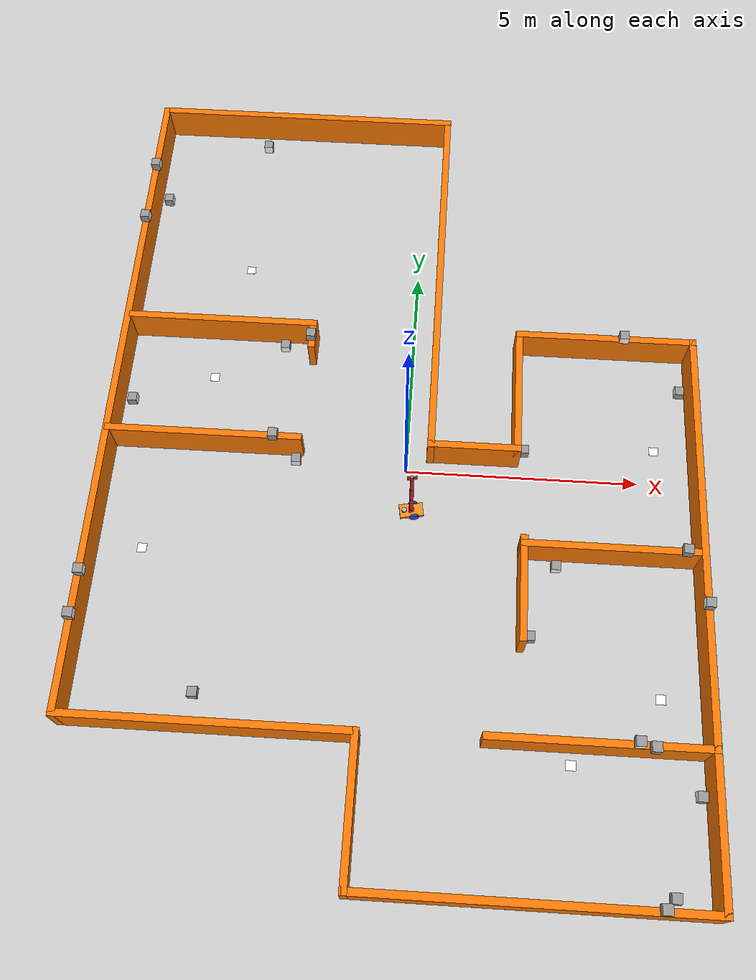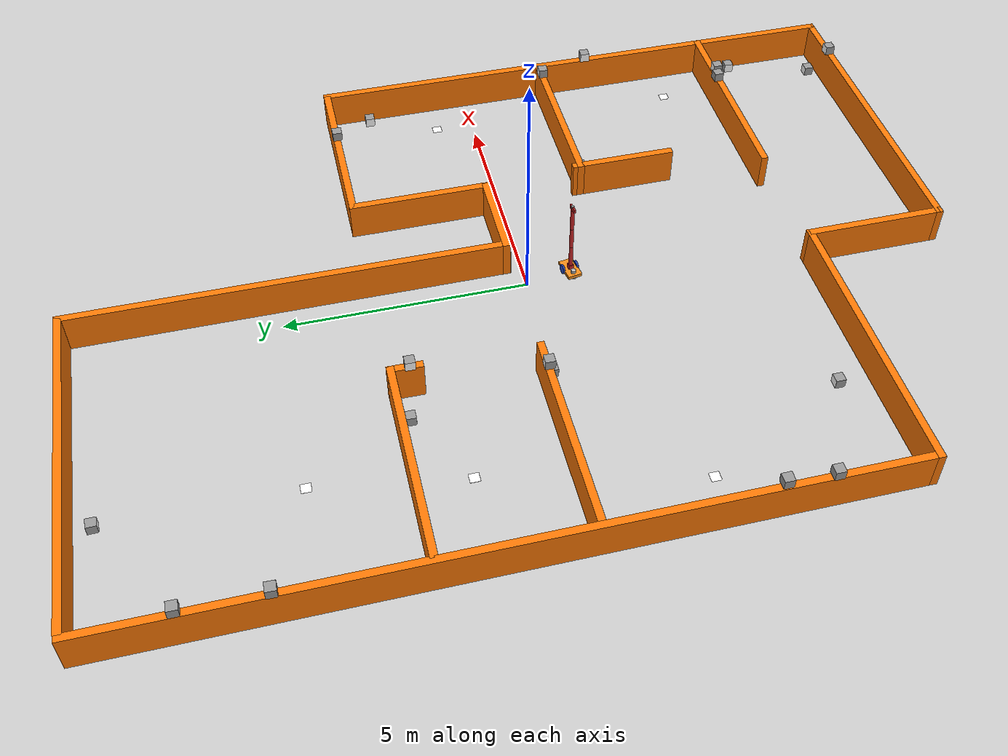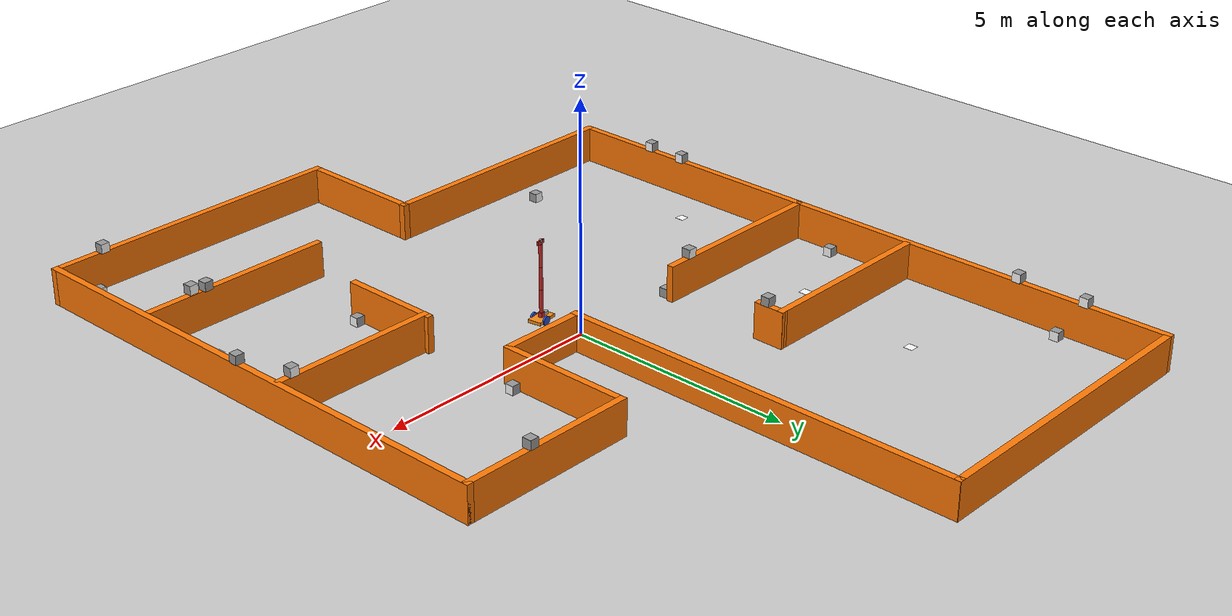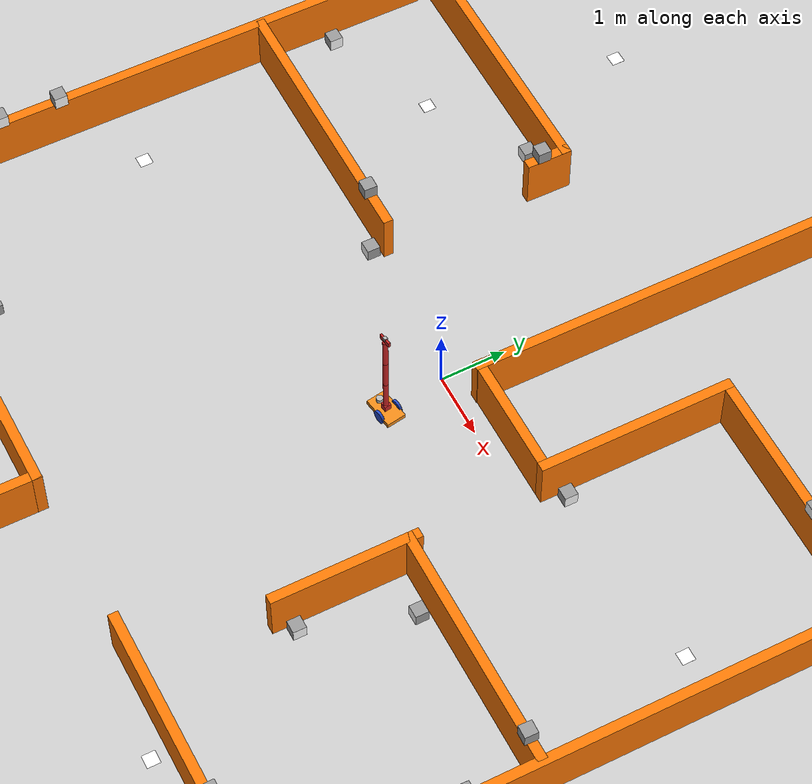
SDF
<sdf version="1.7">
 <world name="default">
  <light name="sun" type="directional">
   <pose>0 0 10 0 -0 0</pose>
   <diffuse>0.8 0.8 0.8 1</diffuse>
   <specular>0.2 0.2 0.2 1</specular>
   <attenuation>
    <range>1000</range>
    <constant>0.9</constant>
    <linear>0.01</linear>
    <quadratic>0.001</quadratic>
   </attenuation>
   <direction>-0.5 0.1 -0.9</direction>
   <spot><inner_angle>0</inner_angle><outer_angle>0</outer_angle><falloff>0</falloff></spot>
  </light>
  <model name="ground_plane">
   <static>1</static>
   <link name="link">
    <collision name="collision">
     <geometry><plane><normal>0 0 1</normal><size>100 100</size></plane></geometry>
     <surface>
      <contact><collide_bitmask>65535</collide_bitmask></contact>
      <friction><ode><mu>100</mu><mu2>50</mu2></ode></friction>
     </surface>
    </collision>
    <visual name="visual">
     <cast_shadows>0</cast_shadows>
     <geometry><plane><normal>0 0 1</normal><size>100 100</size></plane></geometry>
     <material>
      <script><uri>file://media/materials/scripts/gazebo.material</uri><name>Gazebo/Grey</name></script>
     </material>
    </visual>
   </link>
  </model>
  <gravity>0 0 -9.8</gravity>
  <magnetic_field>6e-06 2.3e-05 -4.2e-05</magnetic_field>
  <atmosphere type="adiabatic"/>
  <physics name="default_physics" default="0" type="ode">
   <max_step_size>0.001</max_step_size>
   <real_time_factor>1</real_time_factor>
   <real_time_update_rate>1000</real_time_update_rate>
  </physics>
  <scene><ambient>0.4 0.4 0.4 1</ambient><background>0.7 0.7 0.7 1</background><shadows>1</shadows></scene>
  <spherical_coordinates>
   <surface_model>EARTH_WGS84</surface_model>
   <latitude_deg>0</latitude_deg>
   <longitude_deg>0</longitude_deg>
   <elevation>0</elevation>
   <heading_deg>0</heading_deg>
  </spherical_coordinates>
  <model name="house_1">
   <link name="Wall_43">
    <pose>-2.787 8.425 0 0 -0 0</pose>
    <inertial>
     <mass>1</mass>
     <inertia><ixx>1</ixx><ixy>0</ixy><ixz>0</ixz><iyy>1</iyy><iyz>0</iyz><izz>1</izz></inertia>
    </inertial>
    <visual name="Wall_43_Visual">
     <pose>0 0 0.4 0 -0 0</pose>
     <geometry><box><size>7 0.15 0.8</size></box></geometry>
     <material>
      <script><uri>file://media/materials/scripts/gazebo.material</uri><name>Gazebo/Grey</name></script>
      <ambient>0.996 0.475 0.02 1</ambient>
      <shader type="pixel"><normal_map>__default__</normal_map></shader>
      <diffuse>0.7 0.7 0.7 1</diffuse>
      <specular>0.01 0.01 0.01 1</specular>
      <emissive>0 0 0 1</emissive>
     </material>
     <meta><layer>0</layer></meta>
    </visual>
    <collision name="Wall_43_Collision">
     <pose>0 0 0.4 0 -0 0</pose>
     <geometry><box><size>7 0.15 0.8</size></box></geometry>
     <surface>
      <friction>
       <ode><mu>1</mu><mu2>1</mu2><fdir1>0 0 0</fdir1><slip1>0</slip1><slip2>0</slip2></ode>
       <torsional>
        <coefficient>1</coefficient>
        <patch_radius>0</patch_radius>
        <surface_radius>0</surface_radius>
        <use_patch_radius>1</use_patch_radius>
        <ode><slip>0</slip></ode>
       </torsional>
      </friction>
      <bounce><restitution_coefficient>0</restitution_coefficient><threshold>1e+06</threshold></bounce>
      <contact>
       <collide_without_contact>0</collide_without_contact>
       <collide_without_contact_bitmask>1</collide_without_contact_bitmask>
       <collide_bitmask>1</collide_bitmask>
       <ode>
        <soft_cfm>0</soft_cfm>
        <soft_erp>0.2</soft_erp>
        <kp>1e+13</kp>
        <kd>1</kd>
        <max_vel>0.01</max_vel>
        <min_depth>0</min_depth>
       </ode>
       <bullet>
        <split_impulse>1</split_impulse>
        <split_impulse_penetration_threshold>-0.01</split_impulse_penetration_threshold>
        <soft_cfm>0</soft_cfm>
        <soft_erp>0.2</soft_erp>
        <kp>1e+13</kp>
        <kd>1</kd>
       </bullet>
      </contact>
     </surface>
    </collision>
   </link>
   <link name="Wall_44">
    <pose>0.642 3.99 0 0 0 -1.5708</pose>
    <inertial>
     <mass>1</mass>
     <inertia><ixx>1</ixx><ixy>0</ixy><ixz>0</ixz><iyy>1</iyy><iyz>0</iyz><izz>1</izz></inertia>
    </inertial>
    <visual name="Wall_44_Visual">
     <pose>0 0 0.4 0 -0 0</pose>
     <geometry><box><size>9 0.15 0.8</size></box></geometry>
     <material>
      <script><uri>file://media/materials/scripts/gazebo.material</uri><name>Gazebo/Grey</name></script>
      <ambient>0.996 0.475 0.02 1</ambient>
      <shader type="pixel"><normal_map>__default__</normal_map></shader>
      <diffuse>0.7 0.7 0.7 1</diffuse>
      <specular>0.01 0.01 0.01 1</specular>
      <emissive>0 0 0 1</emissive>
     </material>
     <meta><layer>0</layer></meta>
    </visual>
    <collision name="Wall_44_Collision">
     <pose>0 0 0.4 0 -0 0</pose>
     <geometry><box><size>9 0.15 0.8</size></box></geometry>
     <surface>
      <friction>
       <ode><mu>1</mu><mu2>1</mu2><fdir1>0 0 0</fdir1><slip1>0</slip1><slip2>0</slip2></ode>
       <torsional>
        <coefficient>1</coefficient>
        <patch_radius>0</patch_radius>
        <surface_radius>0</surface_radius>
        <use_patch_radius>1</use_patch_radius>
        <ode><slip>0</slip></ode>
       </torsional>
      </friction>
      <bounce><restitution_coefficient>0</restitution_coefficient><threshold>1e+06</threshold></bounce>
      <contact>
       <collide_without_contact>0</collide_without_contact>
       <collide_without_contact_bitmask>1</collide_without_contact_bitmask>
       <collide_bitmask>1</collide_bitmask>
       <ode>
        <soft_cfm>0</soft_cfm>
        <soft_erp>0.2</soft_erp>
        <kp>1e+13</kp>
        <kd>1</kd>
        <max_vel>0.01</max_vel>
        <min_depth>0</min_depth>
       </ode>
       <bullet>
        <split_impulse>1</split_impulse>
        <split_impulse_penetration_threshold>-0.01</split_impulse_penetration_threshold>
        <soft_cfm>0</soft_cfm>
        <soft_erp>0.2</soft_erp>
        <kp>1e+13</kp>
        <kd>1</kd>
       </bullet>
      </contact>
     </surface>
    </collision>
   </link>
   <link name="Wall_45">
    <pose>1.563 -0.425 0 0 -0 0</pose>
    <inertial>
     <mass>1</mass>
     <inertia><ixx>1</ixx><ixy>0</ixy><ixz>0</ixz><iyy>1</iyy><iyz>0</iyz><izz>1</izz></inertia>
    </inertial>
    <visual name="Wall_45_Visual">
     <pose>0 0 0.4 0 -0 0</pose>
     <geometry><box><size>2 0.15 0.8</size></box></geometry>
     <material>
      <script><uri>file://media/materials/scripts/gazebo.material</uri><name>Gazebo/Grey</name></script>
      <ambient>0.996 0.475 0.02 1</ambient>
      <shader type="pixel"><normal_map>__default__</normal_map></shader>
      <diffuse>0.7 0.7 0.7 1</diffuse>
      <specular>0.01 0.01 0.01 1</specular>
      <emissive>0 0 0 1</emissive>
     </material>
     <meta><layer>0</layer></meta>
    </visual>
    <collision name="Wall_45_Collision">
     <pose>0 0 0.4 0 -0 0</pose>
     <geometry><box><size>2 0.15 0.8</size></box></geometry>
     <surface>
      <friction>
       <ode><mu>1</mu><mu2>1</mu2><fdir1>0 0 0</fdir1><slip1>0</slip1><slip2>0</slip2></ode>
       <torsional>
        <coefficient>1</coefficient>
        <patch_radius>0</patch_radius>
        <surface_radius>0</surface_radius>
        <use_patch_radius>1</use_patch_radius>
        <ode><slip>0</slip></ode>
       </torsional>
      </friction>
      <bounce><restitution_coefficient>0</restitution_coefficient><threshold>1e+06</threshold></bounce>
      <contact>
       <collide_without_contact>0</collide_without_contact>
       <collide_without_contact_bitmask>1</collide_without_contact_bitmask>
       <collide_bitmask>1</collide_bitmask>
       <ode>
        <soft_cfm>0</soft_cfm>
        <soft_erp>0.2</soft_erp>
        <kp>1e+13</kp>
        <kd>1</kd>
        <max_vel>0.01</max_vel>
        <min_depth>0</min_depth>
       </ode>
       <bullet>
        <split_impulse>1</split_impulse>
        <split_impulse_penetration_threshold>-0.01</split_impulse_penetration_threshold>
        <soft_cfm>0</soft_cfm>
        <soft_erp>0.2</soft_erp>
        <kp>1e+13</kp>
        <kd>1</kd>
       </bullet>
      </contact>
     </surface>
    </collision>
   </link>
   <link name="Wall_46">
    <pose>2.488 1 0 0 -0 1.5708</pose>
    <inertial>
     <mass>1</mass>
     <inertia><ixx>1</ixx><ixy>0</ixy><ixz>0</ixz><iyy>1</iyy><iyz>0</iyz><izz>1</izz></inertia>
    </inertial>
    <visual name="Wall_46_Visual">
     <pose>0 0 0.4 0 -0 0</pose>
     <geometry><box><size>3 0.15 0.8</size></box></geometry>
     <material>
      <script><uri>file://media/materials/scripts/gazebo.material</uri><name>Gazebo/Grey</name></script>
      <ambient>0.996 0.475 0.02 1</ambient>
      <shader type="pixel"><normal_map>__default__</normal_map></shader>
      <diffuse>0.7 0.7 0.7 1</diffuse>
      <specular>0.01 0.01 0.01 1</specular>
      <emissive>0 0 0 1</emissive>
     </material>
     <meta><layer>0</layer></meta>
    </visual>
    <collision name="Wall_46_Collision">
     <pose>0 0 0.4 0 -0 0</pose>
     <geometry><box><size>3 0.15 0.8</size></box></geometry>
     <surface>
      <friction>
       <ode><mu>1</mu><mu2>1</mu2><fdir1>0 0 0</fdir1><slip1>0</slip1><slip2>0</slip2></ode>
       <torsional>
        <coefficient>1</coefficient>
        <patch_radius>0</patch_radius>
        <surface_radius>0</surface_radius>
        <use_patch_radius>1</use_patch_radius>
        <ode><slip>0</slip></ode>
       </torsional>
      </friction>
      <bounce><restitution_coefficient>0</restitution_coefficient><threshold>1e+06</threshold></bounce>
      <contact>
       <collide_without_contact>0</collide_without_contact>
       <collide_without_contact_bitmask>1</collide_without_contact_bitmask>
       <collide_bitmask>1</collide_bitmask>
       <ode>
        <soft_cfm>0</soft_cfm>
        <soft_erp>0.2</soft_erp>
        <kp>1e+13</kp>
        <kd>1</kd>
        <max_vel>0.01</max_vel>
        <min_depth>0</min_depth>
       </ode>
       <bullet>
        <split_impulse>1</split_impulse>
        <split_impulse_penetration_threshold>-0.01</split_impulse_penetration_threshold>
        <soft_cfm>0</soft_cfm>
        <soft_erp>0.2</soft_erp>
        <kp>1e+13</kp>
        <kd>1</kd>
       </bullet>
      </contact>
     </surface>
    </collision>
   </link>
   <link name="Wall_47">
    <pose>4.413 2.425 0 0 -0 0</pose>
    <visual name="Wall_47_Visual">
     <pose>0 0 0.4 0 -0 0</pose>
     <geometry><box><size>4 0.15 0.8</size></box></geometry>
     <material>
      <script><uri>file://media/materials/scripts/gazebo.material</uri><name>Gazebo/Grey</name></script>
      <ambient>0.996078 0.47451 0.0196078 1</ambient>
      <shader type="pixel"/>
      <diffuse>0.7 0.7 0.7 1</diffuse>
      <specular>0.01 0.01 0.01 1</specular>
      <emissive>0 0 0 1</emissive>
     </material>
     <meta><layer>0</layer></meta>
    </visual>
    <collision name="Wall_47_Collision">
     <pose>0 0 0.4 0 -0 0</pose>
     <geometry><box><size>4 0.15 0.8</size></box></geometry>
     <surface>
      <friction>
       <ode><mu>1</mu><mu2>1</mu2><fdir1>0 0 0</fdir1><slip1>0</slip1><slip2>0</slip2></ode>
       <torsional>
        <coefficient>1</coefficient>
        <patch_radius>0</patch_radius>
        <surface_radius>0</surface_radius>
        <use_patch_radius>1</use_patch_radius>
        <ode><slip>0</slip></ode>
       </torsional>
      </friction>
      <bounce><restitution_coefficient>0</restitution_coefficient><threshold>1e+06</threshold></bounce>
      <contact>
       <collide_without_contact>0</collide_without_contact>
       <collide_without_contact_bitmask>1</collide_without_contact_bitmask>
       <collide_bitmask>1</collide_bitmask>
       <ode>
        <soft_cfm>0</soft_cfm>
        <soft_erp>0.2</soft_erp>
        <kp>1e+13</kp>
        <kd>1</kd>
        <max_vel>0.01</max_vel>
        <min_depth>0</min_depth>
       </ode>
       <bullet>
        <split_impulse>1</split_impulse>
        <split_impulse_penetration_threshold>-0.01</split_impulse_penetration_threshold>
        <soft_cfm>0</soft_cfm>
        <soft_erp>0.2</soft_erp>
        <kp>1e+13</kp>
        <kd>1</kd>
       </bullet>
      </contact>
     </surface>
    </collision>
   </link>
   <link name="Wall_48">
    <pose>6.338 -3.5 0 0 0 -1.5708</pose>
    <inertial>
     <mass>1</mass>
     <inertia><ixx>1</ixx><ixy>0</ixy><ixz>0</ixz><iyy>1</iyy><iyz>0</iyz><izz>1</izz></inertia>
    </inertial>
    <visual name="Wall_48_Visual">
     <pose>0 0 0.4 0 -0 0</pose>
     <geometry><box><size>12 0.15 0.8</size></box></geometry>
     <material>
      <script><uri>file://media/materials/scripts/gazebo.material</uri><name>Gazebo/Grey</name></script>
      <ambient>0.996 0.475 0.02 1</ambient>
      <shader type="pixel"><normal_map>__default__</normal_map></shader>
      <diffuse>0.7 0.7 0.7 1</diffuse>
      <specular>0.01 0.01 0.01 1</specular>
      <emissive>0 0 0 1</emissive>
     </material>
     <meta><layer>0</layer></meta>
    </visual>
    <collision name="Wall_48_Collision">
     <pose>0 0 0.4 0 -0 0</pose>
     <geometry><box><size>12 0.15 0.8</size></box></geometry>
     <surface>
      <friction>
       <ode><mu>1</mu><mu2>1</mu2><fdir1>0 0 0</fdir1><slip1>0</slip1><slip2>0</slip2></ode>
       <torsional>
        <coefficient>1</coefficient>
        <patch_radius>0</patch_radius>
        <surface_radius>0</surface_radius>
        <use_patch_radius>1</use_patch_radius>
        <ode><slip>0</slip></ode>
       </torsional>
      </friction>
      <bounce><restitution_coefficient>0</restitution_coefficient><threshold>1e+06</threshold></bounce>
      <contact>
       <collide_without_contact>0</collide_without_contact>
       <collide_without_contact_bitmask>1</collide_without_contact_bitmask>
       <collide_bitmask>1</collide_bitmask>
       <ode>
        <soft_cfm>0</soft_cfm>
        <soft_erp>0.2</soft_erp>
        <kp>1e+13</kp>
        <kd>1</kd>
        <max_vel>0.01</max_vel>
        <min_depth>0</min_depth>
       </ode>
       <bullet>
        <split_impulse>1</split_impulse>
        <split_impulse_penetration_threshold>-0.01</split_impulse_penetration_threshold>
        <soft_cfm>0</soft_cfm>
        <soft_erp>0.2</soft_erp>
        <kp>1e+13</kp>
        <kd>1</kd>
       </bullet>
      </contact>
     </surface>
    </collision>
   </link>
   <link name="Wall_49">
    <pose>2.913 -9.425 0 0 -0 3.14159</pose>
    <inertial>
     <mass>1</mass>
     <inertia><ixx>1</ixx><ixy>0</ixy><ixz>0</ixz><iyy>1</iyy><iyz>0</iyz><izz>1</izz></inertia>
    </inertial>
    <visual name="Wall_49_Visual">
     <pose>0 0 0.4 0 -0 0</pose>
     <geometry><box><size>7 0.15 0.8</size></box></geometry>
     <material>
      <script><uri>file://media/materials/scripts/gazebo.material</uri><name>Gazebo/Grey</name></script>
      <ambient>0.996 0.475 0.02 1</ambient>
      <shader type="pixel"><normal_map>__default__</normal_map></shader>
      <diffuse>0.7 0.7 0.7 1</diffuse>
      <specular>0.01 0.01 0.01 1</specular>
      <emissive>0 0 0 1</emissive>
     </material>
     <meta><layer>0</layer></meta>
    </visual>
    <collision name="Wall_49_Collision">
     <pose>0 0 0.4 0 -0 0</pose>
     <geometry><box><size>7 0.15 0.8</size></box></geometry>
     <surface>
      <friction>
       <ode><mu>1</mu><mu2>1</mu2><fdir1>0 0 0</fdir1><slip1>0</slip1><slip2>0</slip2></ode>
       <torsional>
        <coefficient>1</coefficient>
        <patch_radius>0</patch_radius>
        <surface_radius>0</surface_radius>
        <use_patch_radius>1</use_patch_radius>
        <ode><slip>0</slip></ode>
       </torsional>
      </friction>
      <bounce><restitution_coefficient>0</restitution_coefficient><threshold>1e+06</threshold></bounce>
      <contact>
       <collide_without_contact>0</collide_without_contact>
       <collide_without_contact_bitmask>1</collide_without_contact_bitmask>
       <collide_bitmask>1</collide_bitmask>
       <ode>
        <soft_cfm>0</soft_cfm>
        <soft_erp>0.2</soft_erp>
        <kp>1e+13</kp>
        <kd>1</kd>
        <max_vel>0.01</max_vel>
        <min_depth>0</min_depth>
       </ode>
       <bullet>
        <split_impulse>1</split_impulse>
        <split_impulse_penetration_threshold>-0.01</split_impulse_penetration_threshold>
        <soft_cfm>0</soft_cfm>
        <soft_erp>0.2</soft_erp>
        <kp>1e+13</kp>
        <kd>1</kd>
       </bullet>
      </contact>
     </surface>
    </collision>
   </link>
   <link name="Wall_50">
    <pose>-0.512 -8 0 0 -0 1.5708</pose>
    <inertial>
     <mass>1</mass>
     <inertia><ixx>1</ixx><ixy>0</ixy><ixz>0</ixz><iyy>1</iyy><iyz>0</iyz><izz>1</izz></inertia>
    </inertial>
    <visual name="Wall_50_Visual">
     <pose>0 0 0.4 0 -0 0</pose>
     <geometry><box><size>3 0.15 0.8</size></box></geometry>
     <material>
      <script><uri>file://media/materials/scripts/gazebo.material</uri><name>Gazebo/Grey</name></script>
      <ambient>0.996 0.475 0.02 1</ambient>
      <shader type="pixel"><normal_map>__default__</normal_map></shader>
      <diffuse>0.7 0.7 0.7 1</diffuse>
      <specular>0.01 0.01 0.01 1</specular>
      <emissive>0 0 0 1</emissive>
     </material>
     <meta><layer>0</layer></meta>
    </visual>
    <collision name="Wall_50_Collision">
     <pose>0 0 0.4 0 -0 0</pose>
     <geometry><box><size>3 0.15 0.8</size></box></geometry>
     <surface>
      <friction>
       <ode><mu>1</mu><mu2>1</mu2><fdir1>0 0 0</fdir1><slip1>0</slip1><slip2>0</slip2></ode>
       <torsional>
        <coefficient>1</coefficient>
        <patch_radius>0</patch_radius>
        <surface_radius>0</surface_radius>
        <use_patch_radius>1</use_patch_radius>
        <ode><slip>0</slip></ode>
       </torsional>
      </friction>
      <bounce><restitution_coefficient>0</restitution_coefficient><threshold>1e+06</threshold></bounce>
      <contact>
       <collide_without_contact>0</collide_without_contact>
       <collide_without_contact_bitmask>1</collide_without_contact_bitmask>
       <collide_bitmask>1</collide_bitmask>
       <ode>
        <soft_cfm>0</soft_cfm>
        <soft_erp>0.2</soft_erp>
        <kp>1e+13</kp>
        <kd>1</kd>
        <max_vel>0.01</max_vel>
        <min_depth>0</min_depth>
       </ode>
       <bullet>
        <split_impulse>1</split_impulse>
        <split_impulse_penetration_threshold>-0.01</split_impulse_penetration_threshold>
        <soft_cfm>0</soft_cfm>
        <soft_erp>0.2</soft_erp>
        <kp>1e+13</kp>
        <kd>1</kd>
       </bullet>
      </contact>
     </surface>
    </collision>
   </link>
   <link name="Wall_51">
    <pose>-3.425 -6.575 0 0 -0 3.14159</pose>
    <visual name="Wall_51_Visual">
     <pose>0 0 0.4 0 -0 0</pose>
     <geometry><box><size>5.976 0.15 0.8</size></box></geometry>
     <material>
      <script><uri>file://media/materials/scripts/gazebo.material</uri><name>Gazebo/Grey</name></script>
      <ambient>0.996078 0.47451 0.0196078 1</ambient>
      <shader type="pixel"/>
      <diffuse>0.7 0.7 0.7 1</diffuse>
      <specular>0.01 0.01 0.01 1</specular>
      <emissive>0 0 0 1</emissive>
     </material>
     <meta><layer>0</layer></meta>
    </visual>
    <collision name="Wall_51_Collision">
     <pose>0 0 0.4 0 -0 0</pose>
     <geometry><box><size>5.976 0.15 0.8</size></box></geometry>
     <surface>
      <friction>
       <ode><mu>1</mu><mu2>1</mu2><fdir1>0 0 0</fdir1><slip1>0</slip1><slip2>0</slip2></ode>
       <torsional>
        <coefficient>1</coefficient>
        <patch_radius>0</patch_radius>
        <surface_radius>0</surface_radius>
        <use_patch_radius>1</use_patch_radius>
        <ode><slip>0</slip></ode>
       </torsional>
      </friction>
      <bounce><restitution_coefficient>0</restitution_coefficient><threshold>1e+06</threshold></bounce>
      <contact>
       <collide_without_contact>0</collide_without_contact>
       <collide_without_contact_bitmask>1</collide_without_contact_bitmask>
       <collide_bitmask>1</collide_bitmask>
       <ode>
        <soft_cfm>0</soft_cfm>
        <soft_erp>0.2</soft_erp>
        <kp>1e+13</kp>
        <kd>1</kd>
        <max_vel>0.01</max_vel>
        <min_depth>0</min_depth>
       </ode>
       <bullet>
        <split_impulse>1</split_impulse>
        <split_impulse_penetration_threshold>-0.01</split_impulse_penetration_threshold>
        <soft_cfm>0</soft_cfm>
        <soft_erp>0.2</soft_erp>
        <kp>1e+13</kp>
        <kd>1</kd>
       </bullet>
      </contact>
     </surface>
    </collision>
   </link>
   <link name="Wall_52">
    <pose>-6.338 0.9215 0 0 -0 1.5708</pose>
    <visual name="Wall_52_Visual">
     <pose>0 0 0.4 0 -0 0</pose>
     <geometry><box><size>15.1433 0.15 0.8</size></box></geometry>
     <material>
      <script><uri>file://media/materials/scripts/gazebo.material</uri><name>Gazebo/Grey</name></script>
      <ambient>0.996078 0.47451 0.0196078 1</ambient>
      <shader type="pixel"/>
      <diffuse>0.7 0.7 0.7 1</diffuse>
      <specular>0.01 0.01 0.01 1</specular>
      <emissive>0 0 0 1</emissive>
     </material>
     <meta><layer>0</layer></meta>
    </visual>
    <collision name="Wall_52_Collision">
     <pose>0 0 0.4 0 -0 0</pose>
     <geometry><box><size>15.1433 0.15 0.8</size></box></geometry>
     <surface>
      <friction>
       <ode><mu>1</mu><mu2>1</mu2><fdir1>0 0 0</fdir1><slip1>0</slip1><slip2>0</slip2></ode>
       <torsional>
        <coefficient>1</coefficient>
        <patch_radius>0</patch_radius>
        <surface_radius>0</surface_radius>
        <use_patch_radius>1</use_patch_radius>
        <ode><slip>0</slip></ode>
       </torsional>
      </friction>
      <bounce><restitution_coefficient>0</restitution_coefficient><threshold>1e+06</threshold></bounce>
      <contact>
       <collide_without_contact>0</collide_without_contact>
       <collide_without_contact_bitmask>1</collide_without_contact_bitmask>
       <collide_bitmask>1</collide_bitmask>
       <ode>
        <soft_cfm>0</soft_cfm>
        <soft_erp>0.2</soft_erp>
        <kp>1e+13</kp>
        <kd>1</kd>
        <max_vel>0.01</max_vel>
        <min_depth>0</min_depth>
       </ode>
       <bullet>
        <split_impulse>1</split_impulse>
        <split_impulse_penetration_threshold>-0.01</split_impulse_penetration_threshold>
        <soft_cfm>0</soft_cfm>
        <soft_erp>0.2</soft_erp>
        <kp>1e+13</kp>
        <kd>1</kd>
       </bullet>
      </contact>
     </surface>
    </collision>
   </link>
   <link name="Wall_54">
    <pose>-4.182 2.435 0 0 -0 0</pose>
    <visual name="Wall_54_Visual">
     <pose>0 0 0.4 0 -0 0</pose>
     <geometry><box><size>4.25 0.15 0.8</size></box></geometry>
     <material>
      <script><uri>file://media/materials/scripts/gazebo.material</uri><name>Gazebo/Grey</name></script>
      <ambient>0.996078 0.47451 0.0196078 1</ambient>
      <shader type="pixel"/>
      <diffuse>0.7 0.7 0.7 1</diffuse>
      <specular>0.01 0.01 0.01 1</specular>
      <emissive>0 0 0 1</emissive>
     </material>
     <meta><layer>0</layer></meta>
    </visual>
    <collision name="Wall_54_Collision">
     <pose>0 0 0.4 0 -0 0</pose>
     <geometry><box><size>4.25 0.15 0.8</size></box></geometry>
     <surface>
      <friction>
       <ode><mu>1</mu><mu2>1</mu2><fdir1>0 0 0</fdir1><slip1>0</slip1><slip2>0</slip2></ode>
       <torsional>
        <coefficient>1</coefficient>
        <patch_radius>0</patch_radius>
        <surface_radius>0</surface_radius>
        <use_patch_radius>1</use_patch_radius>
        <ode><slip>0</slip></ode>
       </torsional>
      </friction>
      <bounce><restitution_coefficient>0</restitution_coefficient><threshold>1e+06</threshold></bounce>
      <contact>
       <collide_without_contact>0</collide_without_contact>
       <collide_without_contact_bitmask>1</collide_without_contact_bitmask>
       <collide_bitmask>1</collide_bitmask>
       <ode>
        <soft_cfm>0</soft_cfm>
        <soft_erp>0.2</soft_erp>
        <kp>1e+13</kp>
        <kd>1</kd>
        <max_vel>0.01</max_vel>
        <min_depth>0</min_depth>
       </ode>
       <bullet>
        <split_impulse>1</split_impulse>
        <split_impulse_penetration_threshold>-0.01</split_impulse_penetration_threshold>
        <soft_cfm>0</soft_cfm>
        <soft_erp>0.2</soft_erp>
        <kp>1e+13</kp>
        <kd>1</kd>
       </bullet>
      </contact>
     </surface>
    </collision>
   </link>
   <link name="Wall_56">
    <pose>-4.252 -0.433 0 0 -0 0</pose>
    <visual name="Wall_56_Visual">
     <pose>0 0 0.4 0 -0 0</pose>
     <geometry><box><size>4.25 0.15 0.8</size></box></geometry>
     <material>
      <script><uri>file://media/materials/scripts/gazebo.material</uri><name>Gazebo/Grey</name></script>
      <ambient>0.996078 0.47451 0.0196078 1</ambient>
      <shader type="pixel"/>
      <diffuse>0.7 0.7 0.7 1</diffuse>
      <specular>0.01 0.01 0.01 1</specular>
      <emissive>0 0 0 1</emissive>
     </material>
     <meta><layer>0</layer></meta>
    </visual>
    <collision name="Wall_56_Collision">
     <pose>0 0 0.4 0 -0 0</pose>
     <geometry><box><size>4.25 0.15 0.8</size></box></geometry>
     <surface>
      <friction>
       <ode><mu>1</mu><mu2>1</mu2><fdir1>0 0 0</fdir1><slip1>0</slip1><slip2>0</slip2></ode>
       <torsional>
        <coefficient>1</coefficient>
        <patch_radius>0</patch_radius>
        <surface_radius>0</surface_radius>
        <use_patch_radius>1</use_patch_radius>
        <ode><slip>0</slip></ode>
       </torsional>
      </friction>
      <bounce><restitution_coefficient>0</restitution_coefficient><threshold>1e+06</threshold></bounce>
      <contact>
       <collide_without_contact>0</collide_without_contact>
       <collide_without_contact_bitmask>1</collide_without_contact_bitmask>
       <collide_bitmask>1</collide_bitmask>
       <ode>
        <soft_cfm>0</soft_cfm>
        <soft_erp>0.2</soft_erp>
        <kp>1e+13</kp>
        <kd>1</kd>
        <max_vel>0.01</max_vel>
        <min_depth>0</min_depth>
       </ode>
       <bullet>
        <split_impulse>1</split_impulse>
        <split_impulse_penetration_threshold>-0.01</split_impulse_penetration_threshold>
        <soft_cfm>0</soft_cfm>
        <soft_erp>0.2</soft_erp>
        <kp>1e+13</kp>
        <kd>1</kd>
       </bullet>
      </contact>
     </surface>
    </collision>
   </link>
   <link name="Wall_58">
    <pose>-2.132 2.16 0 0 0 -1.5808</pose>
    <inertial>
     <mass>1</mass>
     <inertia><ixx>1</ixx><ixy>0</ixy><ixz>0</ixz><iyy>1</iyy><iyz>0</iyz><izz>1</izz></inertia>
    </inertial>
    <visual name="Wall_58_Visual">
     <pose>0 0 0.4 0 -0 0</pose>
     <geometry><box><size>0.7 0.15 0.8</size></box></geometry>
     <material>
      <script><uri>file://media/materials/scripts/gazebo.material</uri><name>Gazebo/Grey</name></script>
      <ambient>0.996 0.475 0.02 1</ambient>
      <shader type="pixel"><normal_map>__default__</normal_map></shader>
      <diffuse>0.7 0.7 0.7 1</diffuse>
      <specular>0.01 0.01 0.01 1</specular>
      <emissive>0 0 0 1</emissive>
     </material>
     <meta><layer>0</layer></meta>
    </visual>
    <collision name="Wall_58_Collision">
     <pose>0 0 0.4 0 -0 0</pose>
     <geometry><box><size>0.7 0.15 0.8</size></box></geometry>
     <surface>
      <friction>
       <ode><mu>1</mu><mu2>1</mu2><fdir1>0 0 0</fdir1><slip1>0</slip1><slip2>0</slip2></ode>
       <torsional>
        <coefficient>1</coefficient>
        <patch_radius>0</patch_radius>
        <surface_radius>0</surface_radius>
        <use_patch_radius>1</use_patch_radius>
        <ode><slip>0</slip></ode>
       </torsional>
      </friction>
      <bounce><restitution_coefficient>0</restitution_coefficient><threshold>1e+06</threshold></bounce>
      <contact>
       <collide_without_contact>0</collide_without_contact>
       <collide_without_contact_bitmask>1</collide_without_contact_bitmask>
       <collide_bitmask>1</collide_bitmask>
       <ode>
        <soft_cfm>0</soft_cfm>
        <soft_erp>0.2</soft_erp>
        <kp>1e+13</kp>
        <kd>1</kd>
        <max_vel>0.01</max_vel>
        <min_depth>0</min_depth>
       </ode>
       <bullet>
        <split_impulse>1</split_impulse>
        <split_impulse_penetration_threshold>-0.01</split_impulse_penetration_threshold>
        <soft_cfm>0</soft_cfm>
        <soft_erp>0.2</soft_erp>
        <kp>1e+13</kp>
        <kd>1</kd>
       </bullet>
      </contact>
     </surface>
    </collision>
   </link>
   <link name="Wall_60">
    <pose>4.454 -2.562 0 0 -0 3.14159</pose>
    <inertial>
     <mass>1</mass>
     <inertia><ixx>1</ixx><ixy>0</ixy><ixz>0</ixz><iyy>1</iyy><iyz>0</iyz><izz>1</izz></inertia>
    </inertial>
    <visual name="Wall_60_Visual">
     <pose>0 0 0.4 0 -0 0</pose>
     <geometry><box><size>3.75 0.15 0.8</size></box></geometry>
     <material>
      <script><uri>file://media/materials/scripts/gazebo.material</uri><name>Gazebo/Grey</name></script>
      <ambient>0.996 0.475 0.02 1</ambient>
      <shader type="pixel"><normal_map>__default__</normal_map></shader>
      <diffuse>0.7 0.7 0.7 1</diffuse>
      <specular>0.01 0.01 0.01 1</specular>
      <emissive>0 0 0 1</emissive>
     </material>
     <meta><layer>0</layer></meta>
    </visual>
    <collision name="Wall_60_Collision">
     <pose>0 0 0.4 0 -0 0</pose>
     <geometry><box><size>3.75 0.15 0.8</size></box></geometry>
     <surface>
      <friction>
       <ode><mu>1</mu><mu2>1</mu2><fdir1>0 0 0</fdir1><slip1>0</slip1><slip2>0</slip2></ode>
       <torsional>
        <coefficient>1</coefficient>
        <patch_radius>0</patch_radius>
        <surface_radius>0</surface_radius>
        <use_patch_radius>1</use_patch_radius>
        <ode><slip>0</slip></ode>
       </torsional>
      </friction>
      <bounce><restitution_coefficient>0</restitution_coefficient><threshold>1e+06</threshold></bounce>
      <contact>
       <collide_without_contact>0</collide_without_contact>
       <collide_without_contact_bitmask>1</collide_without_contact_bitmask>
       <collide_bitmask>1</collide_bitmask>
       <ode>
        <soft_cfm>0</soft_cfm>
        <soft_erp>0.2</soft_erp>
        <kp>1e+13</kp>
        <kd>1</kd>
        <max_vel>0.01</max_vel>
        <min_depth>0</min_depth>
       </ode>
       <bullet>
        <split_impulse>1</split_impulse>
        <split_impulse_penetration_threshold>-0.01</split_impulse_penetration_threshold>
        <soft_cfm>0</soft_cfm>
        <soft_erp>0.2</soft_erp>
        <kp>1e+13</kp>
        <kd>1</kd>
       </bullet>
      </contact>
     </surface>
    </collision>
   </link>
   <link name="Wall_61">
    <pose>2.654 -3.512 0 0 0 -1.5708</pose>
    <inertial>
     <mass>1</mass>
     <inertia><ixx>1</ixx><ixy>0</ixy><ixz>0</ixz><iyy>1</iyy><iyz>0</iyz><izz>1</izz></inertia>
    </inertial>
    <visual name="Wall_61_Visual">
     <pose>0 0 0.4 0 -0 0</pose>
     <geometry><box><size>2.25 0.15 0.8</size></box></geometry>
     <material>
      <script><uri>file://media/materials/scripts/gazebo.material</uri><name>Gazebo/Grey</name></script>
      <ambient>0.996 0.475 0.02 1</ambient>
      <shader type="pixel"><normal_map>__default__</normal_map></shader>
      <diffuse>0.7 0.7 0.7 1</diffuse>
      <specular>0.01 0.01 0.01 1</specular>
      <emissive>0 0 0 1</emissive>
     </material>
     <meta><layer>0</layer></meta>
    </visual>
    <collision name="Wall_61_Collision">
     <pose>0 0 0.4 0 -0 0</pose>
     <geometry><box><size>2.25 0.15 0.8</size></box></geometry>
     <surface>
      <friction>
       <ode><mu>1</mu><mu2>1</mu2><fdir1>0 0 0</fdir1><slip1>0</slip1><slip2>0</slip2></ode>
       <torsional>
        <coefficient>1</coefficient>
        <patch_radius>0</patch_radius>
        <surface_radius>0</surface_radius>
        <use_patch_radius>1</use_patch_radius>
        <ode><slip>0</slip></ode>
       </torsional>
      </friction>
      <bounce><restitution_coefficient>0</restitution_coefficient><threshold>1e+06</threshold></bounce>
      <contact>
       <collide_without_contact>0</collide_without_contact>
       <collide_without_contact_bitmask>1</collide_without_contact_bitmask>
       <collide_bitmask>1</collide_bitmask>
       <ode>
        <soft_cfm>0</soft_cfm>
        <soft_erp>0.2</soft_erp>
        <kp>1e+13</kp>
        <kd>1</kd>
        <max_vel>0.01</max_vel>
        <min_depth>0</min_depth>
       </ode>
       <bullet>
        <split_impulse>1</split_impulse>
        <split_impulse_penetration_threshold>-0.01</split_impulse_penetration_threshold>
        <soft_cfm>0</soft_cfm>
        <soft_erp>0.2</soft_erp>
        <kp>1e+13</kp>
        <kd>1</kd>
       </bullet>
      </contact>
     </surface>
    </collision>
   </link>
   <link name="Wall_63">
    <pose>4.157 -6.517 0 0 -0 0</pose>
    <inertial>
     <mass>1</mass>
     <inertia><ixx>1</ixx><ixy>0</ixy><ixz>0</ixz><iyy>1</iyy><iyz>0</iyz><izz>1</izz></inertia>
    </inertial>
    <visual name="Wall_63_Visual">
     <pose>0 0 0.4 0 -0 0</pose>
     <geometry><box><size>4.5 0.15 0.8</size></box></geometry>
     <material>
      <script><uri>file://media/materials/scripts/gazebo.material</uri><name>Gazebo/Grey</name></script>
      <ambient>0.996 0.475 0.02 1</ambient>
      <shader type="pixel"><normal_map>__default__</normal_map></shader>
      <diffuse>0.7 0.7 0.7 1</diffuse>
      <specular>0.01 0.01 0.01 1</specular>
      <emissive>0 0 0 1</emissive>
     </material>
     <meta><layer>0</layer></meta>
    </visual>
    <collision name="Wall_63_Collision">
     <pose>0 0 0.4 0 -0 0</pose>
     <geometry><box><size>4.5 0.15 0.8</size></box></geometry>
     <surface>
      <friction>
       <ode><mu>1</mu><mu2>1</mu2><fdir1>0 0 0</fdir1><slip1>0</slip1><slip2>0</slip2></ode>
       <torsional>
        <coefficient>1</coefficient>
        <patch_radius>0</patch_radius>
        <surface_radius>0</surface_radius>
        <use_patch_radius>1</use_patch_radius>
        <ode><slip>0</slip></ode>
       </torsional>
      </friction>
      <bounce><restitution_coefficient>0</restitution_coefficient><threshold>1e+06</threshold></bounce>
      <contact>
       <collide_without_contact>0</collide_without_contact>
       <collide_without_contact_bitmask>1</collide_without_contact_bitmask>
       <collide_bitmask>1</collide_bitmask>
       <ode>
        <soft_cfm>0</soft_cfm>
        <soft_erp>0.2</soft_erp>
        <kp>1e+13</kp>
        <kd>1</kd>
        <max_vel>0.01</max_vel>
        <min_depth>0</min_depth>
       </ode>
       <bullet>
        <split_impulse>1</split_impulse>
        <split_impulse_penetration_threshold>-0.01</split_impulse_penetration_threshold>
        <soft_cfm>0</soft_cfm>
        <soft_erp>0.2</soft_erp>
        <kp>1e+13</kp>
        <kd>1</kd>
       </bullet>
      </contact>
     </surface>
    </collision>
   </link>
   <static>1</static>
   <pose>-0.14491 0.76464 0 0 -0 0</pose>
  </model>
  <model name="marker11_box">
   <link name="marker">
    <inertial>
     <mass>0.1</mass>
     <inertia><ixx>0</ixx><ixy>0</ixy><ixz>0</ixz><iyy>0</iyy><iyz>0</iyz><izz>0</izz></inertia>
    </inertial>
    <self_collide>1</self_collide>
    <pose>-0.76428 -0.101106 0.120004 -0.015494 1.56996 -0.015507</pose>
    <visual name="visual">
     <geometry><box><size>0.2 0.2 0.001</size></box></geometry>
     <material>
      <script>
       <uri>model://marker11/material/scripts</uri>
       <uri>model://marker11/material/textures</uri>
       <name>Aruco/marker11</name>
      </script>
      <shader type="pixel"><normal_map>__default__</normal_map></shader>
      <emissive>0 0 0 1</emissive>
      <ambient>1 1 1 1</ambient>
      <diffuse>1 1 1 1</diffuse>
      <specular>0 0 0 1</specular>
     </material>
    </visual>
    <collision name="collision">
     <geometry><box><size>0.2 0.2 0.02</size></box></geometry>
     <surface>
      <friction>
       <ode><mu>1</mu><mu2>1</mu2><fdir1>0 0 0</fdir1><slip1>0</slip1><slip2>0</slip2></ode>
       <torsional>
        <coefficient>1</coefficient>
        <patch_radius>0</patch_radius>
        <surface_radius>0</surface_radius>
        <use_patch_radius>1</use_patch_radius>
        <ode><slip>0</slip></ode>
       </torsional>
      </friction>
      <bounce><restitution_coefficient>0</restitution_coefficient><threshold>1e+06</threshold></bounce>
      <contact>
       <collide_without_contact>0</collide_without_contact>
       <collide_without_contact_bitmask>1</collide_without_contact_bitmask>
       <collide_bitmask>1</collide_bitmask>
       <ode>
        <soft_cfm>0</soft_cfm>
        <soft_erp>0.2</soft_erp>
        <kp>1e+13</kp>
        <kd>1</kd>
        <max_vel>0.01</max_vel>
        <min_depth>0</min_depth>
       </ode>
       <bullet>
        <split_impulse>1</split_impulse>
        <split_impulse_penetration_threshold>-0.01</split_impulse_penetration_threshold>
        <soft_cfm>0</soft_cfm>
        <soft_erp>0.2</soft_erp>
        <kp>1e+13</kp>
        <kd>1</kd>
       </bullet>
      </contact>
     </surface>
    </collision>
   </link>
   <link name="link_1">
    <inertial>
     <mass>1</mass>
     <inertia>
      <ixx>0.166667</ixx>
      <ixy>0</ixy>
      <ixz>0</ixz>
      <iyy>0.166667</iyy>
      <iyz>0</iyz>
      <izz>0.166667</izz>
     </inertia>
    </inertial>
    <pose>-0.86428 -0.101106 0.12 -1.3e-05 -4.2e-05 0</pose>
    <visual name="visual">
     <geometry><box><size>0.2 0.2 0.2</size></box></geometry>
     <material>
      <lighting>1</lighting>
      <script><uri>file://media/materials/scripts/gazebo.material</uri><name>Gazebo/Grey</name></script>
      <shader type="pixel"><normal_map>__default__</normal_map></shader>
      <emissive>0 0 0 1</emissive>
      <ambient>0.3 0.3 0.3 1</ambient>
      <diffuse>0.7 0.7 0.7 1</diffuse>
      <specular>0.01 0.01 0.01 1</specular>
     </material>
    </visual>
    <collision name="collision">
     <geometry><box><size>0.2 0.2 0.2</size></box></geometry>
     <surface>
      <friction>
       <ode><mu>1</mu><mu2>1</mu2><fdir1>0 0 0</fdir1><slip1>0</slip1><slip2>0</slip2></ode>
       <torsional>
        <coefficient>1</coefficient>
        <patch_radius>0</patch_radius>
        <surface_radius>0</surface_radius>
        <use_patch_radius>1</use_patch_radius>
        <ode><slip>0</slip></ode>
       </torsional>
      </friction>
      <bounce><restitution_coefficient>0</restitution_coefficient><threshold>1e+06</threshold></bounce>
      <contact>
       <collide_without_contact>0</collide_without_contact>
       <collide_without_contact_bitmask>1</collide_without_contact_bitmask>
       <collide_bitmask>1</collide_bitmask>
       <ode>
        <soft_cfm>0</soft_cfm>
        <soft_erp>0.2</soft_erp>
        <kp>1e+13</kp>
        <kd>1</kd>
        <max_vel>0.01</max_vel>
        <min_depth>0</min_depth>
       </ode>
       <bullet>
        <split_impulse>1</split_impulse>
        <split_impulse_penetration_threshold>-0.01</split_impulse_penetration_threshold>
        <soft_cfm>0</soft_cfm>
        <soft_erp>0.2</soft_erp>
        <kp>1e+13</kp>
        <kd>1</kd>
       </bullet>
      </contact>
     </surface>
    </collision>
   </link>
   <joint name="link_1_JOINT_3" type="fixed">
    <parent>link_1</parent>
    <child>marker</child>
    <physics>
     <ode><limit><cfm>0</cfm><erp>0.2</erp></limit><suspension><cfm>0</cfm><erp>0.2</erp></suspension></ode>
    </physics>
   </joint>
   <static>0</static>
   <pose>-5.35349 7.06652 -0.020008 1.4e-05 1.8e-05 0.000725</pose>
  </model>
  <model name="marker12_box">
   <link name="marker">
    <inertial>
     <mass>0.1</mass>
     <inertia><ixx>0</ixx><ixy>0</ixy><ixz>0</ixz><iyy>0</iyy><iyz>0</iyz><izz>0</izz></inertia>
    </inertial>
    <self_collide>1</self_collide>
    <pose>-0.76428 -0.101106 0.120004 -0.015494 1.56996 -0.015507</pose>
    <visual name="visual">
     <geometry><box><size>0.2 0.2 0.001</size></box></geometry>
     <material>
      <script>
       <uri>model://marker12/material/scripts</uri>
       <uri>model://marker12/material/textures</uri>
       <name>Aruco/marker12</name>
      </script>
      <shader type="pixel"><normal_map>__default__</normal_map></shader>
      <emissive>0 0 0 1</emissive>
      <ambient>1 1 1 1</ambient>
      <diffuse>1 1 1 1</diffuse>
      <specular>0 0 0 1</specular>
     </material>
    </visual>
    <collision name="collision">
     <geometry><box><size>0.2 0.2 0.02</size></box></geometry>
     <surface>
      <friction>
       <ode><mu>1</mu><mu2>1</mu2><fdir1>0 0 0</fdir1><slip1>0</slip1><slip2>0</slip2></ode>
       <torsional>
        <coefficient>1</coefficient>
        <patch_radius>0</patch_radius>
        <surface_radius>0</surface_radius>
        <use_patch_radius>1</use_patch_radius>
        <ode><slip>0</slip></ode>
       </torsional>
      </friction>
      <bounce><restitution_coefficient>0</restitution_coefficient><threshold>1e+06</threshold></bounce>
      <contact>
       <collide_without_contact>0</collide_without_contact>
       <collide_without_contact_bitmask>1</collide_without_contact_bitmask>
       <collide_bitmask>1</collide_bitmask>
       <ode>
        <soft_cfm>0</soft_cfm>
        <soft_erp>0.2</soft_erp>
        <kp>1e+13</kp>
        <kd>1</kd>
        <max_vel>0.01</max_vel>
        <min_depth>0</min_depth>
       </ode>
       <bullet>
        <split_impulse>1</split_impulse>
        <split_impulse_penetration_threshold>-0.01</split_impulse_penetration_threshold>
        <soft_cfm>0</soft_cfm>
        <soft_erp>0.2</soft_erp>
        <kp>1e+13</kp>
        <kd>1</kd>
       </bullet>
      </contact>
     </surface>
    </collision>
   </link>
   <link name="link_1">
    <inertial>
     <mass>1</mass>
     <inertia>
      <ixx>0.166667</ixx>
      <ixy>0</ixy>
      <ixz>0</ixz>
      <iyy>0.166667</iyy>
      <iyz>0</iyz>
      <izz>0.166667</izz>
     </inertia>
    </inertial>
    <pose>-0.86428 -0.101106 0.12 -1.3e-05 -4.2e-05 0</pose>
    <visual name="visual">
     <geometry><box><size>0.2 0.2 0.2</size></box></geometry>
     <material>
      <lighting>1</lighting>
      <script><uri>file://media/materials/scripts/gazebo.material</uri><name>Gazebo/Grey</name></script>
      <shader type="pixel"><normal_map>__default__</normal_map></shader>
      <emissive>0 0 0 1</emissive>
      <ambient>0.3 0.3 0.3 1</ambient>
      <diffuse>0.7 0.7 0.7 1</diffuse>
      <specular>0.01 0.01 0.01 1</specular>
     </material>
    </visual>
    <collision name="collision">
     <geometry><box><size>0.2 0.2 0.2</size></box></geometry>
     <surface>
      <friction>
       <ode><mu>1</mu><mu2>1</mu2><fdir1>0 0 0</fdir1><slip1>0</slip1><slip2>0</slip2></ode>
       <torsional>
        <coefficient>1</coefficient>
        <patch_radius>0</patch_radius>
        <surface_radius>0</surface_radius>
        <use_patch_radius>1</use_patch_radius>
        <ode><slip>0</slip></ode>
       </torsional>
      </friction>
      <bounce><restitution_coefficient>0</restitution_coefficient><threshold>1e+06</threshold></bounce>
      <contact>
       <collide_without_contact>0</collide_without_contact>
       <collide_without_contact_bitmask>1</collide_without_contact_bitmask>
       <collide_bitmask>1</collide_bitmask>
       <ode>
        <soft_cfm>0</soft_cfm>
        <soft_erp>0.2</soft_erp>
        <kp>1e+13</kp>
        <kd>1</kd>
        <max_vel>0.01</max_vel>
        <min_depth>0</min_depth>
       </ode>
       <bullet>
        <split_impulse>1</split_impulse>
        <split_impulse_penetration_threshold>-0.01</split_impulse_penetration_threshold>
        <soft_cfm>0</soft_cfm>
        <soft_erp>0.2</soft_erp>
        <kp>1e+13</kp>
        <kd>1</kd>
       </bullet>
      </contact>
     </surface>
    </collision>
   </link>
   <joint name="link_1_JOINT_3" type="fixed">
    <parent>link_1</parent>
    <child>marker</child>
    <physics>
     <ode><limit><cfm>0</cfm><erp>0.2</erp></limit><suspension><cfm>0</cfm><erp>0.2</erp></suspension></ode>
    </physics>
   </joint>
   <static>0</static>
   <pose>-2.96195 1.18147 0.779998 1.3e-05 1e-05 1.55037</pose>
  </model>
  <model name="marker13_box">
   <link name="marker">
    <inertial>
     <mass>0.1</mass>
     <inertia><ixx>0</ixx><ixy>0</ixy><ixz>0</ixz><iyy>0</iyy><iyz>0</iyz><izz>0</izz></inertia>
    </inertial>
    <self_collide>1</self_collide>
    <pose>-0.76428 -0.101106 0.120004 -0.015494 1.56996 -0.015507</pose>
    <visual name="visual">
     <geometry><box><size>0.2 0.2 0.001</size></box></geometry>
     <material>
      <script>
       <uri>model://marker13/material/scripts</uri>
       <uri>model://marker13/material/textures</uri>
       <name>Aruco/marker13</name>
      </script>
      <shader type="pixel"><normal_map>__default__</normal_map></shader>
      <emissive>0 0 0 1</emissive>
      <ambient>1 1 1 1</ambient>
      <diffuse>1 1 1 1</diffuse>
      <specular>0 0 0 1</specular>
     </material>
    </visual>
    <collision name="collision">
     <geometry><box><size>0.2 0.2 0.02</size></box></geometry>
     <surface>
      <friction>
       <ode><mu>1</mu><mu2>1</mu2><fdir1>0 0 0</fdir1><slip1>0</slip1><slip2>0</slip2></ode>
       <torsional>
        <coefficient>1</coefficient>
        <patch_radius>0</patch_radius>
        <surface_radius>0</surface_radius>
        <use_patch_radius>1</use_patch_radius>
        <ode><slip>0</slip></ode>
       </torsional>
      </friction>
      <bounce><restitution_coefficient>0</restitution_coefficient><threshold>1e+06</threshold></bounce>
      <contact>
       <collide_without_contact>0</collide_without_contact>
       <collide_without_contact_bitmask>1</collide_without_contact_bitmask>
       <collide_bitmask>1</collide_bitmask>
       <ode>
        <soft_cfm>0</soft_cfm>
        <soft_erp>0.2</soft_erp>
        <kp>1e+13</kp>
        <kd>1</kd>
        <max_vel>0.01</max_vel>
        <min_depth>0</min_depth>
       </ode>
       <bullet>
        <split_impulse>1</split_impulse>
        <split_impulse_penetration_threshold>-0.01</split_impulse_penetration_threshold>
        <soft_cfm>0</soft_cfm>
        <soft_erp>0.2</soft_erp>
        <kp>1e+13</kp>
        <kd>1</kd>
       </bullet>
      </contact>
     </surface>
    </collision>
   </link>
   <link name="link_1">
    <inertial>
     <mass>1</mass>
     <inertia>
      <ixx>0.166667</ixx>
      <ixy>0</ixy>
      <ixz>0</ixz>
      <iyy>0.166667</iyy>
      <iyz>0</iyz>
      <izz>0.166667</izz>
     </inertia>
    </inertial>
    <pose>-0.86428 -0.101106 0.12 -1.3e-05 -4.2e-05 0</pose>
    <visual name="visual">
     <geometry><box><size>0.2 0.2 0.2</size></box></geometry>
     <material>
      <lighting>1</lighting>
      <script><uri>file://media/materials/scripts/gazebo.material</uri><name>Gazebo/Grey</name></script>
      <shader type="pixel"><normal_map>__default__</normal_map></shader>
      <emissive>0 0 0 1</emissive>
      <ambient>0.3 0.3 0.3 1</ambient>
      <diffuse>0.7 0.7 0.7 1</diffuse>
      <specular>0.01 0.01 0.01 1</specular>
     </material>
    </visual>
    <collision name="collision">
     <geometry><box><size>0.2 0.2 0.2</size></box></geometry>
     <surface>
      <friction>
       <ode><mu>1</mu><mu2>1</mu2><fdir1>0 0 0</fdir1><slip1>0</slip1><slip2>0</slip2></ode>
       <torsional>
        <coefficient>1</coefficient>
        <patch_radius>0</patch_radius>
        <surface_radius>0</surface_radius>
        <use_patch_radius>1</use_patch_radius>
        <ode><slip>0</slip></ode>
       </torsional>
      </friction>
      <bounce><restitution_coefficient>0</restitution_coefficient><threshold>1e+06</threshold></bounce>
      <contact>
       <collide_without_contact>0</collide_without_contact>
       <collide_without_contact_bitmask>1</collide_without_contact_bitmask>
       <collide_bitmask>1</collide_bitmask>
       <ode>
        <soft_cfm>0</soft_cfm>
        <soft_erp>0.2</soft_erp>
        <kp>1e+13</kp>
        <kd>1</kd>
        <max_vel>0.01</max_vel>
        <min_depth>0</min_depth>
       </ode>
       <bullet>
        <split_impulse>1</split_impulse>
        <split_impulse_penetration_threshold>-0.01</split_impulse_penetration_threshold>
        <soft_cfm>0</soft_cfm>
        <soft_erp>0.2</soft_erp>
        <kp>1e+13</kp>
        <kd>1</kd>
       </bullet>
      </contact>
     </surface>
    </collision>
   </link>
   <joint name="link_1_JOINT_3" type="fixed">
    <parent>link_1</parent>
    <child>marker</child>
    <physics>
     <ode><limit><cfm>0</cfm><erp>0.2</erp></limit><suspension><cfm>0</cfm><erp>0.2</erp></suspension></ode>
    </physics>
   </joint>
   <static>0</static>
   <pose>-2.31736 -0.743145 -0.020008 1.5e-05 1.8e-05 -1.56721</pose>
  </model>
  <model name="marker14_box">
   <link name="marker">
    <inertial>
     <mass>0.1</mass>
     <inertia><ixx>0</ixx><ixy>0</ixy><ixz>0</ixz><iyy>0</iyy><iyz>0</iyz><izz>0</izz></inertia>
    </inertial>
    <self_collide>1</self_collide>
    <pose>-0.76428 -0.101106 0.120004 -0.015494 1.56996 -0.015507</pose>
    <visual name="visual">
     <geometry><box><size>0.2 0.2 0.001</size></box></geometry>
     <material>
      <script>
       <uri>model://marker14/material/scripts</uri>
       <uri>model://marker14/material/textures</uri>
       <name>Aruco/marker14</name>
      </script>
      <shader type="pixel"><normal_map>__default__</normal_map></shader>
      <emissive>0 0 0 1</emissive>
      <ambient>1 1 1 1</ambient>
      <diffuse>1 1 1 1</diffuse>
      <specular>0 0 0 1</specular>
     </material>
    </visual>
    <collision name="collision">
     <geometry><box><size>0.2 0.2 0.02</size></box></geometry>
     <surface>
      <friction>
       <ode><mu>1</mu><mu2>1</mu2><fdir1>0 0 0</fdir1><slip1>0</slip1><slip2>0</slip2></ode>
       <torsional>
        <coefficient>1</coefficient>
        <patch_radius>0</patch_radius>
        <surface_radius>0</surface_radius>
        <use_patch_radius>1</use_patch_radius>
        <ode><slip>0</slip></ode>
       </torsional>
      </friction>
      <bounce><restitution_coefficient>0</restitution_coefficient><threshold>1e+06</threshold></bounce>
      <contact>
       <collide_without_contact>0</collide_without_contact>
       <collide_without_contact_bitmask>1</collide_without_contact_bitmask>
       <collide_bitmask>1</collide_bitmask>
       <ode>
        <soft_cfm>0</soft_cfm>
        <soft_erp>0.2</soft_erp>
        <kp>1e+13</kp>
        <kd>1</kd>
        <max_vel>0.01</max_vel>
        <min_depth>0</min_depth>
       </ode>
       <bullet>
        <split_impulse>1</split_impulse>
        <split_impulse_penetration_threshold>-0.01</split_impulse_penetration_threshold>
        <soft_cfm>0</soft_cfm>
        <soft_erp>0.2</soft_erp>
        <kp>1e+13</kp>
        <kd>1</kd>
       </bullet>
      </contact>
     </surface>
    </collision>
   </link>
   <link name="link_1">
    <inertial>
     <mass>1</mass>
     <inertia>
      <ixx>0.166667</ixx>
      <ixy>0</ixy>
      <ixz>0</ixz>
      <iyy>0.166667</iyy>
      <iyz>0</iyz>
      <izz>0.166667</izz>
     </inertia>
    </inertial>
    <pose>-0.86428 -0.101106 0.12 -1.3e-05 -4.2e-05 0</pose>
    <visual name="visual">
     <geometry><box><size>0.2 0.2 0.2</size></box></geometry>
     <material>
      <lighting>1</lighting>
      <script><uri>file://media/materials/scripts/gazebo.material</uri><name>Gazebo/Grey</name></script>
      <shader type="pixel"><normal_map>__default__</normal_map></shader>
      <emissive>0 0 0 1</emissive>
      <ambient>0.3 0.3 0.3 1</ambient>
      <diffuse>0.7 0.7 0.7 1</diffuse>
      <specular>0.01 0.01 0.01 1</specular>
     </material>
    </visual>
    <collision name="collision">
     <geometry><box><size>0.2 0.2 0.2</size></box></geometry>
     <surface>
      <friction>
       <ode><mu>1</mu><mu2>1</mu2><fdir1>0 0 0</fdir1><slip1>0</slip1><slip2>0</slip2></ode>
       <torsional>
        <coefficient>1</coefficient>
        <patch_radius>0</patch_radius>
        <surface_radius>0</surface_radius>
        <use_patch_radius>1</use_patch_radius>
        <ode><slip>0</slip></ode>
       </torsional>
      </friction>
      <bounce><restitution_coefficient>0</restitution_coefficient><threshold>1e+06</threshold></bounce>
      <contact>
       <collide_without_contact>0</collide_without_contact>
       <collide_without_contact_bitmask>1</collide_without_contact_bitmask>
       <collide_bitmask>1</collide_bitmask>
       <ode>
        <soft_cfm>0</soft_cfm>
        <soft_erp>0.2</soft_erp>
        <kp>1e+13</kp>
        <kd>1</kd>
        <max_vel>0.01</max_vel>
        <min_depth>0</min_depth>
       </ode>
       <bullet>
        <split_impulse>1</split_impulse>
        <split_impulse_penetration_threshold>-0.01</split_impulse_penetration_threshold>
        <soft_cfm>0</soft_cfm>
        <soft_erp>0.2</soft_erp>
        <kp>1e+13</kp>
        <kd>1</kd>
       </bullet>
      </contact>
     </surface>
    </collision>
   </link>
   <joint name="link_1_JOINT_3" type="fixed">
    <parent>link_1</parent>
    <child>marker</child>
    <physics>
     <ode><limit><cfm>0</cfm><erp>0.2</erp></limit><suspension><cfm>0</cfm><erp>0.2</erp></suspension></ode>
    </physics>
   </joint>
   <static>0</static>
   <pose>4.76592 2.31085 0.779959 1.1e-05 4.9e-05 -1.5568</pose>
  </model>
  <model name="marker15_box">
   <link name="marker">
    <inertial>
     <mass>0.1</mass>
     <inertia><ixx>0</ixx><ixy>0</ixy><ixz>0</ixz><iyy>0</iyy><iyz>0</iyz><izz>0</izz></inertia>
    </inertial>
    <self_collide>1</self_collide>
    <pose>-0.76428 -0.101106 0.120004 -0.015494 1.56996 -0.015507</pose>
    <visual name="visual">
     <geometry><box><size>0.2 0.2 0.001</size></box></geometry>
     <material>
      <script>
       <uri>model://marker15/material/scripts</uri>
       <uri>model://marker15/material/textures</uri>
       <name>Aruco/marker15</name>
      </script>
      <shader type="pixel"><normal_map>__default__</normal_map></shader>
      <emissive>0 0 0 1</emissive>
      <ambient>1 1 1 1</ambient>
      <diffuse>1 1 1 1</diffuse>
      <specular>0 0 0 1</specular>
     </material>
    </visual>
    <collision name="collision">
     <geometry><box><size>0.2 0.2 0.02</size></box></geometry>
     <surface>
      <friction>
       <ode><mu>1</mu><mu2>1</mu2><fdir1>0 0 0</fdir1><slip1>0</slip1><slip2>0</slip2></ode>
       <torsional>
        <coefficient>1</coefficient>
        <patch_radius>0</patch_radius>
        <surface_radius>0</surface_radius>
        <use_patch_radius>1</use_patch_radius>
        <ode><slip>0</slip></ode>
       </torsional>
      </friction>
      <bounce><restitution_coefficient>0</restitution_coefficient><threshold>1e+06</threshold></bounce>
      <contact>
       <collide_without_contact>0</collide_without_contact>
       <collide_without_contact_bitmask>1</collide_without_contact_bitmask>
       <collide_bitmask>1</collide_bitmask>
       <ode>
        <soft_cfm>0</soft_cfm>
        <soft_erp>0.2</soft_erp>
        <kp>1e+13</kp>
        <kd>1</kd>
        <max_vel>0.01</max_vel>
        <min_depth>0</min_depth>
       </ode>
       <bullet>
        <split_impulse>1</split_impulse>
        <split_impulse_penetration_threshold>-0.01</split_impulse_penetration_threshold>
        <soft_cfm>0</soft_cfm>
        <soft_erp>0.2</soft_erp>
        <kp>1e+13</kp>
        <kd>1</kd>
       </bullet>
      </contact>
     </surface>
    </collision>
   </link>
   <link name="link_1">
    <inertial>
     <mass>1</mass>
     <inertia>
      <ixx>0.166667</ixx>
      <ixy>0</ixy>
      <ixz>0</ixz>
      <iyy>0.166667</iyy>
      <iyz>0</iyz>
      <izz>0.166667</izz>
     </inertia>
    </inertial>
    <pose>-0.86428 -0.101106 0.12 -1.3e-05 -4.2e-05 0</pose>
    <visual name="visual">
     <geometry><box><size>0.2 0.2 0.2</size></box></geometry>
     <material>
      <lighting>1</lighting>
      <script><uri>file://media/materials/scripts/gazebo.material</uri><name>Gazebo/Grey</name></script>
      <shader type="pixel"><normal_map>__default__</normal_map></shader>
      <emissive>0 0 0 1</emissive>
      <ambient>0.3 0.3 0.3 1</ambient>
      <diffuse>0.7 0.7 0.7 1</diffuse>
      <specular>0.01 0.01 0.01 1</specular>
     </material>
    </visual>
    <collision name="collision">
     <geometry><box><size>0.2 0.2 0.2</size></box></geometry>
     <surface>
      <friction>
       <ode><mu>1</mu><mu2>1</mu2><fdir1>0 0 0</fdir1><slip1>0</slip1><slip2>0</slip2></ode>
       <torsional>
        <coefficient>1</coefficient>
        <patch_radius>0</patch_radius>
        <surface_radius>0</surface_radius>
        <use_patch_radius>1</use_patch_radius>
        <ode><slip>0</slip></ode>
       </torsional>
      </friction>
      <bounce><restitution_coefficient>0</restitution_coefficient><threshold>1e+06</threshold></bounce>
      <contact>
       <collide_without_contact>0</collide_without_contact>
       <collide_without_contact_bitmask>1</collide_without_contact_bitmask>
       <collide_bitmask>1</collide_bitmask>
       <ode>
        <soft_cfm>0</soft_cfm>
        <soft_erp>0.2</soft_erp>
        <kp>1e+13</kp>
        <kd>1</kd>
        <max_vel>0.01</max_vel>
        <min_depth>0</min_depth>
       </ode>
       <bullet>
        <split_impulse>1</split_impulse>
        <split_impulse_penetration_threshold>-0.01</split_impulse_penetration_threshold>
        <soft_cfm>0</soft_cfm>
        <soft_erp>0.2</soft_erp>
        <kp>1e+13</kp>
        <kd>1</kd>
       </bullet>
      </contact>
     </surface>
    </collision>
   </link>
   <joint name="link_1_JOINT_3" type="fixed">
    <parent>link_1</parent>
    <child>marker</child>
    <physics>
     <ode><limit><cfm>0</cfm><erp>0.2</erp></limit><suspension><cfm>0</cfm><erp>0.2</erp></suspension></ode>
    </physics>
   </joint>
   <static>0</static>
   <pose>3.33725 -2.89021 -0.02001 1.3e-05 1.9e-05 -1.56766</pose>
  </model>
  <model name="marker16_box">
   <link name="marker">
    <inertial>
     <mass>0.1</mass>
     <inertia><ixx>0</ixx><ixy>0</ixy><ixz>0</ixz><iyy>0</iyy><iyz>0</iyz><izz>0</izz></inertia>
    </inertial>
    <self_collide>1</self_collide>
    <pose>-0.76428 -0.101106 0.120004 -0.015494 1.56996 -0.015507</pose>
    <visual name="visual">
     <geometry><box><size>0.2 0.2 0.001</size></box></geometry>
     <material>
      <script>
       <uri>model://marker16/material/scripts</uri>
       <uri>model://marker16/material/textures</uri>
       <name>Aruco/marker16</name>
      </script>
      <shader type="pixel"><normal_map>__default__</normal_map></shader>
      <emissive>0 0 0 1</emissive>
      <ambient>1 1 1 1</ambient>
      <diffuse>1 1 1 1</diffuse>
      <specular>0 0 0 1</specular>
     </material>
    </visual>
    <collision name="collision">
     <geometry><box><size>0.2 0.2 0.02</size></box></geometry>
     <surface>
      <friction>
       <ode><mu>1</mu><mu2>1</mu2><fdir1>0 0 0</fdir1><slip1>0</slip1><slip2>0</slip2></ode>
       <torsional>
        <coefficient>1</coefficient>
        <patch_radius>0</patch_radius>
        <surface_radius>0</surface_radius>
        <use_patch_radius>1</use_patch_radius>
        <ode><slip>0</slip></ode>
       </torsional>
      </friction>
      <bounce><restitution_coefficient>0</restitution_coefficient><threshold>1e+06</threshold></bounce>
      <contact>
       <collide_without_contact>0</collide_without_contact>
       <collide_without_contact_bitmask>1</collide_without_contact_bitmask>
       <collide_bitmask>1</collide_bitmask>
       <ode>
        <soft_cfm>0</soft_cfm>
        <soft_erp>0.2</soft_erp>
        <kp>1e+13</kp>
        <kd>1</kd>
        <max_vel>0.01</max_vel>
        <min_depth>0</min_depth>
       </ode>
       <bullet>
        <split_impulse>1</split_impulse>
        <split_impulse_penetration_threshold>-0.01</split_impulse_penetration_threshold>
        <soft_cfm>0</soft_cfm>
        <soft_erp>0.2</soft_erp>
        <kp>1e+13</kp>
        <kd>1</kd>
       </bullet>
      </contact>
     </surface>
    </collision>
   </link>
   <link name="link_1">
    <inertial>
     <mass>1</mass>
     <inertia>
      <ixx>0.166667</ixx>
      <ixy>0</ixy>
      <ixz>0</ixz>
      <iyy>0.166667</iyy>
      <iyz>0</iyz>
      <izz>0.166667</izz>
     </inertia>
    </inertial>
    <pose>-0.86428 -0.101106 0.12 -1.3e-05 -4.2e-05 0</pose>
    <visual name="visual">
     <geometry><box><size>0.2 0.2 0.2</size></box></geometry>
     <material>
      <lighting>1</lighting>
      <script><uri>file://media/materials/scripts/gazebo.material</uri><name>Gazebo/Grey</name></script>
      <shader type="pixel"><normal_map>__default__</normal_map></shader>
      <emissive>0 0 0 1</emissive>
      <ambient>0.3 0.3 0.3 1</ambient>
      <diffuse>0.7 0.7 0.7 1</diffuse>
      <specular>0.01 0.01 0.01 1</specular>
     </material>
    </visual>
    <collision name="collision">
     <geometry><box><size>0.2 0.2 0.2</size></box></geometry>
     <surface>
      <friction>
       <ode><mu>1</mu><mu2>1</mu2><fdir1>0 0 0</fdir1><slip1>0</slip1><slip2>0</slip2></ode>
       <torsional>
        <coefficient>1</coefficient>
        <patch_radius>0</patch_radius>
        <surface_radius>0</surface_radius>
        <use_patch_radius>1</use_patch_radius>
        <ode><slip>0</slip></ode>
       </torsional>
      </friction>
      <bounce><restitution_coefficient>0</restitution_coefficient><threshold>1e+06</threshold></bounce>
      <contact>
       <collide_without_contact>0</collide_without_contact>
       <collide_without_contact_bitmask>1</collide_without_contact_bitmask>
       <collide_bitmask>1</collide_bitmask>
       <ode>
        <soft_cfm>0</soft_cfm>
        <soft_erp>0.2</soft_erp>
        <kp>1e+13</kp>
        <kd>1</kd>
        <max_vel>0.01</max_vel>
        <min_depth>0</min_depth>
       </ode>
       <bullet>
        <split_impulse>1</split_impulse>
        <split_impulse_penetration_threshold>-0.01</split_impulse_penetration_threshold>
        <soft_cfm>0</soft_cfm>
        <soft_erp>0.2</soft_erp>
        <kp>1e+13</kp>
        <kd>1</kd>
       </bullet>
      </contact>
     </surface>
    </collision>
   </link>
   <joint name="link_1_JOINT_3" type="fixed">
    <parent>link_1</parent>
    <child>marker</child>
    <physics>
     <ode><limit><cfm>0</cfm><erp>0.2</erp></limit><suspension><cfm>0</cfm><erp>0.2</erp></suspension></ode>
    </physics>
   </joint>
   <static>0</static>
   <pose>4.96226 -7.77037 0.779961 9e-06 4.7e-05 1.59491</pose>
  </model>
  <model name="marker18_box">
   <link name="marker">
    <inertial>
     <mass>0.1</mass>
     <inertia><ixx>0</ixx><ixy>0</ixy><ixz>0</ixz><iyy>0</iyy><iyz>0</iyz><izz>0</izz></inertia>
    </inertial>
    <self_collide>1</self_collide>
    <pose>-0.76428 -0.101106 0.120004 -0.015494 1.56996 -0.015507</pose>
    <visual name="visual">
     <geometry><box><size>0.2 0.2 0.001</size></box></geometry>
     <material>
      <script>
       <uri>model://marker18/material/scripts</uri>
       <uri>model://marker18/material/textures</uri>
       <name>Aruco/marker18</name>
      </script>
      <shader type="pixel"><normal_map>__default__</normal_map></shader>
      <emissive>0 0 0 1</emissive>
      <ambient>1 1 1 1</ambient>
      <diffuse>1 1 1 1</diffuse>
      <specular>0 0 0 1</specular>
     </material>
    </visual>
    <collision name="collision">
     <geometry><box><size>0.2 0.2 0.02</size></box></geometry>
     <surface>
      <friction>
       <ode><mu>1</mu><mu2>1</mu2><fdir1>0 0 0</fdir1><slip1>0</slip1><slip2>0</slip2></ode>
       <torsional>
        <coefficient>1</coefficient>
        <patch_radius>0</patch_radius>
        <surface_radius>0</surface_radius>
        <use_patch_radius>1</use_patch_radius>
        <ode><slip>0</slip></ode>
       </torsional>
      </friction>
      <bounce><restitution_coefficient>0</restitution_coefficient><threshold>1e+06</threshold></bounce>
      <contact>
       <collide_without_contact>0</collide_without_contact>
       <collide_without_contact_bitmask>1</collide_without_contact_bitmask>
       <collide_bitmask>1</collide_bitmask>
       <ode>
        <soft_cfm>0</soft_cfm>
        <soft_erp>0.2</soft_erp>
        <kp>1e+13</kp>
        <kd>1</kd>
        <max_vel>0.01</max_vel>
        <min_depth>0</min_depth>
       </ode>
       <bullet>
        <split_impulse>1</split_impulse>
        <split_impulse_penetration_threshold>-0.01</split_impulse_penetration_threshold>
        <soft_cfm>0</soft_cfm>
        <soft_erp>0.2</soft_erp>
        <kp>1e+13</kp>
        <kd>1</kd>
       </bullet>
      </contact>
     </surface>
    </collision>
   </link>
   <link name="link_1">
    <inertial>
     <mass>1</mass>
     <inertia>
      <ixx>0.166667</ixx>
      <ixy>0</ixy>
      <ixz>0</ixz>
      <iyy>0.166667</iyy>
      <iyz>0</iyz>
      <izz>0.166667</izz>
     </inertia>
    </inertial>
    <pose>-0.86428 -0.101106 0.12 -1.3e-05 -4.2e-05 0</pose>
    <visual name="visual">
     <geometry><box><size>0.2 0.2 0.2</size></box></geometry>
     <material>
      <lighting>1</lighting>
      <script><uri>file://media/materials/scripts/gazebo.material</uri><name>Gazebo/Grey</name></script>
      <shader type="pixel"><normal_map>__default__</normal_map></shader>
      <emissive>0 0 0 1</emissive>
      <ambient>0.3 0.3 0.3 1</ambient>
      <diffuse>0.7 0.7 0.7 1</diffuse>
      <specular>0.01 0.01 0.01 1</specular>
     </material>
    </visual>
    <collision name="collision">
     <geometry><box><size>0.2 0.2 0.2</size></box></geometry>
     <surface>
      <friction>
       <ode><mu>1</mu><mu2>1</mu2><fdir1>0 0 0</fdir1><slip1>0</slip1><slip2>0</slip2></ode>
       <torsional>
        <coefficient>1</coefficient>
        <patch_radius>0</patch_radius>
        <surface_radius>0</surface_radius>
        <use_patch_radius>1</use_patch_radius>
        <ode><slip>0</slip></ode>
       </torsional>
      </friction>
      <bounce><restitution_coefficient>0</restitution_coefficient><threshold>1e+06</threshold></bounce>
      <contact>
       <collide_without_contact>0</collide_without_contact>
       <collide_without_contact_bitmask>1</collide_without_contact_bitmask>
       <collide_bitmask>1</collide_bitmask>
       <ode>
        <soft_cfm>0</soft_cfm>
        <soft_erp>0.2</soft_erp>
        <kp>1e+13</kp>
        <kd>1</kd>
        <max_vel>0.01</max_vel>
        <min_depth>0</min_depth>
       </ode>
       <bullet>
        <split_impulse>1</split_impulse>
        <split_impulse_penetration_threshold>-0.01</split_impulse_penetration_threshold>
        <soft_cfm>0</soft_cfm>
        <soft_erp>0.2</soft_erp>
        <kp>1e+13</kp>
        <kd>1</kd>
       </bullet>
      </contact>
     </surface>
    </collision>
   </link>
   <joint name="link_1_JOINT_3" type="fixed">
    <parent>link_1</parent>
    <child>marker</child>
    <physics>
     <ode><limit><cfm>0</cfm><erp>0.2</erp></limit><suspension><cfm>0</cfm><erp>0.2</erp></suspension></ode>
    </physics>
   </joint>
   <static>0</static>
   <pose>-5.57521 -2.84765 0.77996 3.2e-05 5.3e-05 0.005872</pose>
  </model>
  <model name="marker19_box">
   <link name="marker">
    <inertial>
     <mass>0.1</mass>
     <inertia><ixx>0</ixx><ixy>0</ixy><ixz>0</ixz><iyy>0</iyy><iyz>0</iyz><izz>0</izz></inertia>
    </inertial>
    <self_collide>1</self_collide>
    <pose>-0.76428 -0.101106 0.120004 -0.015494 1.56996 -0.015507</pose>
    <visual name="visual">
     <geometry><box><size>0.2 0.2 0.001</size></box></geometry>
     <material>
      <script>
       <uri>model://marker19/material/scripts</uri>
       <uri>model://marker19/material/textures</uri>
       <name>Aruco/marker19</name>
      </script>
      <shader type="pixel"><normal_map>__default__</normal_map></shader>
      <emissive>0 0 0 1</emissive>
      <ambient>1 1 1 1</ambient>
      <diffuse>1 1 1 1</diffuse>
      <specular>0 0 0 1</specular>
     </material>
    </visual>
    <collision name="collision">
     <geometry><box><size>0.2 0.2 0.02</size></box></geometry>
     <surface>
      <friction>
       <ode><mu>1</mu><mu2>1</mu2><fdir1>0 0 0</fdir1><slip1>0</slip1><slip2>0</slip2></ode>
       <torsional>
        <coefficient>1</coefficient>
        <patch_radius>0</patch_radius>
        <surface_radius>0</surface_radius>
        <use_patch_radius>1</use_patch_radius>
        <ode><slip>0</slip></ode>
       </torsional>
      </friction>
      <bounce><restitution_coefficient>0</restitution_coefficient><threshold>1e+06</threshold></bounce>
      <contact>
       <collide_without_contact>0</collide_without_contact>
       <collide_without_contact_bitmask>1</collide_without_contact_bitmask>
       <collide_bitmask>1</collide_bitmask>
       <ode>
        <soft_cfm>0</soft_cfm>
        <soft_erp>0.2</soft_erp>
        <kp>1e+13</kp>
        <kd>1</kd>
        <max_vel>0.01</max_vel>
        <min_depth>0</min_depth>
       </ode>
       <bullet>
        <split_impulse>1</split_impulse>
        <split_impulse_penetration_threshold>-0.01</split_impulse_penetration_threshold>
        <soft_cfm>0</soft_cfm>
        <soft_erp>0.2</soft_erp>
        <kp>1e+13</kp>
        <kd>1</kd>
       </bullet>
      </contact>
     </surface>
    </collision>
   </link>
   <link name="link_1">
    <inertial>
     <mass>1</mass>
     <inertia>
      <ixx>0.166667</ixx>
      <ixy>0</ixy>
      <ixz>0</ixz>
      <iyy>0.166667</iyy>
      <iyz>0</iyz>
      <izz>0.166667</izz>
     </inertia>
    </inertial>
    <pose>-0.86428 -0.101106 0.12 -1.3e-05 -4.2e-05 0</pose>
    <visual name="visual">
     <geometry><box><size>0.2 0.2 0.2</size></box></geometry>
     <material>
      <lighting>1</lighting>
      <script><uri>file://media/materials/scripts/gazebo.material</uri><name>Gazebo/Grey</name></script>
      <shader type="pixel"><normal_map>__default__</normal_map></shader>
      <emissive>0 0 0 1</emissive>
      <ambient>0.3 0.3 0.3 1</ambient>
      <diffuse>0.7 0.7 0.7 1</diffuse>
      <specular>0.01 0.01 0.01 1</specular>
     </material>
    </visual>
    <collision name="collision">
     <geometry><box><size>0.2 0.2 0.2</size></box></geometry>
     <surface>
      <friction>
       <ode><mu>1</mu><mu2>1</mu2><fdir1>0 0 0</fdir1><slip1>0</slip1><slip2>0</slip2></ode>
       <torsional>
        <coefficient>1</coefficient>
        <patch_radius>0</patch_radius>
        <surface_radius>0</surface_radius>
        <use_patch_radius>1</use_patch_radius>
        <ode><slip>0</slip></ode>
       </torsional>
      </friction>
      <bounce><restitution_coefficient>0</restitution_coefficient><threshold>1e+06</threshold></bounce>
      <contact>
       <collide_without_contact>0</collide_without_contact>
       <collide_without_contact_bitmask>1</collide_without_contact_bitmask>
       <collide_bitmask>1</collide_bitmask>
       <ode>
        <soft_cfm>0</soft_cfm>
        <soft_erp>0.2</soft_erp>
        <kp>1e+13</kp>
        <kd>1</kd>
        <max_vel>0.01</max_vel>
        <min_depth>0</min_depth>
       </ode>
       <bullet>
        <split_impulse>1</split_impulse>
        <split_impulse_penetration_threshold>-0.01</split_impulse_penetration_threshold>
        <soft_cfm>0</soft_cfm>
        <soft_erp>0.2</soft_erp>
        <kp>1e+13</kp>
        <kd>1</kd>
       </bullet>
      </contact>
     </surface>
    </collision>
   </link>
   <joint name="link_1_JOINT_3" type="fixed">
    <parent>link_1</parent>
    <child>marker</child>
    <physics>
     <ode><limit><cfm>0</cfm><erp>0.2</erp></limit><suspension><cfm>0</cfm><erp>0.2</erp></suspension></ode>
    </physics>
   </joint>
   <static>0</static>
   <pose>5.33933 -7.5067 -0.020019 1.2e-05 2e-05 1.56372</pose>
  </model>
  <model name="marker20_box">
   <link name="marker">
    <inertial>
     <mass>0.1</mass>
     <inertia><ixx>0</ixx><ixy>0</ixy><ixz>0</ixz><iyy>0</iyy><iyz>0</iyz><izz>0</izz></inertia>
    </inertial>
    <self_collide>1</self_collide>
    <pose>-0.76428 -0.101106 0.120004 -0.015494 1.56996 -0.015507</pose>
    <visual name="visual">
     <geometry><box><size>0.2 0.2 0.001</size></box></geometry>
     <material>
      <script>
       <uri>model://marker20/material/scripts</uri>
       <uri>model://marker20/material/textures</uri>
       <name>Aruco/marker20</name>
      </script>
      <shader type="pixel"><normal_map>__default__</normal_map></shader>
      <emissive>0 0 0 1</emissive>
      <ambient>1 1 1 1</ambient>
      <diffuse>1 1 1 1</diffuse>
      <specular>0 0 0 1</specular>
     </material>
    </visual>
    <collision name="collision">
     <geometry><box><size>0.2 0.2 0.02</size></box></geometry>
     <surface>
      <friction>
       <ode><mu>1</mu><mu2>1</mu2><fdir1>0 0 0</fdir1><slip1>0</slip1><slip2>0</slip2></ode>
       <torsional>
        <coefficient>1</coefficient>
        <patch_radius>0</patch_radius>
        <surface_radius>0</surface_radius>
        <use_patch_radius>1</use_patch_radius>
        <ode><slip>0</slip></ode>
       </torsional>
      </friction>
      <bounce><restitution_coefficient>0</restitution_coefficient><threshold>1e+06</threshold></bounce>
      <contact>
       <collide_without_contact>0</collide_without_contact>
       <collide_without_contact_bitmask>1</collide_without_contact_bitmask>
       <collide_bitmask>1</collide_bitmask>
       <ode>
        <soft_cfm>0</soft_cfm>
        <soft_erp>0.2</soft_erp>
        <kp>1e+13</kp>
        <kd>1</kd>
        <max_vel>0.01</max_vel>
        <min_depth>0</min_depth>
       </ode>
       <bullet>
        <split_impulse>1</split_impulse>
        <split_impulse_penetration_threshold>-0.01</split_impulse_penetration_threshold>
        <soft_cfm>0</soft_cfm>
        <soft_erp>0.2</soft_erp>
        <kp>1e+13</kp>
        <kd>1</kd>
       </bullet>
      </contact>
     </surface>
    </collision>
   </link>
   <link name="link_1">
    <inertial>
     <mass>1</mass>
     <inertia>
      <ixx>0.166667</ixx>
      <ixy>0</ixy>
      <ixz>0</ixz>
      <iyy>0.166667</iyy>
      <iyz>0</iyz>
      <izz>0.166667</izz>
     </inertia>
    </inertial>
    <pose>-0.86428 -0.101106 0.12 -1.3e-05 -4.2e-05 0</pose>
    <visual name="visual">
     <geometry><box><size>0.2 0.2 0.2</size></box></geometry>
     <material>
      <lighting>1</lighting>
      <script><uri>file://media/materials/scripts/gazebo.material</uri><name>Gazebo/Grey</name></script>
      <shader type="pixel"><normal_map>__default__</normal_map></shader>
      <emissive>0 0 0 1</emissive>
      <ambient>0.3 0.3 0.3 1</ambient>
      <diffuse>0.7 0.7 0.7 1</diffuse>
      <specular>0.01 0.01 0.01 1</specular>
     </material>
    </visual>
    <collision name="collision">
     <geometry><box><size>0.2 0.2 0.2</size></box></geometry>
     <surface>
      <friction>
       <ode><mu>1</mu><mu2>1</mu2><fdir1>0 0 0</fdir1><slip1>0</slip1><slip2>0</slip2></ode>
       <torsional>
        <coefficient>1</coefficient>
        <patch_radius>0</patch_radius>
        <surface_radius>0</surface_radius>
        <use_patch_radius>1</use_patch_radius>
        <ode><slip>0</slip></ode>
       </torsional>
      </friction>
      <bounce><restitution_coefficient>0</restitution_coefficient><threshold>1e+06</threshold></bounce>
      <contact>
       <collide_without_contact>0</collide_without_contact>
       <collide_without_contact_bitmask>1</collide_without_contact_bitmask>
       <collide_bitmask>1</collide_bitmask>
       <ode>
        <soft_cfm>0</soft_cfm>
        <soft_erp>0.2</soft_erp>
        <kp>1e+13</kp>
        <kd>1</kd>
        <max_vel>0.01</max_vel>
        <min_depth>0</min_depth>
       </ode>
       <bullet>
        <split_impulse>1</split_impulse>
        <split_impulse_penetration_threshold>-0.01</split_impulse_penetration_threshold>
        <soft_cfm>0</soft_cfm>
        <soft_erp>0.2</soft_erp>
        <kp>1e+13</kp>
        <kd>1</kd>
       </bullet>
      </contact>
     </surface>
    </collision>
   </link>
   <joint name="link_1_JOINT_3" type="fixed">
    <parent>link_1</parent>
    <child>marker</child>
    <physics>
     <ode><limit><cfm>0</cfm><erp>0.2</erp></limit><suspension><cfm>0</cfm><erp>0.2</erp></suspension></ode>
    </physics>
   </joint>
   <static>0</static>
   <pose>4.90565 -4.94054 0.780015 1.3e-05 -1.2e-05 1.57834</pose>
  </model>
  <model name="marker23_box">
   <link name="marker">
    <inertial>
     <mass>0.1</mass>
     <inertia><ixx>0</ixx><ixy>0</ixy><ixz>0</ixz><iyy>0</iyy><iyz>0</iyz><izz>0</izz></inertia>
    </inertial>
    <self_collide>1</self_collide>
    <pose>-0.76428 -0.101106 0.120004 -0.015494 1.56996 -0.015507</pose>
    <visual name="visual">
     <geometry><box><size>0.2 0.2 0.001</size></box></geometry>
     <material>
      <script>
       <uri>model://marker23/material/scripts</uri>
       <uri>model://marker23/material/textures</uri>
       <name>Aruco/marker23</name>
      </script>
      <shader type="pixel"><normal_map>__default__</normal_map></shader>
      <emissive>0 0 0 1</emissive>
      <ambient>1 1 1 1</ambient>
      <diffuse>1 1 1 1</diffuse>
      <specular>0 0 0 1</specular>
     </material>
    </visual>
    <collision name="collision">
     <geometry><box><size>0.2 0.2 0.02</size></box></geometry>
     <surface>
      <friction>
       <ode><mu>1</mu><mu2>1</mu2><fdir1>0 0 0</fdir1><slip1>0</slip1><slip2>0</slip2></ode>
       <torsional>
        <coefficient>1</coefficient>
        <patch_radius>0</patch_radius>
        <surface_radius>0</surface_radius>
        <use_patch_radius>1</use_patch_radius>
        <ode><slip>0</slip></ode>
       </torsional>
      </friction>
      <bounce><restitution_coefficient>0</restitution_coefficient><threshold>1e+06</threshold></bounce>
      <contact>
       <collide_without_contact>0</collide_without_contact>
       <collide_without_contact_bitmask>1</collide_without_contact_bitmask>
       <collide_bitmask>1</collide_bitmask>
       <ode>
        <soft_cfm>0</soft_cfm>
        <soft_erp>0.2</soft_erp>
        <kp>1e+13</kp>
        <kd>1</kd>
        <max_vel>0.01</max_vel>
        <min_depth>0</min_depth>
       </ode>
       <bullet>
        <split_impulse>1</split_impulse>
        <split_impulse_penetration_threshold>-0.01</split_impulse_penetration_threshold>
        <soft_cfm>0</soft_cfm>
        <soft_erp>0.2</soft_erp>
        <kp>1e+13</kp>
        <kd>1</kd>
       </bullet>
      </contact>
     </surface>
    </collision>
   </link>
   <link name="link_1">
    <inertial>
     <mass>1</mass>
     <inertia>
      <ixx>0.166667</ixx>
      <ixy>0</ixy>
      <ixz>0</ixz>
      <iyy>0.166667</iyy>
      <iyz>0</iyz>
      <izz>0.166667</izz>
     </inertia>
    </inertial>
    <pose>-0.86428 -0.101106 0.12 -1.3e-05 -4.2e-05 0</pose>
    <visual name="visual">
     <geometry><box><size>0.2 0.2 0.2</size></box></geometry>
     <material>
      <lighting>1</lighting>
      <script><uri>file://media/materials/scripts/gazebo.material</uri><name>Gazebo/Grey</name></script>
      <shader type="pixel"><normal_map>__default__</normal_map></shader>
      <emissive>0 0 0 1</emissive>
      <ambient>0.3 0.3 0.3 1</ambient>
      <diffuse>0.7 0.7 0.7 1</diffuse>
      <specular>0.01 0.01 0.01 1</specular>
     </material>
    </visual>
    <collision name="collision">
     <geometry><box><size>0.2 0.2 0.2</size></box></geometry>
     <surface>
      <friction>
       <ode><mu>1</mu><mu2>1</mu2><fdir1>0 0 0</fdir1><slip1>0</slip1><slip2>0</slip2></ode>
       <torsional>
        <coefficient>1</coefficient>
        <patch_radius>0</patch_radius>
        <surface_radius>0</surface_radius>
        <use_patch_radius>1</use_patch_radius>
        <ode><slip>0</slip></ode>
       </torsional>
      </friction>
      <bounce><restitution_coefficient>0</restitution_coefficient><threshold>1e+06</threshold></bounce>
      <contact>
       <collide_without_contact>0</collide_without_contact>
       <collide_without_contact_bitmask>1</collide_without_contact_bitmask>
       <collide_bitmask>1</collide_bitmask>
       <ode>
        <soft_cfm>0</soft_cfm>
        <soft_erp>0.2</soft_erp>
        <kp>1e+13</kp>
        <kd>1</kd>
        <max_vel>0.01</max_vel>
        <min_depth>0</min_depth>
       </ode>
       <bullet>
        <split_impulse>1</split_impulse>
        <split_impulse_penetration_threshold>-0.01</split_impulse_penetration_threshold>
        <soft_cfm>0</soft_cfm>
        <soft_erp>0.2</soft_erp>
        <kp>1e+13</kp>
        <kd>1</kd>
       </bullet>
      </contact>
     </surface>
    </collision>
   </link>
   <joint name="link_1_JOINT_3" type="fixed">
    <parent>link_1</parent>
    <child>marker</child>
    <physics>
     <ode><limit><cfm>0</cfm><erp>0.2</erp></limit><suspension><cfm>0</cfm><erp>0.2</erp></suspension></ode>
    </physics>
   </joint>
   <static>0</static>
   <pose>-5.35405 1.51068 -0.020009 7e-06 1.8e-05 0.001363</pose>
  </model>
  <model name="marker24_box">
   <link name="marker">
    <inertial>
     <mass>0.1</mass>
     <inertia><ixx>0</ixx><ixy>0</ixy><ixz>0</ixz><iyy>0</iyy><iyz>0</iyz><izz>0</izz></inertia>
    </inertial>
    <self_collide>1</self_collide>
    <pose>-0.76428 -0.101106 0.120004 -0.015494 1.56996 -0.015507</pose>
    <visual name="visual">
     <geometry><box><size>0.2 0.2 0.001</size></box></geometry>
     <material>
      <script>
       <uri>model://marker24/material/scripts</uri>
       <uri>model://marker24/material/textures</uri>
       <name>Aruco/marker24</name>
      </script>
      <shader type="pixel"><normal_map>__default__</normal_map></shader>
      <emissive>0 0 0 1</emissive>
      <ambient>1 1 1 1</ambient>
      <diffuse>1 1 1 1</diffuse>
      <specular>0 0 0 1</specular>
     </material>
    </visual>
    <collision name="collision">
     <geometry><box><size>0.2 0.2 0.02</size></box></geometry>
     <surface>
      <friction>
       <ode><mu>1</mu><mu2>1</mu2><fdir1>0 0 0</fdir1><slip1>0</slip1><slip2>0</slip2></ode>
       <torsional>
        <coefficient>1</coefficient>
        <patch_radius>0</patch_radius>
        <surface_radius>0</surface_radius>
        <use_patch_radius>1</use_patch_radius>
        <ode><slip>0</slip></ode>
       </torsional>
      </friction>
      <bounce><restitution_coefficient>0</restitution_coefficient><threshold>1e+06</threshold></bounce>
      <contact>
       <collide_without_contact>0</collide_without_contact>
       <collide_without_contact_bitmask>1</collide_without_contact_bitmask>
       <collide_bitmask>1</collide_bitmask>
       <ode>
        <soft_cfm>0</soft_cfm>
        <soft_erp>0.2</soft_erp>
        <kp>1e+13</kp>
        <kd>1</kd>
        <max_vel>0.01</max_vel>
        <min_depth>0</min_depth>
       </ode>
       <bullet>
        <split_impulse>1</split_impulse>
        <split_impulse_penetration_threshold>-0.01</split_impulse_penetration_threshold>
        <soft_cfm>0</soft_cfm>
        <soft_erp>0.2</soft_erp>
        <kp>1e+13</kp>
        <kd>1</kd>
       </bullet>
      </contact>
     </surface>
    </collision>
   </link>
   <link name="link_1">
    <inertial>
     <mass>1</mass>
     <inertia>
      <ixx>0.166667</ixx>
      <ixy>0</ixy>
      <ixz>0</ixz>
      <iyy>0.166667</iyy>
      <iyz>0</iyz>
      <izz>0.166667</izz>
     </inertia>
    </inertial>
    <pose>-0.86428 -0.101106 0.12 -1.3e-05 -4.2e-05 0</pose>
    <visual name="visual">
     <geometry><box><size>0.2 0.2 0.2</size></box></geometry>
     <material>
      <lighting>1</lighting>
      <script><uri>file://media/materials/scripts/gazebo.material</uri><name>Gazebo/Grey</name></script>
      <shader type="pixel"><normal_map>__default__</normal_map></shader>
      <emissive>0 0 0 1</emissive>
      <ambient>0.3 0.3 0.3 1</ambient>
      <diffuse>0.7 0.7 0.7 1</diffuse>
      <specular>0.01 0.01 0.01 1</specular>
     </material>
    </visual>
    <collision name="collision">
     <geometry><box><size>0.2 0.2 0.2</size></box></geometry>
     <surface>
      <friction>
       <ode><mu>1</mu><mu2>1</mu2><fdir1>0 0 0</fdir1><slip1>0</slip1><slip2>0</slip2></ode>
       <torsional>
        <coefficient>1</coefficient>
        <patch_radius>0</patch_radius>
        <surface_radius>0</surface_radius>
        <use_patch_radius>1</use_patch_radius>
        <ode><slip>0</slip></ode>
       </torsional>
      </friction>
      <bounce><restitution_coefficient>0</restitution_coefficient><threshold>1e+06</threshold></bounce>
      <contact>
       <collide_without_contact>0</collide_without_contact>
       <collide_without_contact_bitmask>1</collide_without_contact_bitmask>
       <collide_bitmask>1</collide_bitmask>
       <ode>
        <soft_cfm>0</soft_cfm>
        <soft_erp>0.2</soft_erp>
        <kp>1e+13</kp>
        <kd>1</kd>
        <max_vel>0.01</max_vel>
        <min_depth>0</min_depth>
       </ode>
       <bullet>
        <split_impulse>1</split_impulse>
        <split_impulse_penetration_threshold>-0.01</split_impulse_penetration_threshold>
        <soft_cfm>0</soft_cfm>
        <soft_erp>0.2</soft_erp>
        <kp>1e+13</kp>
        <kd>1</kd>
       </bullet>
      </contact>
     </surface>
    </collision>
   </link>
   <joint name="link_1_JOINT_3" type="fixed">
    <parent>link_1</parent>
    <child>marker</child>
    <physics>
     <ode><limit><cfm>0</cfm><erp>0.2</erp></limit><suspension><cfm>0</cfm><erp>0.2</erp></suspension></ode>
    </physics>
   </joint>
   <static>0</static>
   <pose>-5.61138 -3.77087 0.779964 1.5e-05 4.4e-05 0.000855</pose>
  </model>
  <model name="marker25_box">
   <link name="marker">
    <inertial>
     <mass>0.1</mass>
     <inertia><ixx>0</ixx><ixy>0</ixy><ixz>0</ixz><iyy>0</iyy><iyz>0</iyz><izz>0</izz></inertia>
    </inertial>
    <self_collide>1</self_collide>
    <pose>-0.76428 -0.101106 0.120004 -0.015494 1.56996 -0.015507</pose>
    <visual name="visual">
     <geometry><box><size>0.2 0.2 0.001</size></box></geometry>
     <material>
      <script>
       <uri>model://marker25/material/scripts</uri>
       <uri>model://marker25/material/textures</uri>
       <name>Aruco/marker25</name>
      </script>
      <shader type="pixel"><normal_map>__default__</normal_map></shader>
      <emissive>0 0 0 1</emissive>
      <ambient>1 1 1 1</ambient>
      <diffuse>1 1 1 1</diffuse>
      <specular>0 0 0 1</specular>
     </material>
    </visual>
    <collision name="collision">
     <geometry><box><size>0.2 0.2 0.02</size></box></geometry>
     <surface>
      <friction>
       <ode><mu>1</mu><mu2>1</mu2><fdir1>0 0 0</fdir1><slip1>0</slip1><slip2>0</slip2></ode>
       <torsional>
        <coefficient>1</coefficient>
        <patch_radius>0</patch_radius>
        <surface_radius>0</surface_radius>
        <use_patch_radius>1</use_patch_radius>
        <ode><slip>0</slip></ode>
       </torsional>
      </friction>
      <bounce><restitution_coefficient>0</restitution_coefficient><threshold>1e+06</threshold></bounce>
      <contact>
       <collide_without_contact>0</collide_without_contact>
       <collide_without_contact_bitmask>1</collide_without_contact_bitmask>
       <collide_bitmask>1</collide_bitmask>
       <ode>
        <soft_cfm>0</soft_cfm>
        <soft_erp>0.2</soft_erp>
        <kp>1e+13</kp>
        <kd>1</kd>
        <max_vel>0.01</max_vel>
        <min_depth>0</min_depth>
       </ode>
       <bullet>
        <split_impulse>1</split_impulse>
        <split_impulse_penetration_threshold>-0.01</split_impulse_penetration_threshold>
        <soft_cfm>0</soft_cfm>
        <soft_erp>0.2</soft_erp>
        <kp>1e+13</kp>
        <kd>1</kd>
       </bullet>
      </contact>
     </surface>
    </collision>
   </link>
   <link name="link_1">
    <inertial>
     <mass>1</mass>
     <inertia>
      <ixx>0.166667</ixx>
      <ixy>0</ixy>
      <ixz>0</ixz>
      <iyy>0.166667</iyy>
      <iyz>0</iyz>
      <izz>0.166667</izz>
     </inertia>
    </inertial>
    <pose>-0.86428 -0.101106 0.12 -1.3e-05 -4.2e-05 0</pose>
    <visual name="visual">
     <geometry><box><size>0.2 0.2 0.2</size></box></geometry>
     <material>
      <lighting>1</lighting>
      <script><uri>file://media/materials/scripts/gazebo.material</uri><name>Gazebo/Grey</name></script>
      <shader type="pixel"><normal_map>__default__</normal_map></shader>
      <emissive>0 0 0 1</emissive>
      <ambient>0.3 0.3 0.3 1</ambient>
      <diffuse>0.7 0.7 0.7 1</diffuse>
      <specular>0.01 0.01 0.01 1</specular>
     </material>
    </visual>
    <collision name="collision">
     <geometry><box><size>0.2 0.2 0.2</size></box></geometry>
     <surface>
      <friction>
       <ode><mu>1</mu><mu2>1</mu2><fdir1>0 0 0</fdir1><slip1>0</slip1><slip2>0</slip2></ode>
       <torsional>
        <coefficient>1</coefficient>
        <patch_radius>0</patch_radius>
        <surface_radius>0</surface_radius>
        <use_patch_radius>1</use_patch_radius>
        <ode><slip>0</slip></ode>
       </torsional>
      </friction>
      <bounce><restitution_coefficient>0</restitution_coefficient><threshold>1e+06</threshold></bounce>
      <contact>
       <collide_without_contact>0</collide_without_contact>
       <collide_without_contact_bitmask>1</collide_without_contact_bitmask>
       <collide_bitmask>1</collide_bitmask>
       <ode>
        <soft_cfm>0</soft_cfm>
        <soft_erp>0.2</soft_erp>
        <kp>1e+13</kp>
        <kd>1</kd>
        <max_vel>0.01</max_vel>
        <min_depth>0</min_depth>
       </ode>
       <bullet>
        <split_impulse>1</split_impulse>
        <split_impulse_penetration_threshold>-0.01</split_impulse_penetration_threshold>
        <soft_cfm>0</soft_cfm>
        <soft_erp>0.2</soft_erp>
        <kp>1e+13</kp>
        <kd>1</kd>
       </bullet>
      </contact>
     </surface>
    </collision>
   </link>
   <joint name="link_1_JOINT_3" type="fixed">
    <parent>link_1</parent>
    <child>marker</child>
    <physics>
     <ode><limit><cfm>0</cfm><erp>0.2</erp></limit><suspension><cfm>0</cfm><erp>0.2</erp></suspension></ode>
    </physics>
   </joint>
   <static>0</static>
   <pose>3.56271 -3.46753 -0.020008 1.3e-05 1.9e-05 0.001074</pose>
  </model>
  <model name="marker27_box">
   <link name="marker">
    <inertial>
     <mass>0.1</mass>
     <inertia><ixx>0</ixx><ixy>0</ixy><ixz>0</ixz><iyy>0</iyy><iyz>0</iyz><izz>0</izz></inertia>
    </inertial>
    <self_collide>1</self_collide>
    <pose>-0.76428 -0.101106 0.120004 -0.015494 1.56996 -0.015507</pose>
    <visual name="visual">
     <geometry><box><size>0.2 0.2 0.001</size></box></geometry>
     <material>
      <script>
       <uri>model://marker27/material/scripts</uri>
       <uri>model://marker27/material/textures</uri>
       <name>Aruco/marker27</name>
      </script>
      <shader type="pixel"><normal_map>__default__</normal_map></shader>
      <emissive>0 0 0 1</emissive>
      <ambient>1 1 1 1</ambient>
      <diffuse>1 1 1 1</diffuse>
      <specular>0 0 0 1</specular>
     </material>
    </visual>
    <collision name="collision">
     <geometry><box><size>0.2 0.2 0.02</size></box></geometry>
     <surface>
      <friction>
       <ode><mu>1</mu><mu2>1</mu2><fdir1>0 0 0</fdir1><slip1>0</slip1><slip2>0</slip2></ode>
       <torsional>
        <coefficient>1</coefficient>
        <patch_radius>0</patch_radius>
        <surface_radius>0</surface_radius>
        <use_patch_radius>1</use_patch_radius>
        <ode><slip>0</slip></ode>
       </torsional>
      </friction>
      <bounce><restitution_coefficient>0</restitution_coefficient><threshold>1e+06</threshold></bounce>
      <contact>
       <collide_without_contact>0</collide_without_contact>
       <collide_without_contact_bitmask>1</collide_without_contact_bitmask>
       <collide_bitmask>1</collide_bitmask>
       <ode>
        <soft_cfm>0</soft_cfm>
        <soft_erp>0.2</soft_erp>
        <kp>1e+13</kp>
        <kd>1</kd>
        <max_vel>0.01</max_vel>
        <min_depth>0</min_depth>
       </ode>
       <bullet>
        <split_impulse>1</split_impulse>
        <split_impulse_penetration_threshold>-0.01</split_impulse_penetration_threshold>
        <soft_cfm>0</soft_cfm>
        <soft_erp>0.2</soft_erp>
        <kp>1e+13</kp>
        <kd>1</kd>
       </bullet>
      </contact>
     </surface>
    </collision>
   </link>
   <link name="link_1">
    <inertial>
     <mass>1</mass>
     <inertia>
      <ixx>0.166667</ixx>
      <ixy>0</ixy>
      <ixz>0</ixz>
      <iyy>0.166667</iyy>
      <iyz>0</iyz>
      <izz>0.166667</izz>
     </inertia>
    </inertial>
    <pose>-0.86428 -0.101106 0.12 -1.3e-05 -4.2e-05 0</pose>
    <visual name="visual">
     <geometry><box><size>0.2 0.2 0.2</size></box></geometry>
     <material>
      <lighting>1</lighting>
      <script><uri>file://media/materials/scripts/gazebo.material</uri><name>Gazebo/Grey</name></script>
      <shader type="pixel"><normal_map>__default__</normal_map></shader>
      <emissive>0 0 0 1</emissive>
      <ambient>0.3 0.3 0.3 1</ambient>
      <diffuse>0.7 0.7 0.7 1</diffuse>
      <specular>0.01 0.01 0.01 1</specular>
     </material>
    </visual>
    <collision name="collision">
     <geometry><box><size>0.2 0.2 0.2</size></box></geometry>
     <surface>
      <friction>
       <ode><mu>1</mu><mu2>1</mu2><fdir1>0 0 0</fdir1><slip1>0</slip1><slip2>0</slip2></ode>
       <torsional>
        <coefficient>1</coefficient>
        <patch_radius>0</patch_radius>
        <surface_radius>0</surface_radius>
        <use_patch_radius>1</use_patch_radius>
        <ode><slip>0</slip></ode>
       </torsional>
      </friction>
      <bounce><restitution_coefficient>0</restitution_coefficient><threshold>1e+06</threshold></bounce>
      <contact>
       <collide_without_contact>0</collide_without_contact>
       <collide_without_contact_bitmask>1</collide_without_contact_bitmask>
       <collide_bitmask>1</collide_bitmask>
       <ode>
        <soft_cfm>0</soft_cfm>
        <soft_erp>0.2</soft_erp>
        <kp>1e+13</kp>
        <kd>1</kd>
        <max_vel>0.01</max_vel>
        <min_depth>0</min_depth>
       </ode>
       <bullet>
        <split_impulse>1</split_impulse>
        <split_impulse_penetration_threshold>-0.01</split_impulse_penetration_threshold>
        <soft_cfm>0</soft_cfm>
        <soft_erp>0.2</soft_erp>
        <kp>1e+13</kp>
        <kd>1</kd>
       </bullet>
      </contact>
     </surface>
    </collision>
   </link>
   <joint name="link_1_JOINT_3" type="fixed">
    <parent>link_1</parent>
    <child>marker</child>
    <physics>
     <ode><limit><cfm>0</cfm><erp>0.2</erp></limit><suspension><cfm>0</cfm><erp>0.2</erp></suspension></ode>
    </physics>
   </joint>
   <static>0</static>
   <pose>4.84692 -6.57649 0.780006 1.8e-05 1e-06 -1.5366</pose>
  </model>
  <model name="marker28_box">
   <link name="marker">
    <inertial>
     <mass>0.1</mass>
     <inertia><ixx>0</ixx><ixy>0</ixy><ixz>0</ixz><iyy>0</iyy><iyz>0</iyz><izz>0</izz></inertia>
    </inertial>
    <self_collide>1</self_collide>
    <pose>-0.76428 -0.101106 0.120004 -0.015494 1.56996 -0.015507</pose>
    <visual name="visual">
     <geometry><box><size>0.2 0.2 0.001</size></box></geometry>
     <material>
      <script>
       <uri>model://marker28/material/scripts</uri>
       <uri>model://marker28/material/textures</uri>
       <name>Aruco/marker28</name>
      </script>
      <shader type="pixel"><normal_map>__default__</normal_map></shader>
      <emissive>0 0 0 1</emissive>
      <ambient>1 1 1 1</ambient>
      <diffuse>1 1 1 1</diffuse>
      <specular>0 0 0 1</specular>
     </material>
    </visual>
    <collision name="collision">
     <geometry><box><size>0.2 0.2 0.02</size></box></geometry>
     <surface>
      <friction>
       <ode><mu>1</mu><mu2>1</mu2><fdir1>0 0 0</fdir1><slip1>0</slip1><slip2>0</slip2></ode>
       <torsional>
        <coefficient>1</coefficient>
        <patch_radius>0</patch_radius>
        <surface_radius>0</surface_radius>
        <use_patch_radius>1</use_patch_radius>
        <ode><slip>0</slip></ode>
       </torsional>
      </friction>
      <bounce><restitution_coefficient>0</restitution_coefficient><threshold>1e+06</threshold></bounce>
      <contact>
       <collide_without_contact>0</collide_without_contact>
       <collide_without_contact_bitmask>1</collide_without_contact_bitmask>
       <collide_bitmask>1</collide_bitmask>
       <ode>
        <soft_cfm>0</soft_cfm>
        <soft_erp>0.2</soft_erp>
        <kp>1e+13</kp>
        <kd>1</kd>
        <max_vel>0.01</max_vel>
        <min_depth>0</min_depth>
       </ode>
       <bullet>
        <split_impulse>1</split_impulse>
        <split_impulse_penetration_threshold>-0.01</split_impulse_penetration_threshold>
        <soft_cfm>0</soft_cfm>
        <soft_erp>0.2</soft_erp>
        <kp>1e+13</kp>
        <kd>1</kd>
       </bullet>
      </contact>
     </surface>
    </collision>
   </link>
   <link name="link_1">
    <inertial>
     <mass>1</mass>
     <inertia>
      <ixx>0.166667</ixx>
      <ixy>0</ixy>
      <ixz>0</ixz>
      <iyy>0.166667</iyy>
      <iyz>0</iyz>
      <izz>0.166667</izz>
     </inertia>
    </inertial>
    <pose>-0.86428 -0.101106 0.12 -1.3e-05 -4.2e-05 0</pose>
    <visual name="visual">
     <geometry><box><size>0.2 0.2 0.2</size></box></geometry>
     <material>
      <lighting>1</lighting>
      <script><uri>file://media/materials/scripts/gazebo.material</uri><name>Gazebo/Grey</name></script>
      <shader type="pixel"><normal_map>__default__</normal_map></shader>
      <emissive>0 0 0 1</emissive>
      <ambient>0.3 0.3 0.3 1</ambient>
      <diffuse>0.7 0.7 0.7 1</diffuse>
      <specular>0.01 0.01 0.01 1</specular>
     </material>
    </visual>
    <collision name="collision">
     <geometry><box><size>0.2 0.2 0.2</size></box></geometry>
     <surface>
      <friction>
       <ode><mu>1</mu><mu2>1</mu2><fdir1>0 0 0</fdir1><slip1>0</slip1><slip2>0</slip2></ode>
       <torsional>
        <coefficient>1</coefficient>
        <patch_radius>0</patch_radius>
        <surface_radius>0</surface_radius>
        <use_patch_radius>1</use_patch_radius>
        <ode><slip>0</slip></ode>
       </torsional>
      </friction>
      <bounce><restitution_coefficient>0</restitution_coefficient><threshold>1e+06</threshold></bounce>
      <contact>
       <collide_without_contact>0</collide_without_contact>
       <collide_without_contact_bitmask>1</collide_without_contact_bitmask>
       <collide_bitmask>1</collide_bitmask>
       <ode>
        <soft_cfm>0</soft_cfm>
        <soft_erp>0.2</soft_erp>
        <kp>1e+13</kp>
        <kd>1</kd>
        <max_vel>0.01</max_vel>
        <min_depth>0</min_depth>
       </ode>
       <bullet>
        <split_impulse>1</split_impulse>
        <split_impulse_penetration_threshold>-0.01</split_impulse_penetration_threshold>
        <soft_cfm>0</soft_cfm>
        <soft_erp>0.2</soft_erp>
        <kp>1e+13</kp>
        <kd>1</kd>
       </bullet>
      </contact>
     </surface>
    </collision>
   </link>
   <joint name="link_1_JOINT_3" type="fixed">
    <parent>link_1</parent>
    <child>marker</child>
    <physics>
     <ode><limit><cfm>0</cfm><erp>0.2</erp></limit><suspension><cfm>0</cfm><erp>0.2</erp></suspension></ode>
    </physics>
   </joint>
   <static>0</static>
   <pose>-3.15968 2.75083 0.779965 1.3e-05 4.2e-05 3.12119</pose>
  </model>
  <model name="marker29_box">
   <link name="marker">
    <inertial>
     <mass>0.1</mass>
     <inertia><ixx>0</ixx><ixy>0</ixy><ixz>0</ixz><iyy>0</iyy><iyz>0</iyz><izz>0</izz></inertia>
    </inertial>
    <self_collide>1</self_collide>
    <pose>-0.76428 -0.101106 0.120004 -0.015494 1.56996 -0.015507</pose>
    <visual name="visual">
     <geometry><box><size>0.2 0.2 0.001</size></box></geometry>
     <material>
      <script>
       <uri>model://marker29/material/scripts</uri>
       <uri>model://marker29/material/textures</uri>
       <name>Aruco/marker29</name>
      </script>
      <shader type="pixel"><normal_map>__default__</normal_map></shader>
      <emissive>0 0 0 1</emissive>
      <ambient>1 1 1 1</ambient>
      <diffuse>1 1 1 1</diffuse>
      <specular>0 0 0 1</specular>
     </material>
    </visual>
    <collision name="collision">
     <geometry><box><size>0.2 0.2 0.02</size></box></geometry>
     <surface>
      <friction>
       <ode><mu>1</mu><mu2>1</mu2><fdir1>0 0 0</fdir1><slip1>0</slip1><slip2>0</slip2></ode>
       <torsional>
        <coefficient>1</coefficient>
        <patch_radius>0</patch_radius>
        <surface_radius>0</surface_radius>
        <use_patch_radius>1</use_patch_radius>
        <ode><slip>0</slip></ode>
       </torsional>
      </friction>
      <bounce><restitution_coefficient>0</restitution_coefficient><threshold>1e+06</threshold></bounce>
      <contact>
       <collide_without_contact>0</collide_without_contact>
       <collide_without_contact_bitmask>1</collide_without_contact_bitmask>
       <collide_bitmask>1</collide_bitmask>
       <ode>
        <soft_cfm>0</soft_cfm>
        <soft_erp>0.2</soft_erp>
        <kp>1e+13</kp>
        <kd>1</kd>
        <max_vel>0.01</max_vel>
        <min_depth>0</min_depth>
       </ode>
       <bullet>
        <split_impulse>1</split_impulse>
        <split_impulse_penetration_threshold>-0.01</split_impulse_penetration_threshold>
        <soft_cfm>0</soft_cfm>
        <soft_erp>0.2</soft_erp>
        <kp>1e+13</kp>
        <kd>1</kd>
       </bullet>
      </contact>
     </surface>
    </collision>
   </link>
   <link name="link_1">
    <inertial>
     <mass>1</mass>
     <inertia>
      <ixx>0.166667</ixx>
      <ixy>0</ixy>
      <ixz>0</ixz>
      <iyy>0.166667</iyy>
      <iyz>0</iyz>
      <izz>0.166667</izz>
     </inertia>
    </inertial>
    <pose>-0.86428 -0.101106 0.12 -1.3e-05 -4.2e-05 0</pose>
    <visual name="visual">
     <geometry><box><size>0.2 0.2 0.2</size></box></geometry>
     <material>
      <lighting>1</lighting>
      <script><uri>file://media/materials/scripts/gazebo.material</uri><name>Gazebo/Grey</name></script>
      <shader type="pixel"><normal_map>__default__</normal_map></shader>
      <emissive>0 0 0 1</emissive>
      <ambient>0.3 0.3 0.3 1</ambient>
      <diffuse>0.7 0.7 0.7 1</diffuse>
      <specular>0.01 0.01 0.01 1</specular>
     </material>
    </visual>
    <collision name="collision">
     <geometry><box><size>0.2 0.2 0.2</size></box></geometry>
     <surface>
      <friction>
       <ode><mu>1</mu><mu2>1</mu2><fdir1>0 0 0</fdir1><slip1>0</slip1><slip2>0</slip2></ode>
       <torsional>
        <coefficient>1</coefficient>
        <patch_radius>0</patch_radius>
        <surface_radius>0</surface_radius>
        <use_patch_radius>1</use_patch_radius>
        <ode><slip>0</slip></ode>
       </torsional>
      </friction>
      <bounce><restitution_coefficient>0</restitution_coefficient><threshold>1e+06</threshold></bounce>
      <contact>
       <collide_without_contact>0</collide_without_contact>
       <collide_without_contact_bitmask>1</collide_without_contact_bitmask>
       <collide_bitmask>1</collide_bitmask>
       <ode>
        <soft_cfm>0</soft_cfm>
        <soft_erp>0.2</soft_erp>
        <kp>1e+13</kp>
        <kd>1</kd>
        <max_vel>0.01</max_vel>
        <min_depth>0</min_depth>
       </ode>
       <bullet>
        <split_impulse>1</split_impulse>
        <split_impulse_penetration_threshold>-0.01</split_impulse_penetration_threshold>
        <soft_cfm>0</soft_cfm>
        <soft_erp>0.2</soft_erp>
        <kp>1e+13</kp>
        <kd>1</kd>
       </bullet>
      </contact>
     </surface>
    </collision>
   </link>
   <joint name="link_1_JOINT_3" type="fixed">
    <parent>link_1</parent>
    <child>marker</child>
    <physics>
     <ode><limit><cfm>0</cfm><erp>0.2</erp></limit><suspension><cfm>0</cfm><erp>0.2</erp></suspension></ode>
    </physics>
   </joint>
   <static>0</static>
   <pose>-5.59151 7.488 0.779971 1.7e-05 3.7e-05 -0.009687</pose>
  </model>
  <model name="marker30_box">
   <link name="marker">
    <inertial>
     <mass>0.1</mass>
     <inertia><ixx>0</ixx><ixy>0</ixy><ixz>0</ixz><iyy>0</iyy><iyz>0</iyz><izz>0</izz></inertia>
    </inertial>
    <self_collide>1</self_collide>
    <pose>-0.76428 -0.101106 0.120004 -0.015494 1.56996 -0.015507</pose>
    <visual name="visual">
     <geometry><box><size>0.2 0.2 0.001</size></box></geometry>
     <material>
      <script>
       <uri>model://marker30/material/scripts</uri>
       <uri>model://marker30/material/textures</uri>
       <name>Aruco/marker30</name>
      </script>
      <shader type="pixel"><normal_map>__default__</normal_map></shader>
      <emissive>0 0 0 1</emissive>
      <ambient>1 1 1 1</ambient>
      <diffuse>1 1 1 1</diffuse>
      <specular>0 0 0 1</specular>
     </material>
    </visual>
    <collision name="collision">
     <geometry><box><size>0.2 0.2 0.02</size></box></geometry>
     <surface>
      <friction>
       <ode><mu>1</mu><mu2>1</mu2><fdir1>0 0 0</fdir1><slip1>0</slip1><slip2>0</slip2></ode>
       <torsional>
        <coefficient>1</coefficient>
        <patch_radius>0</patch_radius>
        <surface_radius>0</surface_radius>
        <use_patch_radius>1</use_patch_radius>
        <ode><slip>0</slip></ode>
       </torsional>
      </friction>
      <bounce><restitution_coefficient>0</restitution_coefficient><threshold>1e+06</threshold></bounce>
      <contact>
       <collide_without_contact>0</collide_without_contact>
       <collide_without_contact_bitmask>1</collide_without_contact_bitmask>
       <collide_bitmask>1</collide_bitmask>
       <ode>
        <soft_cfm>0</soft_cfm>
        <soft_erp>0.2</soft_erp>
        <kp>1e+13</kp>
        <kd>1</kd>
        <max_vel>0.01</max_vel>
        <min_depth>0</min_depth>
       </ode>
       <bullet>
        <split_impulse>1</split_impulse>
        <split_impulse_penetration_threshold>-0.01</split_impulse_penetration_threshold>
        <soft_cfm>0</soft_cfm>
        <soft_erp>0.2</soft_erp>
        <kp>1e+13</kp>
        <kd>1</kd>
       </bullet>
      </contact>
     </surface>
    </collision>
   </link>
   <link name="link_1">
    <inertial>
     <mass>1</mass>
     <inertia>
      <ixx>0.166667</ixx>
      <ixy>0</ixy>
      <ixz>0</ixz>
      <iyy>0.166667</iyy>
      <iyz>0</iyz>
      <izz>0.166667</izz>
     </inertia>
    </inertial>
    <pose>-0.86428 -0.101106 0.12 -1.3e-05 -4.2e-05 0</pose>
    <visual name="visual">
     <geometry><box><size>0.2 0.2 0.2</size></box></geometry>
     <material>
      <lighting>1</lighting>
      <script><uri>file://media/materials/scripts/gazebo.material</uri><name>Gazebo/Grey</name></script>
      <shader type="pixel"><normal_map>__default__</normal_map></shader>
      <emissive>0 0 0 1</emissive>
      <ambient>0.3 0.3 0.3 1</ambient>
      <diffuse>0.7 0.7 0.7 1</diffuse>
      <specular>0.01 0.01 0.01 1</specular>
     </material>
    </visual>
    <collision name="collision">
     <geometry><box><size>0.2 0.2 0.2</size></box></geometry>
     <surface>
      <friction>
       <ode><mu>1</mu><mu2>1</mu2><fdir1>0 0 0</fdir1><slip1>0</slip1><slip2>0</slip2></ode>
       <torsional>
        <coefficient>1</coefficient>
        <patch_radius>0</patch_radius>
        <surface_radius>0</surface_radius>
        <use_patch_radius>1</use_patch_radius>
        <ode><slip>0</slip></ode>
       </torsional>
      </friction>
      <bounce><restitution_coefficient>0</restitution_coefficient><threshold>1e+06</threshold></bounce>
      <contact>
       <collide_without_contact>0</collide_without_contact>
       <collide_without_contact_bitmask>1</collide_without_contact_bitmask>
       <collide_bitmask>1</collide_bitmask>
       <ode>
        <soft_cfm>0</soft_cfm>
        <soft_erp>0.2</soft_erp>
        <kp>1e+13</kp>
        <kd>1</kd>
        <max_vel>0.01</max_vel>
        <min_depth>0</min_depth>
       </ode>
       <bullet>
        <split_impulse>1</split_impulse>
        <split_impulse_penetration_threshold>-0.01</split_impulse_penetration_threshold>
        <soft_cfm>0</soft_cfm>
        <soft_erp>0.2</soft_erp>
        <kp>1e+13</kp>
        <kd>1</kd>
       </bullet>
      </contact>
     </surface>
    </collision>
   </link>
   <joint name="link_1_JOINT_3" type="fixed">
    <parent>link_1</parent>
    <child>marker</child>
    <physics>
     <ode><limit><cfm>0</cfm><erp>0.2</erp></limit><suspension><cfm>0</cfm><erp>0.2</erp></suspension></ode>
    </physics>
   </joint>
   <static>0</static>
   <pose>3.4014 0.718459 -0.020008 1.5e-05 1.8e-05 -0.005623</pose>
  </model>
  <model name="marker32_box">
   <link name="marker">
    <inertial>
     <mass>0.1</mass>
     <inertia><ixx>0</ixx><ixy>0</ixy><ixz>0</ixz><iyy>0</iyy><iyz>0</iyz><izz>0</izz></inertia>
    </inertial>
    <self_collide>1</self_collide>
    <pose>-0.76428 -0.101106 0.120004 -0.015494 1.56996 -0.015507</pose>
    <visual name="visual">
     <geometry><box><size>0.2 0.2 0.001</size></box></geometry>
     <material>
      <script>
       <uri>model://marker32/material/scripts</uri>
       <uri>model://marker32/material/textures</uri>
       <name>Aruco/marker32</name>
      </script>
      <shader type="pixel"><normal_map>__default__</normal_map></shader>
      <emissive>0 0 0 1</emissive>
      <ambient>1 1 1 1</ambient>
      <diffuse>1 1 1 1</diffuse>
      <specular>0 0 0 1</specular>
     </material>
    </visual>
    <collision name="collision">
     <geometry><box><size>0.2 0.2 0.02</size></box></geometry>
     <surface>
      <friction>
       <ode><mu>1</mu><mu2>1</mu2><fdir1>0 0 0</fdir1><slip1>0</slip1><slip2>0</slip2></ode>
       <torsional>
        <coefficient>1</coefficient>
        <patch_radius>0</patch_radius>
        <surface_radius>0</surface_radius>
        <use_patch_radius>1</use_patch_radius>
        <ode><slip>0</slip></ode>
       </torsional>
      </friction>
      <bounce><restitution_coefficient>0</restitution_coefficient><threshold>1e+06</threshold></bounce>
      <contact>
       <collide_without_contact>0</collide_without_contact>
       <collide_without_contact_bitmask>1</collide_without_contact_bitmask>
       <collide_bitmask>1</collide_bitmask>
       <ode>
        <soft_cfm>0</soft_cfm>
        <soft_erp>0.2</soft_erp>
        <kp>1e+13</kp>
        <kd>1</kd>
        <max_vel>0.01</max_vel>
        <min_depth>0</min_depth>
       </ode>
       <bullet>
        <split_impulse>1</split_impulse>
        <split_impulse_penetration_threshold>-0.01</split_impulse_penetration_threshold>
        <soft_cfm>0</soft_cfm>
        <soft_erp>0.2</soft_erp>
        <kp>1e+13</kp>
        <kd>1</kd>
       </bullet>
      </contact>
     </surface>
    </collision>
   </link>
   <link name="link_1">
    <inertial>
     <mass>1</mass>
     <inertia>
      <ixx>0.166667</ixx>
      <ixy>0</ixy>
      <ixz>0</ixz>
      <iyy>0.166667</iyy>
      <iyz>0</iyz>
      <izz>0.166667</izz>
     </inertia>
    </inertial>
    <pose>-0.86428 -0.101106 0.12 -1.3e-05 -4.2e-05 0</pose>
    <visual name="visual">
     <geometry><box><size>0.2 0.2 0.2</size></box></geometry>
     <material>
      <lighting>1</lighting>
      <script><uri>file://media/materials/scripts/gazebo.material</uri><name>Gazebo/Grey</name></script>
      <shader type="pixel"><normal_map>__default__</normal_map></shader>
      <emissive>0 0 0 1</emissive>
      <ambient>0.3 0.3 0.3 1</ambient>
      <diffuse>0.7 0.7 0.7 1</diffuse>
      <specular>0.01 0.01 0.01 1</specular>
     </material>
    </visual>
    <collision name="collision">
     <geometry><box><size>0.2 0.2 0.2</size></box></geometry>
     <surface>
      <friction>
       <ode><mu>1</mu><mu2>1</mu2><fdir1>0 0 0</fdir1><slip1>0</slip1><slip2>0</slip2></ode>
       <torsional>
        <coefficient>1</coefficient>
        <patch_radius>0</patch_radius>
        <surface_radius>0</surface_radius>
        <use_patch_radius>1</use_patch_radius>
        <ode><slip>0</slip></ode>
       </torsional>
      </friction>
      <bounce><restitution_coefficient>0</restitution_coefficient><threshold>1e+06</threshold></bounce>
      <contact>
       <collide_without_contact>0</collide_without_contact>
       <collide_without_contact_bitmask>1</collide_without_contact_bitmask>
       <collide_bitmask>1</collide_bitmask>
       <ode>
        <soft_cfm>0</soft_cfm>
        <soft_erp>0.2</soft_erp>
        <kp>1e+13</kp>
        <kd>1</kd>
        <max_vel>0.01</max_vel>
        <min_depth>0</min_depth>
       </ode>
       <bullet>
        <split_impulse>1</split_impulse>
        <split_impulse_penetration_threshold>-0.01</split_impulse_penetration_threshold>
        <soft_cfm>0</soft_cfm>
        <soft_erp>0.2</soft_erp>
        <kp>1e+13</kp>
        <kd>1</kd>
       </bullet>
      </contact>
     </surface>
    </collision>
   </link>
   <joint name="link_1_JOINT_3" type="fixed">
    <parent>link_1</parent>
    <child>marker</child>
    <physics>
     <ode><limit><cfm>0</cfm><erp>0.2</erp></limit><suspension><cfm>0</cfm><erp>0.2</erp></suspension></ode>
    </physics>
   </joint>
   <static>0</static>
   <pose>5.32144 -2.97664 0.779975 1.3e-05 3.2e-05 3.09982</pose>
  </model>
  <model name="marker33_box">
   <link name="marker">
    <inertial>
     <mass>0.1</mass>
     <inertia><ixx>0</ixx><ixy>0</ixy><ixz>0</ixz><iyy>0</iyy><iyz>0</iyz><izz>0</izz></inertia>
    </inertial>
    <self_collide>1</self_collide>
    <pose>-0.76428 -0.101106 0.120004 -0.015494 1.56996 -0.015507</pose>
    <visual name="visual">
     <geometry><box><size>0.2 0.2 0.001</size></box></geometry>
     <material>
      <script>
       <uri>model://marker33/material/scripts</uri>
       <uri>model://marker33/material/textures</uri>
       <name>Aruco/marker33</name>
      </script>
      <shader type="pixel"><normal_map>__default__</normal_map></shader>
      <emissive>0 0 0 1</emissive>
      <ambient>1 1 1 1</ambient>
      <diffuse>1 1 1 1</diffuse>
      <specular>0 0 0 1</specular>
     </material>
    </visual>
    <collision name="collision">
     <geometry><box><size>0.2 0.2 0.02</size></box></geometry>
     <surface>
      <friction>
       <ode><mu>1</mu><mu2>1</mu2><fdir1>0 0 0</fdir1><slip1>0</slip1><slip2>0</slip2></ode>
       <torsional>
        <coefficient>1</coefficient>
        <patch_radius>0</patch_radius>
        <surface_radius>0</surface_radius>
        <use_patch_radius>1</use_patch_radius>
        <ode><slip>0</slip></ode>
       </torsional>
      </friction>
      <bounce><restitution_coefficient>0</restitution_coefficient><threshold>1e+06</threshold></bounce>
      <contact>
       <collide_without_contact>0</collide_without_contact>
       <collide_without_contact_bitmask>1</collide_without_contact_bitmask>
       <collide_bitmask>1</collide_bitmask>
       <ode>
        <soft_cfm>0</soft_cfm>
        <soft_erp>0.2</soft_erp>
        <kp>1e+13</kp>
        <kd>1</kd>
        <max_vel>0.01</max_vel>
        <min_depth>0</min_depth>
       </ode>
       <bullet>
        <split_impulse>1</split_impulse>
        <split_impulse_penetration_threshold>-0.01</split_impulse_penetration_threshold>
        <soft_cfm>0</soft_cfm>
        <soft_erp>0.2</soft_erp>
        <kp>1e+13</kp>
        <kd>1</kd>
       </bullet>
      </contact>
     </surface>
    </collision>
   </link>
   <link name="link_1">
    <inertial>
     <mass>1</mass>
     <inertia>
      <ixx>0.166667</ixx>
      <ixy>0</ixy>
      <ixz>0</ixz>
      <iyy>0.166667</iyy>
      <iyz>0</iyz>
      <izz>0.166667</izz>
     </inertia>
    </inertial>
    <pose>-0.86428 -0.101106 0.12 -1.3e-05 -4.2e-05 0</pose>
    <visual name="visual">
     <geometry><box><size>0.2 0.2 0.2</size></box></geometry>
     <material>
      <lighting>1</lighting>
      <script><uri>file://media/materials/scripts/gazebo.material</uri><name>Gazebo/Grey</name></script>
      <shader type="pixel"><normal_map>__default__</normal_map></shader>
      <emissive>0 0 0 1</emissive>
      <ambient>0.3 0.3 0.3 1</ambient>
      <diffuse>0.7 0.7 0.7 1</diffuse>
      <specular>0.01 0.01 0.01 1</specular>
     </material>
    </visual>
    <collision name="collision">
     <geometry><box><size>0.2 0.2 0.2</size></box></geometry>
     <surface>
      <friction>
       <ode><mu>1</mu><mu2>1</mu2><fdir1>0 0 0</fdir1><slip1>0</slip1><slip2>0</slip2></ode>
       <torsional>
        <coefficient>1</coefficient>
        <patch_radius>0</patch_radius>
        <surface_radius>0</surface_radius>
        <use_patch_radius>1</use_patch_radius>
        <ode><slip>0</slip></ode>
       </torsional>
      </friction>
      <bounce><restitution_coefficient>0</restitution_coefficient><threshold>1e+06</threshold></bounce>
      <contact>
       <collide_without_contact>0</collide_without_contact>
       <collide_without_contact_bitmask>1</collide_without_contact_bitmask>
       <collide_bitmask>1</collide_bitmask>
       <ode>
        <soft_cfm>0</soft_cfm>
        <soft_erp>0.2</soft_erp>
        <kp>1e+13</kp>
        <kd>1</kd>
        <max_vel>0.01</max_vel>
        <min_depth>0</min_depth>
       </ode>
       <bullet>
        <split_impulse>1</split_impulse>
        <split_impulse_penetration_threshold>-0.01</split_impulse_penetration_threshold>
        <soft_cfm>0</soft_cfm>
        <soft_erp>0.2</soft_erp>
        <kp>1e+13</kp>
        <kd>1</kd>
       </bullet>
      </contact>
     </surface>
    </collision>
   </link>
   <joint name="link_1_JOINT_3" type="fixed">
    <parent>link_1</parent>
    <child>marker</child>
    <physics>
     <ode><limit><cfm>0</cfm><erp>0.2</erp></limit><suspension><cfm>0</cfm><erp>0.2</erp></suspension></ode>
    </physics>
   </joint>
   <static>0</static>
   <pose>5.73474 -0.941571 0.779966 1e-05 4.1e-05 1.53871</pose>
  </model>
  <model name="marker34_box">
   <link name="marker">
    <inertial>
     <mass>0.1</mass>
     <inertia><ixx>0</ixx><ixy>0</ixy><ixz>0</ixz><iyy>0</iyy><iyz>0</iyz><izz>0</izz></inertia>
    </inertial>
    <self_collide>1</self_collide>
    <pose>-0.76428 -0.101106 0.120004 -0.015494 1.56996 -0.015507</pose>
    <visual name="visual">
     <geometry><box><size>0.2 0.2 0.001</size></box></geometry>
     <material>
      <script>
       <uri>model://marker34/material/scripts</uri>
       <uri>model://marker34/material/textures</uri>
       <name>Aruco/marker34</name>
      </script>
      <shader type="pixel"><normal_map>__default__</normal_map></shader>
      <emissive>0 0 0 1</emissive>
      <ambient>1 1 1 1</ambient>
      <diffuse>1 1 1 1</diffuse>
      <specular>0 0 0 1</specular>
     </material>
    </visual>
    <collision name="collision">
     <geometry><box><size>0.2 0.2 0.02</size></box></geometry>
     <surface>
      <friction>
       <ode><mu>1</mu><mu2>1</mu2><fdir1>0 0 0</fdir1><slip1>0</slip1><slip2>0</slip2></ode>
       <torsional>
        <coefficient>1</coefficient>
        <patch_radius>0</patch_radius>
        <surface_radius>0</surface_radius>
        <use_patch_radius>1</use_patch_radius>
        <ode><slip>0</slip></ode>
       </torsional>
      </friction>
      <bounce><restitution_coefficient>0</restitution_coefficient><threshold>1e+06</threshold></bounce>
      <contact>
       <collide_without_contact>0</collide_without_contact>
       <collide_without_contact_bitmask>1</collide_without_contact_bitmask>
       <collide_bitmask>1</collide_bitmask>
       <ode>
        <soft_cfm>0</soft_cfm>
        <soft_erp>0.2</soft_erp>
        <kp>1e+13</kp>
        <kd>1</kd>
        <max_vel>0.01</max_vel>
        <min_depth>0</min_depth>
       </ode>
       <bullet>
        <split_impulse>1</split_impulse>
        <split_impulse_penetration_threshold>-0.01</split_impulse_penetration_threshold>
        <soft_cfm>0</soft_cfm>
        <soft_erp>0.2</soft_erp>
        <kp>1e+13</kp>
        <kd>1</kd>
       </bullet>
      </contact>
     </surface>
    </collision>
   </link>
   <link name="link_1">
    <inertial>
     <mass>1</mass>
     <inertia>
      <ixx>0.166667</ixx>
      <ixy>0</ixy>
      <ixz>0</ixz>
      <iyy>0.166667</iyy>
      <iyz>0</iyz>
      <izz>0.166667</izz>
     </inertia>
    </inertial>
    <pose>-0.86428 -0.101106 0.12 -1.3e-05 -4.2e-05 0</pose>
    <visual name="visual">
     <geometry><box><size>0.2 0.2 0.2</size></box></geometry>
     <material>
      <lighting>1</lighting>
      <script><uri>file://media/materials/scripts/gazebo.material</uri><name>Gazebo/Grey</name></script>
      <shader type="pixel"><normal_map>__default__</normal_map></shader>
      <emissive>0 0 0 1</emissive>
      <ambient>0.3 0.3 0.3 1</ambient>
      <diffuse>0.7 0.7 0.7 1</diffuse>
      <specular>0.01 0.01 0.01 1</specular>
     </material>
    </visual>
    <collision name="collision">
     <geometry><box><size>0.2 0.2 0.2</size></box></geometry>
     <surface>
      <friction>
       <ode><mu>1</mu><mu2>1</mu2><fdir1>0 0 0</fdir1><slip1>0</slip1><slip2>0</slip2></ode>
       <torsional>
        <coefficient>1</coefficient>
        <patch_radius>0</patch_radius>
        <surface_radius>0</surface_radius>
        <use_patch_radius>1</use_patch_radius>
        <ode><slip>0</slip></ode>
       </torsional>
      </friction>
      <bounce><restitution_coefficient>0</restitution_coefficient><threshold>1e+06</threshold></bounce>
      <contact>
       <collide_without_contact>0</collide_without_contact>
       <collide_without_contact_bitmask>1</collide_without_contact_bitmask>
       <collide_bitmask>1</collide_bitmask>
       <ode>
        <soft_cfm>0</soft_cfm>
        <soft_erp>0.2</soft_erp>
        <kp>1e+13</kp>
        <kd>1</kd>
        <max_vel>0.01</max_vel>
        <min_depth>0</min_depth>
       </ode>
       <bullet>
        <split_impulse>1</split_impulse>
        <split_impulse_penetration_threshold>-0.01</split_impulse_penetration_threshold>
        <soft_cfm>0</soft_cfm>
        <soft_erp>0.2</soft_erp>
        <kp>1e+13</kp>
        <kd>1</kd>
       </bullet>
      </contact>
     </surface>
    </collision>
   </link>
   <joint name="link_1_JOINT_3" type="fixed">
    <parent>link_1</parent>
    <child>marker</child>
    <physics>
     <ode><limit><cfm>0</cfm><erp>0.2</erp></limit><suspension><cfm>0</cfm><erp>0.2</erp></suspension></ode>
    </physics>
   </joint>
   <static>0</static>
   <pose>-3.83388 7.9104 -0.02001 8e-06 1.8e-05 -1.53844</pose>
  </model>
  <model name="marker36_box">
   <link name="marker">
    <inertial>
     <mass>0.1</mass>
     <inertia><ixx>0</ixx><ixy>0</ixy><ixz>0</ixz><iyy>0</iyy><iyz>0</iyz><izz>0</izz></inertia>
    </inertial>
    <self_collide>1</self_collide>
    <pose>-0.76428 -0.101106 0.120004 -0.015494 1.56996 -0.015507</pose>
    <visual name="visual">
     <geometry><box><size>0.2 0.2 0.001</size></box></geometry>
     <material>
      <script>
       <uri>model://marker36/material/scripts</uri>
       <uri>model://marker36/material/textures</uri>
       <name>Aruco/marker36</name>
      </script>
      <shader type="pixel"><normal_map>__default__</normal_map></shader>
      <emissive>0 0 0 1</emissive>
      <ambient>1 1 1 1</ambient>
      <diffuse>1 1 1 1</diffuse>
      <specular>0 0 0 1</specular>
     </material>
    </visual>
    <collision name="collision">
     <geometry><box><size>0.2 0.2 0.02</size></box></geometry>
     <surface>
      <friction>
       <ode><mu>1</mu><mu2>1</mu2><fdir1>0 0 0</fdir1><slip1>0</slip1><slip2>0</slip2></ode>
       <torsional>
        <coefficient>1</coefficient>
        <patch_radius>0</patch_radius>
        <surface_radius>0</surface_radius>
        <use_patch_radius>1</use_patch_radius>
        <ode><slip>0</slip></ode>
       </torsional>
      </friction>
      <bounce><restitution_coefficient>0</restitution_coefficient><threshold>1e+06</threshold></bounce>
      <contact>
       <collide_without_contact>0</collide_without_contact>
       <collide_without_contact_bitmask>1</collide_without_contact_bitmask>
       <collide_bitmask>1</collide_bitmask>
       <ode>
        <soft_cfm>0</soft_cfm>
        <soft_erp>0.2</soft_erp>
        <kp>1e+13</kp>
        <kd>1</kd>
        <max_vel>0.01</max_vel>
        <min_depth>0</min_depth>
       </ode>
       <bullet>
        <split_impulse>1</split_impulse>
        <split_impulse_penetration_threshold>-0.01</split_impulse_penetration_threshold>
        <soft_cfm>0</soft_cfm>
        <soft_erp>0.2</soft_erp>
        <kp>1e+13</kp>
        <kd>1</kd>
       </bullet>
      </contact>
     </surface>
    </collision>
   </link>
   <link name="link_1">
    <inertial>
     <mass>1</mass>
     <inertia>
      <ixx>0.166667</ixx>
      <ixy>0</ixy>
      <ixz>0</ixz>
      <iyy>0.166667</iyy>
      <iyz>0</iyz>
      <izz>0.166667</izz>
     </inertia>
    </inertial>
    <pose>-0.86428 -0.101106 0.12 -1.3e-05 -4.2e-05 0</pose>
    <visual name="visual">
     <geometry><box><size>0.2 0.2 0.2</size></box></geometry>
     <material>
      <lighting>1</lighting>
      <script><uri>file://media/materials/scripts/gazebo.material</uri><name>Gazebo/Grey</name></script>
      <shader type="pixel"><normal_map>__default__</normal_map></shader>
      <emissive>0 0 0 1</emissive>
      <ambient>0.3 0.3 0.3 1</ambient>
      <diffuse>0.7 0.7 0.7 1</diffuse>
      <specular>0.01 0.01 0.01 1</specular>
     </material>
    </visual>
    <collision name="collision">
     <geometry><box><size>0.2 0.2 0.2</size></box></geometry>
     <surface>
      <friction>
       <ode><mu>1</mu><mu2>1</mu2><fdir1>0 0 0</fdir1><slip1>0</slip1><slip2>0</slip2></ode>
       <torsional>
        <coefficient>1</coefficient>
        <patch_radius>0</patch_radius>
        <surface_radius>0</surface_radius>
        <use_patch_radius>1</use_patch_radius>
        <ode><slip>0</slip></ode>
       </torsional>
      </friction>
      <bounce><restitution_coefficient>0</restitution_coefficient><threshold>1e+06</threshold></bounce>
      <contact>
       <collide_without_contact>0</collide_without_contact>
       <collide_without_contact_bitmask>1</collide_without_contact_bitmask>
       <collide_bitmask>1</collide_bitmask>
       <ode>
        <soft_cfm>0</soft_cfm>
        <soft_erp>0.2</soft_erp>
        <kp>1e+13</kp>
        <kd>1</kd>
        <max_vel>0.01</max_vel>
        <min_depth>0</min_depth>
       </ode>
       <bullet>
        <split_impulse>1</split_impulse>
        <split_impulse_penetration_threshold>-0.01</split_impulse_penetration_threshold>
        <soft_cfm>0</soft_cfm>
        <soft_erp>0.2</soft_erp>
        <kp>1e+13</kp>
        <kd>1</kd>
       </bullet>
      </contact>
     </surface>
    </collision>
   </link>
   <joint name="link_1_JOINT_3" type="fixed">
    <parent>link_1</parent>
    <child>marker</child>
    <physics>
     <ode><limit><cfm>0</cfm><erp>0.2</erp></limit><suspension><cfm>0</cfm><erp>0.2</erp></suspension></ode>
    </physics>
   </joint>
   <static>0</static>
   <pose>-4.06426 -4.24445 -0.020007 2.1e-05 1.8e-05 1.56465</pose>
  </model>
  <model name="marker37_box">
   <link name="marker">
    <inertial>
     <mass>0.1</mass>
     <inertia><ixx>0</ixx><ixy>0</ixy><ixz>0</ixz><iyy>0</iyy><iyz>0</iyz><izz>0</izz></inertia>
    </inertial>
    <self_collide>1</self_collide>
    <pose>-0.76428 -0.101106 0.120004 -0.015494 1.56996 -0.015507</pose>
    <visual name="visual">
     <geometry><box><size>0.2 0.2 0.001</size></box></geometry>
     <material>
      <script>
       <uri>model://marker37/material/scripts</uri>
       <uri>model://marker37/material/textures</uri>
       <name>Aruco/marker37</name>
      </script>
      <shader type="pixel"><normal_map>__default__</normal_map></shader>
      <emissive>0 0 0 1</emissive>
      <ambient>1 1 1 1</ambient>
      <diffuse>1 1 1 1</diffuse>
      <specular>0 0 0 1</specular>
     </material>
    </visual>
    <collision name="collision">
     <geometry><box><size>0.2 0.2 0.02</size></box></geometry>
     <surface>
      <friction>
       <ode><mu>1</mu><mu2>1</mu2><fdir1>0 0 0</fdir1><slip1>0</slip1><slip2>0</slip2></ode>
       <torsional>
        <coefficient>1</coefficient>
        <patch_radius>0</patch_radius>
        <surface_radius>0</surface_radius>
        <use_patch_radius>1</use_patch_radius>
        <ode><slip>0</slip></ode>
       </torsional>
      </friction>
      <bounce><restitution_coefficient>0</restitution_coefficient><threshold>1e+06</threshold></bounce>
      <contact>
       <collide_without_contact>0</collide_without_contact>
       <collide_without_contact_bitmask>1</collide_without_contact_bitmask>
       <collide_bitmask>1</collide_bitmask>
       <ode>
        <soft_cfm>0</soft_cfm>
        <soft_erp>0.2</soft_erp>
        <kp>1e+13</kp>
        <kd>1</kd>
        <max_vel>0.01</max_vel>
        <min_depth>0</min_depth>
       </ode>
       <bullet>
        <split_impulse>1</split_impulse>
        <split_impulse_penetration_threshold>-0.01</split_impulse_penetration_threshold>
        <soft_cfm>0</soft_cfm>
        <soft_erp>0.2</soft_erp>
        <kp>1e+13</kp>
        <kd>1</kd>
       </bullet>
      </contact>
     </surface>
    </collision>
   </link>
   <link name="link_1">
    <inertial>
     <mass>1</mass>
     <inertia>
      <ixx>0.166667</ixx>
      <ixy>0</ixy>
      <ixz>0</ixz>
      <iyy>0.166667</iyy>
      <iyz>0</iyz>
      <izz>0.166667</izz>
     </inertia>
    </inertial>
    <pose>-0.86428 -0.101106 0.12 -1.3e-05 -4.2e-05 0</pose>
    <visual name="visual">
     <geometry><box><size>0.2 0.2 0.2</size></box></geometry>
     <material>
      <lighting>1</lighting>
      <script><uri>file://media/materials/scripts/gazebo.material</uri><name>Gazebo/Grey</name></script>
      <shader type="pixel"><normal_map>__default__</normal_map></shader>
      <emissive>0 0 0 1</emissive>
      <ambient>0.3 0.3 0.3 1</ambient>
      <diffuse>0.7 0.7 0.7 1</diffuse>
      <specular>0.01 0.01 0.01 1</specular>
     </material>
    </visual>
    <collision name="collision">
     <geometry><box><size>0.2 0.2 0.2</size></box></geometry>
     <surface>
      <friction>
       <ode><mu>1</mu><mu2>1</mu2><fdir1>0 0 0</fdir1><slip1>0</slip1><slip2>0</slip2></ode>
       <torsional>
        <coefficient>1</coefficient>
        <patch_radius>0</patch_radius>
        <surface_radius>0</surface_radius>
        <use_patch_radius>1</use_patch_radius>
        <ode><slip>0</slip></ode>
       </torsional>
      </friction>
      <bounce><restitution_coefficient>0</restitution_coefficient><threshold>1e+06</threshold></bounce>
      <contact>
       <collide_without_contact>0</collide_without_contact>
       <collide_without_contact_bitmask>1</collide_without_contact_bitmask>
       <collide_bitmask>1</collide_bitmask>
       <ode>
        <soft_cfm>0</soft_cfm>
        <soft_erp>0.2</soft_erp>
        <kp>1e+13</kp>
        <kd>1</kd>
        <max_vel>0.01</max_vel>
        <min_depth>0</min_depth>
       </ode>
       <bullet>
        <split_impulse>1</split_impulse>
        <split_impulse_penetration_threshold>-0.01</split_impulse_penetration_threshold>
        <soft_cfm>0</soft_cfm>
        <soft_erp>0.2</soft_erp>
        <kp>1e+13</kp>
        <kd>1</kd>
       </bullet>
      </contact>
     </surface>
    </collision>
   </link>
   <joint name="link_1_JOINT_3" type="fixed">
    <parent>link_1</parent>
    <child>marker</child>
    <physics>
     <ode><limit><cfm>0</cfm><erp>0.2</erp></limit><suspension><cfm>0</cfm><erp>0.2</erp></suspension></ode>
    </physics>
   </joint>
   <static>0</static>
   <pose>-5.60972 5.93035 0.779965 6e-06 4.2e-05 -0.02654</pose>
  </model>
  <model name="marker38_box">
   <link name="marker">
    <inertial>
     <mass>0.1</mass>
     <inertia><ixx>0</ixx><ixy>0</ixy><ixz>0</ixz><iyy>0</iyy><iyz>0</iyz><izz>0</izz></inertia>
    </inertial>
    <self_collide>1</self_collide>
    <pose>-0.76428 -0.101106 0.120004 -0.015494 1.56996 -0.015507</pose>
    <visual name="visual">
     <geometry><box><size>0.2 0.2 0.001</size></box></geometry>
     <material>
      <script>
       <uri>model://marker38/material/scripts</uri>
       <uri>model://marker38/material/textures</uri>
       <name>Aruco/marker38</name>
      </script>
      <shader type="pixel"><normal_map>__default__</normal_map></shader>
      <emissive>0 0 0 1</emissive>
      <ambient>1 1 1 1</ambient>
      <diffuse>1 1 1 1</diffuse>
      <specular>0 0 0 1</specular>
     </material>
    </visual>
    <collision name="collision">
     <geometry><box><size>0.2 0.2 0.02</size></box></geometry>
     <surface>
      <friction>
       <ode><mu>1</mu><mu2>1</mu2><fdir1>0 0 0</fdir1><slip1>0</slip1><slip2>0</slip2></ode>
       <torsional>
        <coefficient>1</coefficient>
        <patch_radius>0</patch_radius>
        <surface_radius>0</surface_radius>
        <use_patch_radius>1</use_patch_radius>
        <ode><slip>0</slip></ode>
       </torsional>
      </friction>
      <bounce><restitution_coefficient>0</restitution_coefficient><threshold>1e+06</threshold></bounce>
      <contact>
       <collide_without_contact>0</collide_without_contact>
       <collide_without_contact_bitmask>1</collide_without_contact_bitmask>
       <collide_bitmask>1</collide_bitmask>
       <ode>
        <soft_cfm>0</soft_cfm>
        <soft_erp>0.2</soft_erp>
        <kp>1e+13</kp>
        <kd>1</kd>
        <max_vel>0.01</max_vel>
        <min_depth>0</min_depth>
       </ode>
       <bullet>
        <split_impulse>1</split_impulse>
        <split_impulse_penetration_threshold>-0.01</split_impulse_penetration_threshold>
        <soft_cfm>0</soft_cfm>
        <soft_erp>0.2</soft_erp>
        <kp>1e+13</kp>
        <kd>1</kd>
       </bullet>
      </contact>
     </surface>
    </collision>
   </link>
   <link name="link_1">
    <inertial>
     <mass>1</mass>
     <inertia>
      <ixx>0.166667</ixx>
      <ixy>0</ixy>
      <ixz>0</ixz>
      <iyy>0.166667</iyy>
      <iyz>0</iyz>
      <izz>0.166667</izz>
     </inertia>
    </inertial>
    <pose>-0.86428 -0.101106 0.12 -1.3e-05 -4.2e-05 0</pose>
    <visual name="visual">
     <geometry><box><size>0.2 0.2 0.2</size></box></geometry>
     <material>
      <lighting>1</lighting>
      <script><uri>file://media/materials/scripts/gazebo.material</uri><name>Gazebo/Grey</name></script>
      <shader type="pixel"><normal_map>__default__</normal_map></shader>
      <emissive>0 0 0 1</emissive>
      <ambient>0.3 0.3 0.3 1</ambient>
      <diffuse>0.7 0.7 0.7 1</diffuse>
      <specular>0.01 0.01 0.01 1</specular>
     </material>
    </visual>
    <collision name="collision">
     <geometry><box><size>0.2 0.2 0.2</size></box></geometry>
     <surface>
      <friction>
       <ode><mu>1</mu><mu2>1</mu2><fdir1>0 0 0</fdir1><slip1>0</slip1><slip2>0</slip2></ode>
       <torsional>
        <coefficient>1</coefficient>
        <patch_radius>0</patch_radius>
        <surface_radius>0</surface_radius>
        <use_patch_radius>1</use_patch_radius>
        <ode><slip>0</slip></ode>
       </torsional>
      </friction>
      <bounce><restitution_coefficient>0</restitution_coefficient><threshold>1e+06</threshold></bounce>
      <contact>
       <collide_without_contact>0</collide_without_contact>
       <collide_without_contact_bitmask>1</collide_without_contact_bitmask>
       <collide_bitmask>1</collide_bitmask>
       <ode>
        <soft_cfm>0</soft_cfm>
        <soft_erp>0.2</soft_erp>
        <kp>1e+13</kp>
        <kd>1</kd>
        <max_vel>0.01</max_vel>
        <min_depth>0</min_depth>
       </ode>
       <bullet>
        <split_impulse>1</split_impulse>
        <split_impulse_penetration_threshold>-0.01</split_impulse_penetration_threshold>
        <soft_cfm>0</soft_cfm>
        <soft_erp>0.2</soft_erp>
        <kp>1e+13</kp>
        <kd>1</kd>
       </bullet>
      </contact>
     </surface>
    </collision>
   </link>
   <joint name="link_1_JOINT_3" type="fixed">
    <parent>link_1</parent>
    <child>marker</child>
    <physics>
     <ode><limit><cfm>0</cfm><erp>0.2</erp></limit><suspension><cfm>0</cfm><erp>0.2</erp></suspension></ode>
    </physics>
   </joint>
   <static>0</static>
   <pose>5.12152 2.20268 -0.020008 1.8e-05 1.8e-05 3.12063</pose>
  </model>
  <model name="marker39_box">
   <link name="marker">
    <inertial>
     <mass>0.1</mass>
     <inertia><ixx>0</ixx><ixy>0</ixy><ixz>0</ixz><iyy>0</iyy><iyz>0</iyz><izz>0</izz></inertia>
    </inertial>
    <self_collide>1</self_collide>
    <pose>-0.76428 -0.101106 0.120004 -0.015494 1.56996 -0.015507</pose>
    <visual name="visual">
     <geometry><box><size>0.2 0.2 0.001</size></box></geometry>
     <material>
      <script>
       <uri>model://marker39/material/scripts</uri>
       <uri>model://marker39/material/textures</uri>
       <name>Aruco/marker39</name>
      </script>
      <shader type="pixel"><normal_map>__default__</normal_map></shader>
      <emissive>0 0 0 1</emissive>
      <ambient>1 1 1 1</ambient>
      <diffuse>1 1 1 1</diffuse>
      <specular>0 0 0 1</specular>
     </material>
    </visual>
    <collision name="collision">
     <geometry><box><size>0.2 0.2 0.02</size></box></geometry>
     <surface>
      <friction>
       <ode><mu>1</mu><mu2>1</mu2><fdir1>0 0 0</fdir1><slip1>0</slip1><slip2>0</slip2></ode>
       <torsional>
        <coefficient>1</coefficient>
        <patch_radius>0</patch_radius>
        <surface_radius>0</surface_radius>
        <use_patch_radius>1</use_patch_radius>
        <ode><slip>0</slip></ode>
       </torsional>
      </friction>
      <bounce><restitution_coefficient>0</restitution_coefficient><threshold>1e+06</threshold></bounce>
      <contact>
       <collide_without_contact>0</collide_without_contact>
       <collide_without_contact_bitmask>1</collide_without_contact_bitmask>
       <collide_bitmask>1</collide_bitmask>
       <ode>
        <soft_cfm>0</soft_cfm>
        <soft_erp>0.2</soft_erp>
        <kp>1e+13</kp>
        <kd>1</kd>
        <max_vel>0.01</max_vel>
        <min_depth>0</min_depth>
       </ode>
       <bullet>
        <split_impulse>1</split_impulse>
        <split_impulse_penetration_threshold>-0.01</split_impulse_penetration_threshold>
        <soft_cfm>0</soft_cfm>
        <soft_erp>0.2</soft_erp>
        <kp>1e+13</kp>
        <kd>1</kd>
       </bullet>
      </contact>
     </surface>
    </collision>
   </link>
   <link name="link_1">
    <inertial>
     <mass>1</mass>
     <inertia>
      <ixx>0.166667</ixx>
      <ixy>0</ixy>
      <ixz>0</ixz>
      <iyy>0.166667</iyy>
      <iyz>0</iyz>
      <izz>0.166667</izz>
     </inertia>
    </inertial>
    <pose>-0.86428 -0.101106 0.12 -1.3e-05 -4.2e-05 0</pose>
    <visual name="visual">
     <geometry><box><size>0.2 0.2 0.2</size></box></geometry>
     <material>
      <lighting>1</lighting>
      <script><uri>file://media/materials/scripts/gazebo.material</uri><name>Gazebo/Grey</name></script>
      <shader type="pixel"><normal_map>__default__</normal_map></shader>
      <emissive>0 0 0 1</emissive>
      <ambient>0.3 0.3 0.3 1</ambient>
      <diffuse>0.7 0.7 0.7 1</diffuse>
      <specular>0.01 0.01 0.01 1</specular>
     </material>
    </visual>
    <collision name="collision">
     <geometry><box><size>0.2 0.2 0.2</size></box></geometry>
     <surface>
      <friction>
       <ode><mu>1</mu><mu2>1</mu2><fdir1>0 0 0</fdir1><slip1>0</slip1><slip2>0</slip2></ode>
       <torsional>
        <coefficient>1</coefficient>
        <patch_radius>0</patch_radius>
        <surface_radius>0</surface_radius>
        <use_patch_radius>1</use_patch_radius>
        <ode><slip>0</slip></ode>
       </torsional>
      </friction>
      <bounce><restitution_coefficient>0</restitution_coefficient><threshold>1e+06</threshold></bounce>
      <contact>
       <collide_without_contact>0</collide_without_contact>
       <collide_without_contact_bitmask>1</collide_without_contact_bitmask>
       <collide_bitmask>1</collide_bitmask>
       <ode>
        <soft_cfm>0</soft_cfm>
        <soft_erp>0.2</soft_erp>
        <kp>1e+13</kp>
        <kd>1</kd>
        <max_vel>0.01</max_vel>
        <min_depth>0</min_depth>
       </ode>
       <bullet>
        <split_impulse>1</split_impulse>
        <split_impulse_penetration_threshold>-0.01</split_impulse_penetration_threshold>
        <soft_cfm>0</soft_cfm>
        <soft_erp>0.2</soft_erp>
        <kp>1e+13</kp>
        <kd>1</kd>
       </bullet>
      </contact>
     </surface>
    </collision>
   </link>
   <joint name="link_1_JOINT_3" type="fixed">
    <parent>link_1</parent>
    <child>marker</child>
    <physics>
     <ode><limit><cfm>0</cfm><erp>0.2</erp></limit><suspension><cfm>0</cfm><erp>0.2</erp></suspension></ode>
    </physics>
   </joint>
   <static>0</static>
   <pose>-2.84225 2.11436 -0.020017 1.6e-05 1.8e-05 -1.57545</pose>
  </model>
  <model name="marker40_box">
   <link name="marker">
    <inertial>
     <mass>0.1</mass>
     <inertia><ixx>0</ixx><ixy>0</ixy><ixz>0</ixz><iyy>0</iyy><iyz>0</iyz><izz>0</izz></inertia>
    </inertial>
    <self_collide>1</self_collide>
    <pose>-0.76428 -0.101106 0.120004 -0.015494 1.56996 -0.015507</pose>
    <visual name="visual">
     <geometry><box><size>0.2 0.2 0.001</size></box></geometry>
     <material>
      <script>
       <uri>model://marker40/material/scripts</uri>
       <uri>model://marker40/material/textures</uri>
       <name>Aruco/marker40</name>
      </script>
      <shader type="pixel"><normal_map>__default__</normal_map></shader>
      <emissive>0 0 0 1</emissive>
      <ambient>1 1 1 1</ambient>
      <diffuse>1 1 1 1</diffuse>
      <specular>0 0 0 1</specular>
     </material>
    </visual>
    <collision name="collision">
     <geometry><box><size>0.2 0.2 0.02</size></box></geometry>
     <surface>
      <friction>
       <ode><mu>1</mu><mu2>1</mu2><fdir1>0 0 0</fdir1><slip1>0</slip1><slip2>0</slip2></ode>
       <torsional>
        <coefficient>1</coefficient>
        <patch_radius>0</patch_radius>
        <surface_radius>0</surface_radius>
        <use_patch_radius>1</use_patch_radius>
        <ode><slip>0</slip></ode>
       </torsional>
      </friction>
      <bounce><restitution_coefficient>0</restitution_coefficient><threshold>1e+06</threshold></bounce>
      <contact>
       <collide_without_contact>0</collide_without_contact>
       <collide_without_contact_bitmask>1</collide_without_contact_bitmask>
       <collide_bitmask>1</collide_bitmask>
       <ode>
        <soft_cfm>0</soft_cfm>
        <soft_erp>0.2</soft_erp>
        <kp>1e+13</kp>
        <kd>1</kd>
        <max_vel>0.01</max_vel>
        <min_depth>0</min_depth>
       </ode>
       <bullet>
        <split_impulse>1</split_impulse>
        <split_impulse_penetration_threshold>-0.01</split_impulse_penetration_threshold>
        <soft_cfm>0</soft_cfm>
        <soft_erp>0.2</soft_erp>
        <kp>1e+13</kp>
        <kd>1</kd>
       </bullet>
      </contact>
     </surface>
    </collision>
   </link>
   <link name="link_1">
    <inertial>
     <mass>1</mass>
     <inertia>
      <ixx>0.166667</ixx>
      <ixy>0</ixy>
      <ixz>0</ixz>
      <iyy>0.166667</iyy>
      <iyz>0</iyz>
      <izz>0.166667</izz>
     </inertia>
    </inertial>
    <pose>-0.86428 -0.101106 0.12 -1.3e-05 -4.2e-05 0</pose>
    <visual name="visual">
     <geometry><box><size>0.2 0.2 0.2</size></box></geometry>
     <material>
      <lighting>1</lighting>
      <script><uri>file://media/materials/scripts/gazebo.material</uri><name>Gazebo/Grey</name></script>
      <shader type="pixel"><normal_map>__default__</normal_map></shader>
      <emissive>0 0 0 1</emissive>
      <ambient>0.3 0.3 0.3 1</ambient>
      <diffuse>0.7 0.7 0.7 1</diffuse>
      <specular>0.01 0.01 0.01 1</specular>
     </material>
    </visual>
    <collision name="collision">
     <geometry><box><size>0.2 0.2 0.2</size></box></geometry>
     <surface>
      <friction>
       <ode><mu>1</mu><mu2>1</mu2><fdir1>0 0 0</fdir1><slip1>0</slip1><slip2>0</slip2></ode>
       <torsional>
        <coefficient>1</coefficient>
        <patch_radius>0</patch_radius>
        <surface_radius>0</surface_radius>
        <use_patch_radius>1</use_patch_radius>
        <ode><slip>0</slip></ode>
       </torsional>
      </friction>
      <bounce><restitution_coefficient>0</restitution_coefficient><threshold>1e+06</threshold></bounce>
      <contact>
       <collide_without_contact>0</collide_without_contact>
       <collide_without_contact_bitmask>1</collide_without_contact_bitmask>
       <collide_bitmask>1</collide_bitmask>
       <ode>
        <soft_cfm>0</soft_cfm>
        <soft_erp>0.2</soft_erp>
        <kp>1e+13</kp>
        <kd>1</kd>
        <max_vel>0.01</max_vel>
        <min_depth>0</min_depth>
       </ode>
       <bullet>
        <split_impulse>1</split_impulse>
        <split_impulse_penetration_threshold>-0.01</split_impulse_penetration_threshold>
        <soft_cfm>0</soft_cfm>
        <soft_erp>0.2</soft_erp>
        <kp>1e+13</kp>
        <kd>1</kd>
       </bullet>
      </contact>
     </surface>
    </collision>
   </link>
   <joint name="link_1_JOINT_3" type="fixed">
    <parent>link_1</parent>
    <child>marker</child>
    <physics>
     <ode><limit><cfm>0</cfm><erp>0.2</erp></limit><suspension><cfm>0</cfm><erp>0.2</erp></suspension></ode>
    </physics>
   </joint>
   <static>0</static>
   <pose>5.14805 -6.60959 -0.020008 1.2e-05 1.8e-05 3.12094</pose>
  </model>
  <model name="marker26_0.2">
   <link name="marker">
    <inertial>
     <mass>0.1</mass>
     <inertia><ixx>0</ixx><ixy>0</ixy><ixz>0</ixz><iyy>0</iyy><iyz>0</iyz><izz>0</izz></inertia>
    </inertial>
    <self_collide>1</self_collide>
    <visual name="visual">
     <geometry><box><size>0.2 0.2 0.001</size></box></geometry>
     <material>
      <script>
       <uri>model://marker26/material/scripts</uri>
       <uri>model://marker26/material/textures</uri>
       <name>Aruco/marker26</name>
      </script>
      <shader type="pixel"><normal_map>__default__</normal_map></shader>
      <ambient>1 1 1 1</ambient>
      <diffuse>1 1 1 1</diffuse>
      <specular>0 0 0 1</specular>
      <emissive>0 0 0 1</emissive>
     </material>
    </visual>
    <collision name="collision">
     <geometry><box><size>0.089999 0.09 0.02</size></box></geometry>
     <surface>
      <friction>
       <ode><mu>1</mu><mu2>1</mu2><fdir1>0 0 0</fdir1><slip1>0</slip1><slip2>0</slip2></ode>
       <torsional>
        <coefficient>1</coefficient>
        <patch_radius>0</patch_radius>
        <surface_radius>0</surface_radius>
        <use_patch_radius>1</use_patch_radius>
        <ode><slip>0</slip></ode>
       </torsional>
      </friction>
      <bounce><restitution_coefficient>0</restitution_coefficient><threshold>1e+06</threshold></bounce>
      <contact>
       <collide_without_contact>0</collide_without_contact>
       <collide_without_contact_bitmask>1</collide_without_contact_bitmask>
       <collide_bitmask>1</collide_bitmask>
       <ode>
        <soft_cfm>0</soft_cfm>
        <soft_erp>0.2</soft_erp>
        <kp>1e+13</kp>
        <kd>1</kd>
        <max_vel>0.01</max_vel>
        <min_depth>0</min_depth>
       </ode>
       <bullet>
        <split_impulse>1</split_impulse>
        <split_impulse_penetration_threshold>-0.01</split_impulse_penetration_threshold>
        <soft_cfm>0</soft_cfm>
        <soft_erp>0.2</soft_erp>
        <kp>1e+13</kp>
        <kd>1</kd>
       </bullet>
      </contact>
     </surface>
    </collision>
   </link>
   <static>0</static>
   <pose>-5.47752 -2.09219 0.01 -4e-06 0 0</pose>
  </model>
  <model name="marker22_0.2">
   <link name="marker">
    <inertial>
     <mass>0.1</mass>
     <inertia><ixx>0</ixx><ixy>0</ixy><ixz>0</ixz><iyy>0</iyy><iyz>0</iyz><izz>0</izz></inertia>
    </inertial>
    <self_collide>1</self_collide>
    <visual name="visual">
     <geometry><box><size>0.2 0.2 0.001</size></box></geometry>
     <material>
      <script>
       <uri>model://marker22/material/scripts</uri>
       <uri>model://marker22/material/textures</uri>
       <name>Aruco/marker22</name>
      </script>
      <shader type="pixel"><normal_map>__default__</normal_map></shader>
      <ambient>1 1 1 1</ambient>
      <diffuse>1 1 1 1</diffuse>
      <specular>0 0 0 1</specular>
      <emissive>0 0 0 1</emissive>
     </material>
    </visual>
    <collision name="collision">
     <geometry><box><size>0.09 0.09 0.02</size></box></geometry>
     <surface>
      <friction>
       <ode><mu>1</mu><mu2>1</mu2><fdir1>0 0 0</fdir1><slip1>0</slip1><slip2>0</slip2></ode>
       <torsional>
        <coefficient>1</coefficient>
        <patch_radius>0</patch_radius>
        <surface_radius>0</surface_radius>
        <use_patch_radius>1</use_patch_radius>
        <ode><slip>0</slip></ode>
       </torsional>
      </friction>
      <bounce><restitution_coefficient>0</restitution_coefficient><threshold>1e+06</threshold></bounce>
      <contact>
       <collide_without_contact>0</collide_without_contact>
       <collide_without_contact_bitmask>1</collide_without_contact_bitmask>
       <collide_bitmask>1</collide_bitmask>
       <ode>
        <soft_cfm>0</soft_cfm>
        <soft_erp>0.2</soft_erp>
        <kp>1e+13</kp>
        <kd>1</kd>
        <max_vel>0.01</max_vel>
        <min_depth>0</min_depth>
       </ode>
       <bullet>
        <split_impulse>1</split_impulse>
        <split_impulse_penetration_threshold>-0.01</split_impulse_penetration_threshold>
        <soft_cfm>0</soft_cfm>
        <soft_erp>0.2</soft_erp>
        <kp>1e+13</kp>
        <kd>1</kd>
       </bullet>
      </contact>
     </surface>
    </collision>
   </link>
   <static>0</static>
   <pose>-4.47761 2.10891 0.01 1e-06 1e-06 0</pose>
  </model>
  <model name="marker17_0.2">
   <link name="marker">
    <inertial>
     <mass>0.1</mass>
     <inertia><ixx>0</ixx><ixy>0</ixy><ixz>0</ixz><iyy>0</iyy><iyz>0</iyz><izz>0</izz></inertia>
    </inertial>
    <self_collide>1</self_collide>
    <visual name="visual">
     <geometry><box><size>0.2 0.2 0.001</size></box></geometry>
     <material>
      <script>
       <uri>model://marker17/material/scripts</uri>
       <uri>model://marker17/material/textures</uri>
       <name>Aruco/marker17</name>
      </script>
      <shader type="pixel"><normal_map>__default__</normal_map></shader>
      <ambient>1 1 1 1</ambient>
      <diffuse>1 1 1 1</diffuse>
      <specular>0 0 0 1</specular>
      <emissive>0 0 0 1</emissive>
     </material>
    </visual>
    <collision name="collision">
     <geometry><box><size>0.047434 0.043848 0.02</size></box></geometry>
     <surface>
      <friction>
       <ode><mu>1</mu><mu2>1</mu2><fdir1>0 0 0</fdir1><slip1>0</slip1><slip2>0</slip2></ode>
       <torsional>
        <coefficient>1</coefficient>
        <patch_radius>0</patch_radius>
        <surface_radius>0</surface_radius>
        <use_patch_radius>1</use_patch_radius>
        <ode><slip>0</slip></ode>
       </torsional>
      </friction>
      <bounce><restitution_coefficient>0</restitution_coefficient><threshold>1e+06</threshold></bounce>
      <contact>
       <collide_without_contact>0</collide_without_contact>
       <collide_without_contact_bitmask>1</collide_without_contact_bitmask>
       <collide_bitmask>1</collide_bitmask>
       <ode>
        <soft_cfm>0</soft_cfm>
        <soft_erp>0.2</soft_erp>
        <kp>1e+13</kp>
        <kd>1</kd>
        <max_vel>0.01</max_vel>
        <min_depth>0</min_depth>
       </ode>
       <bullet>
        <split_impulse>1</split_impulse>
        <split_impulse_penetration_threshold>-0.01</split_impulse_penetration_threshold>
        <soft_cfm>0</soft_cfm>
        <soft_erp>0.2</soft_erp>
        <kp>1e+13</kp>
        <kd>1</kd>
       </bullet>
      </contact>
     </surface>
    </collision>
   </link>
   <static>0</static>
   <pose>-3.9887 5.07256 0.01 0 1e-06 0</pose>
  </model>
  <model name="marker31_0.2">
   <link name="marker">
    <inertial>
     <mass>0.1</mass>
     <inertia><ixx>0</ixx><ixy>0</ixy><ixz>0</ixz><iyy>0</iyy><iyz>0</iyz><izz>0</izz></inertia>
    </inertial>
    <self_collide>1</self_collide>
    <visual name="visual">
     <geometry><box><size>0.2 0.2 0.001</size></box></geometry>
     <material>
      <script>
       <uri>model://marker31/material/scripts</uri>
       <uri>model://marker31/material/textures</uri>
       <name>Aruco/marker31</name>
      </script>
      <shader type="pixel"><normal_map>__default__</normal_map></shader>
      <ambient>1 1 1 1</ambient>
      <diffuse>1 1 1 1</diffuse>
      <specular>0 0 0 1</specular>
      <emissive>0 0 0 1</emissive>
     </material>
    </visual>
    <collision name="collision">
     <geometry><box><size>0.09 0.090001 0.02</size></box></geometry>
     <surface>
      <friction>
       <ode><mu>1</mu><mu2>1</mu2><fdir1>0 0 0</fdir1><slip1>0</slip1><slip2>0</slip2></ode>
       <torsional>
        <coefficient>1</coefficient>
        <patch_radius>0</patch_radius>
        <surface_radius>0</surface_radius>
        <use_patch_radius>1</use_patch_radius>
        <ode><slip>0</slip></ode>
       </torsional>
      </friction>
      <bounce><restitution_coefficient>0</restitution_coefficient><threshold>1e+06</threshold></bounce>
      <contact>
       <collide_without_contact>0</collide_without_contact>
       <collide_without_contact_bitmask>1</collide_without_contact_bitmask>
       <collide_bitmask>1</collide_bitmask>
       <ode>
        <soft_cfm>0</soft_cfm>
        <soft_erp>0.2</soft_erp>
        <kp>1e+13</kp>
        <kd>1</kd>
        <max_vel>0.01</max_vel>
        <min_depth>0</min_depth>
       </ode>
       <bullet>
        <split_impulse>1</split_impulse>
        <split_impulse_penetration_threshold>-0.01</split_impulse_penetration_threshold>
        <soft_cfm>0</soft_cfm>
        <soft_erp>0.2</soft_erp>
        <kp>1e+13</kp>
        <kd>1</kd>
       </bullet>
      </contact>
     </surface>
    </collision>
   </link>
   <static>0</static>
   <pose>3.52807 -6.06778 0.01 -3e-06 0 0</pose>
  </model>
  <model name="marker35_0.2">
   <link name="marker">
    <inertial>
     <mass>0.1</mass>
     <inertia><ixx>0</ixx><ixy>0</ixy><ixz>0</ixz><iyy>0</iyy><iyz>0</iyz><izz>0</izz></inertia>
    </inertial>
    <self_collide>1</self_collide>
    <visual name="visual">
     <geometry><box><size>0.2 0.2 0.001</size></box></geometry>
     <material>
      <script>
       <uri>model://marker35/material/scripts</uri>
       <uri>model://marker35/material/textures</uri>
       <name>Aruco/marker35</name>
      </script>
      <shader type="pixel"><normal_map>__default__</normal_map></shader>
      <ambient>1 1 1 1</ambient>
      <diffuse>1 1 1 1</diffuse>
      <specular>0 0 0 1</specular>
      <emissive>0 0 0 1</emissive>
     </material>
    </visual>
    <collision name="collision">
     <geometry><box><size>0.172985 0.182169 0.02</size></box></geometry>
     <surface>
      <friction>
       <ode><mu>1</mu><mu2>1</mu2><fdir1>0 0 0</fdir1><slip1>0</slip1><slip2>0</slip2></ode>
       <torsional>
        <coefficient>1</coefficient>
        <patch_radius>0</patch_radius>
        <surface_radius>0</surface_radius>
        <use_patch_radius>1</use_patch_radius>
        <ode><slip>0</slip></ode>
       </torsional>
      </friction>
      <bounce><restitution_coefficient>0</restitution_coefficient><threshold>1e+06</threshold></bounce>
      <contact>
       <collide_without_contact>0</collide_without_contact>
       <collide_without_contact_bitmask>1</collide_without_contact_bitmask>
       <collide_bitmask>1</collide_bitmask>
       <ode>
        <soft_cfm>0</soft_cfm>
        <soft_erp>0.2</soft_erp>
        <kp>1e+13</kp>
        <kd>1</kd>
        <max_vel>0.01</max_vel>
        <min_depth>0</min_depth>
       </ode>
       <bullet>
        <split_impulse>1</split_impulse>
        <split_impulse_penetration_threshold>-0.01</split_impulse_penetration_threshold>
        <soft_cfm>0</soft_cfm>
        <soft_erp>0.2</soft_erp>
        <kp>1e+13</kp>
        <kd>1</kd>
       </bullet>
      </contact>
     </surface>
    </collision>
   </link>
   <static>0</static>
   <pose>5.32645 -4.67631 0.01 0 -2e-06 0</pose>
  </model>
  <model name="marker21_0.2">
   <link name="marker">
    <inertial>
     <mass>0.1</mass>
     <inertia><ixx>0</ixx><ixy>0</ixy><ixz>0</ixz><iyy>0</iyy><iyz>0</iyz><izz>0</izz></inertia>
    </inertial>
    <self_collide>1</self_collide>
    <visual name="visual">
     <geometry><box><size>0.2 0.2 0.001</size></box></geometry>
     <material>
      <script>
       <uri>model://marker21/material/scripts</uri>
       <uri>model://marker21/material/textures</uri>
       <name>Aruco/marker21</name>
      </script>
      <shader type="pixel"><normal_map>__default__</normal_map></shader>
      <ambient>1 1 1 1</ambient>
      <diffuse>1 1 1 1</diffuse>
      <specular>0 0 0 1</specular>
      <emissive>0 0 0 1</emissive>
     </material>
    </visual>
    <collision name="collision">
     <geometry><box><size>0.09 0.090001 0.02</size></box></geometry>
     <surface>
      <friction>
       <ode><mu>1</mu><mu2>1</mu2><fdir1>0 0 0</fdir1><slip1>0</slip1><slip2>0</slip2></ode>
       <torsional>
        <coefficient>1</coefficient>
        <patch_radius>0</patch_radius>
        <surface_radius>0</surface_radius>
        <use_patch_radius>1</use_patch_radius>
        <ode><slip>0</slip></ode>
       </torsional>
      </friction>
      <bounce><restitution_coefficient>0</restitution_coefficient><threshold>1e+06</threshold></bounce>
      <contact>
       <collide_without_contact>0</collide_without_contact>
       <collide_without_contact_bitmask>1</collide_without_contact_bitmask>
       <collide_bitmask>1</collide_bitmask>
       <ode>
        <soft_cfm>0</soft_cfm>
        <soft_erp>0.2</soft_erp>
        <kp>1e+13</kp>
        <kd>1</kd>
        <max_vel>0.01</max_vel>
        <min_depth>0</min_depth>
       </ode>
       <bullet>
        <split_impulse>1</split_impulse>
        <split_impulse_penetration_threshold>-0.01</split_impulse_penetration_threshold>
        <soft_cfm>0</soft_cfm>
        <soft_erp>0.2</soft_erp>
        <kp>1e+13</kp>
        <kd>1</kd>
       </bullet>
      </contact>
     </surface>
    </collision>
   </link>
   <static>0</static>
   <pose>5.39051 0.818143 0.01 -1e-06 0 0</pose>
  </model>
  <model name="robot">
   <link name="base_link">
    <inertial>
     <pose>0.013636 0 0.095455 0 -0 0</pose>
     <mass>11</mass>
     <inertia>
      <ixx>0.0432727</ixx>
      <ixy>0</ixy>
      <ixz>0.00681818</ixz>
      <iyy>0.130394</iyy>
      <iyz>0</iyz>
      <izz>0.127913</izz>
     </inertia>
    </inertial>
    <collision name="base_link_fixed_joint_lump__collision_chassis_collision">
     <geometry><box><size>0.5 0.3 0.07</size></box></geometry>
    </collision>
    <collision name="base_link_fixed_joint_lump__caster_front_collision_collision_1">
     <pose>0.35 0 -0.05 0 -0 0</pose>
     <geometry><sphere><radius>0.05</radius></sphere></geometry>
    </collision>
    <collision name="base_link_fixed_joint_lump__laser_collision_2">
     <pose>0.15 0 0.05 0 -0 0</pose>
     <geometry><cylinder><length>0.1</length><radius>0.05</radius></cylinder></geometry>
    </collision>
    <visual name="base_link_visual">
     <geometry><box><size>0.5 0.3 0.07</size></box></geometry>
     <material>
      <script><name>Gazebo/Orange</name><uri>file://media/materials/scripts/gazebo.material</uri></script>
     </material>
    </visual>
    <visual name="base_link_fixed_joint_lump__caster_front_visual_visual_1">
     <pose>0.2 0 -0.05 0 -0 0</pose>
     <geometry><sphere><radius>0.05</radius></sphere></geometry>
    </visual>
    <visual name="base_link_fixed_joint_lump__laser_visual_2">
     <pose>0.15 0 0.05 0 -0 0</pose>
     <geometry><cylinder><length>0.1</length><radius>0.05</radius></cylinder></geometry>
    </visual>
    <sensor name="head_hokuyo_sensor" type="ray">
     <visualize>0</visualize>
     <update_rate>20</update_rate>
     <ray>
      <scan>
       <horizontal>
        <samples>720</samples>
        <resolution>1</resolution>
        <min_angle>-1.5708</min_angle>
        <max_angle>1.5708</max_angle>
       </horizontal>
       <vertical><samples>1</samples><min_angle>0</min_angle><max_angle>0</max_angle></vertical>
      </scan>
      <range><min>0.1</min><max>10</max><resolution>0.01</resolution></range>
      <noise><type>gaussian</type><mean>0</mean><stddev>0.01</stddev></noise>
     </ray>
     <plugin name="gazebo_ros_head_hokuyo_controller" filename="libgazebo_ros_laser.so">
      <topicName>scan</topicName>
      <frameName>laser</frameName>
      <robotNamespace>/</robotNamespace>
     </plugin>
     <pose>0.15 0 0.05 0 -0 0</pose>
    </sensor>
   </link>
   <joint name="arm_base_to_base" type="revolute">
    <pose relative_to="base_link">0 0 0.085 0 -0 0</pose>
    <parent>base_link</parent>
    <child>arm_base_link</child>
    <axis>
     <xyz>0 0 1</xyz>
     <limit><lower>-3.14</lower><upper>3.14</upper><effort>1000</effort><velocity>0.2</velocity></limit>
     <dynamics><spring_reference>0</spring_reference><spring_stiffness>0</spring_stiffness></dynamics>
    </axis>
   </joint>
   <link name="arm_base_link">
    <pose relative_to="arm_base_to_base">0 0 0 0 -0 0</pose>
    <inertial>
     <mass>1</mass>
     <inertia>
      <ixx>4.16667e-05</ixx>
      <ixy>0</ixy>
      <ixz>0</ixz>
      <iyy>4.16667e-05</iyy>
      <iyz>0</iyz>
      <izz>4.16667e-05</izz>
     </inertia>
    </inertial>
    <collision name="arm_base_link_collision"><geometry><box><size>0.1 0.1 0.1</size></box></geometry></collision>
    <visual name="arm_base_link_visual">
     <geometry><box><size>0.1 0.1 0.1</size></box></geometry>
     <material>
      <script><name>Gazebo/Red</name><uri>file://media/materials/scripts/gazebo.material</uri></script>
     </material>
    </visual>
   </link>
   <joint name="arm_joint_01" type="revolute">
    <pose relative_to="arm_base_link">0 0 0.05 0 -0 0</pose>
    <parent>arm_base_link</parent>
    <child>arm_link_01</child>
    <axis>
     <xyz>1 0 0</xyz>
     <limit><lower>-1.57</lower><upper>1.57</upper><effort>1000</effort><velocity>0.2</velocity></limit>
     <dynamics><spring_reference>0</spring_reference><spring_stiffness>0</spring_stiffness></dynamics>
    </axis>
   </joint>
   <link name="arm_link_01">
    <pose relative_to="arm_joint_01">0 0 0 0 -0 0</pose>
    <inertial>
     <mass>0.01</mass>
     <inertia>
      <ixx>1.0279e-05</ixx>
      <ixy>0</ixy>
      <ixz>0</ixz>
      <iyy>1.0279e-05</iyy>
      <iyz>0</iyz>
      <izz>7.225e-06</izz>
     </inertia>
    </inertial>
    <collision name="arm_link_01_collision">
     <pose>0 0 0.25 0 -0 0</pose>
     <geometry><cylinder><length>0.5</length><radius>0.04</radius></cylinder></geometry>
    </collision>
    <visual name="arm_link_01_visual">
     <pose>0 0 0.25 0 -0 0</pose>
     <geometry><cylinder><length>0.5</length><radius>0.04</radius></cylinder></geometry>
     <material>
      <script><name>Gazebo/Red</name><uri>file://media/materials/scripts/gazebo.material</uri></script>
     </material>
    </visual>
   </link>
   <joint name="arm_joint_02" type="revolute">
    <pose relative_to="arm_link_01">0 0 0.5 0 -0 0</pose>
    <parent>arm_link_01</parent>
    <child>arm_link_02</child>
    <axis>
     <xyz>1 0 0</xyz>
     <limit><lower>-3</lower><upper>3</upper><effort>1000</effort><velocity>0.2</velocity></limit>
     <dynamics><spring_reference>0</spring_reference><spring_stiffness>0</spring_stiffness></dynamics>
    </axis>
    <physics>
     <provide_feedback>1</provide_feedback>
     <ode><limit><cfm>0</cfm><erp>0.2</erp></limit><provide_feedback>1</provide_feedback></ode>
    </physics>
   </joint>
   <link name="arm_link_02">
    <pose relative_to="arm_joint_02">0 0 0 0 -0 0</pose>
    <inertial>
     <mass>0.01</mass>
     <inertia>
      <ixx>1.0279e-05</ixx>
      <ixy>0</ixy>
      <ixz>0</ixz>
      <iyy>1.0279e-05</iyy>
      <iyz>0</iyz>
      <izz>7.225e-06</izz>
     </inertia>
    </inertial>
    <collision name="arm_link_02_collision">
     <pose>0 0 0.25 0 -0 0</pose>
     <geometry><cylinder><length>0.5</length><radius>0.04</radius></cylinder></geometry>
    </collision>
    <visual name="arm_link_02_visual">
     <pose>0 0 0.25 0 -0 0</pose>
     <geometry><cylinder><length>0.5</length><radius>0.04</radius></cylinder></geometry>
     <material>
      <script><name>Gazebo/Red</name><uri>file://media/materials/scripts/gazebo.material</uri></script>
     </material>
    </visual>
   </link>
   <joint name="arm_joint_03" type="revolute">
    <pose relative_to="arm_link_02">0 0 0.5 0 -0 0</pose>
    <parent>arm_link_02</parent>
    <child>arm_link_03</child>
    <axis>
     <xyz>1 0 0</xyz>
     <limit><lower>-3</lower><upper>3</upper><effort>1000</effort><velocity>0.2</velocity></limit>
     <dynamics><spring_reference>0</spring_reference><spring_stiffness>0</spring_stiffness></dynamics>
    </axis>
   </joint>
   <link name="arm_link_03">
    <pose relative_to="arm_joint_03">0 0 0 0 -0 0</pose>
    <inertial>
     <mass>0.01</mass>
     <inertia>
      <ixx>1.0279e-05</ixx>
      <ixy>0</ixy>
      <ixz>0</ixz>
      <iyy>1.0279e-05</iyy>
      <iyz>0</iyz>
      <izz>7.225e-06</izz>
     </inertia>
    </inertial>
    <collision name="arm_link_03_collision">
     <pose>0 0 0.25 0 -0 0</pose>
     <geometry><cylinder><length>0.5</length><radius>0.04</radius></cylinder></geometry>
    </collision>
    <visual name="arm_link_03_visual">
     <pose>0 0 0.25 0 -0 0</pose>
     <geometry><cylinder><length>0.5</length><radius>0.04</radius></cylinder></geometry>
     <material>
      <script><name>Gazebo/Red</name><uri>file://media/materials/scripts/gazebo.material</uri></script>
     </material>
    </visual>
   </link>
   <joint name="arm_joint_04" type="revolute">
    <pose relative_to="arm_link_03">0 0 0.5 0 -0 0</pose>
    <parent>arm_link_03</parent>
    <child>cluedo_link</child>
    <axis>
     <xyz>1 0 0</xyz>
     <limit><lower>-1.57</lower><upper>1.57</upper><effort>1000</effort><velocity>0.5</velocity></limit>
     <dynamics><spring_reference>0</spring_reference><spring_stiffness>0</spring_stiffness></dynamics>
    </axis>
   </joint>
   <link name="cluedo_link">
    <pose relative_to="arm_joint_04">0 0 0 0 -0 0</pose>
    <inertial>
     <pose>0 0 0.0001 0 -0 0</pose>
     <mass>0.00501</mass>
     <inertia>
      <ixx>1.1304e-05</ixx>
      <ixy>-1.03398e-25</ixy>
      <ixz>0</ixz>
      <iyy>1.1304e-05</iyy>
      <iyz>0</iyz>
      <izz>8.225e-06</izz>
     </inertia>
    </inertial>
    <collision name="cluedo_link_collision">
     <pose>0 0 0.04 0 -0 1.57</pose>
     <geometry><box><size>0.034 0.2 0.08</size></box></geometry>
    </collision>
    <collision name="cluedo_link_fixed_joint_lump__camera_link_collision_1">
     <pose>0 0 0.075 0 -0 1.57</pose>
     <geometry><box><size>0.05 0.05 0.05</size></box></geometry>
    </collision>
    <visual name="cluedo_link_visual">
     <pose>0 0 0.04 0 -0 1.57</pose>
     <geometry><box><size>0.034 0.2 0.08</size></box></geometry>
     <material>
      <script><name>Gazebo/Red</name><uri>file://media/materials/scripts/gazebo.material</uri></script>
     </material>
    </visual>
    <visual name="cluedo_link_fixed_joint_lump__camera_link_visual_1">
     <pose>0 0 0.075 0 -0 1.57</pose>
     <geometry><box><size>0.05 0.05 0.05</size></box></geometry>
    </visual>
    <sensor name="camera1" type="camera">
     <update_rate>30</update_rate>
     <camera name="head">
      <horizontal_fov>1.39626</horizontal_fov>
      <image><width>800</width><height>800</height><format>R8G8B8</format></image>
      <clip><near>0.02</near><far>300</far></clip>
      <noise><type>gaussian</type><mean>0</mean><stddev>0.007</stddev></noise>
     </camera>
     <plugin name="camera_controller" filename="libgazebo_ros_camera.so">
      <alwaysOn>1</alwaysOn>
      <updateRate>0.0</updateRate>
      <cameraName>robot/camera1</cameraName>
      <imageTopicName>image_raw</imageTopicName>
      <cameraInfoTopicName>camera_info</cameraInfoTopicName>
      <frameName>camera_link</frameName>
      <hackBaseline>0.07</hackBaseline>
      <distortionK1>0.0</distortionK1>
      <distortionK2>0.0</distortionK2>
      <distortionK3>0.0</distortionK3>
      <distortionT1>0.0</distortionT1>
      <distortionT2>0.0</distortionT2>
      <robotNamespace>/</robotNamespace>
     </plugin>
     <pose>0 0 0.05 0 -0 1.57</pose>
    </sensor>
   </link>
   <joint name="left_grip_joint" type="prismatic">
    <pose relative_to="cluedo_link">-0.015 0 0 0 -0 0</pose>
    <parent>cluedo_link</parent>
    <child>left_grip_link</child>
    <axis>
     <xyz>1 0 0</xyz>
     <limit><lower>-0.035</lower><upper>0.04</upper><effort>1000</effort><velocity>6.5</velocity></limit>
     <dynamics><spring_reference>0</spring_reference><spring_stiffness>0</spring_stiffness></dynamics>
    </axis>
   </joint>
   <link name="left_grip_link">
    <pose relative_to="left_grip_joint">0 0 0 0 -0 0</pose>
    <inertial>
     <mass>0.001</mass>
     <inertia>
      <ixx>1.0279e-05</ixx>
      <ixy>0</ixy>
      <ixz>0</ixz>
      <iyy>1.0279e-05</iyy>
      <iyz>0</iyz>
      <izz>7.225e-06</izz>
     </inertia>
    </inertial>
    <collision name="left_grip_link_collision">
     <pose>0.001 0.001 0.001 3.14159 9.3e-05 1.57159</pose>
     <geometry><box><size>0.001 0.001 0.001</size></box></geometry>
    </collision>
    <visual name="left_grip_link_visual">
     <pose>0.001 0.001 0.001 3.14159 9.3e-05 1.57159</pose>
     <geometry><box><size>0.001 0.001 0.001</size></box></geometry>
     <material>
      <script><name>Gazebo/White</name><uri>file://media/materials/scripts/gazebo.material</uri></script>
     </material>
    </visual>
   </link>
   <joint name="right_grip_joint" type="prismatic">
    <pose relative_to="cluedo_link">-0.015 0 0 0 -0 0</pose>
    <parent>cluedo_link</parent>
    <child>right_grip_link</child>
    <axis>
     <xyz>1 0 0</xyz>
     <limit><lower>-0.04</lower><upper>0.035</upper><effort>1000</effort><velocity>6.5</velocity></limit>
     <dynamics><spring_reference>0</spring_reference><spring_stiffness>0</spring_stiffness></dynamics>
    </axis>
   </joint>
   <link name="right_grip_link">
    <pose relative_to="right_grip_joint">0 0 0 0 -0 0</pose>
    <inertial>
     <mass>0.001</mass>
     <inertia>
      <ixx>1.0279e-05</ixx>
      <ixy>0</ixy>
      <ixz>0</ixz>
      <iyy>1.0279e-05</iyy>
      <iyz>0</iyz>
      <izz>7.225e-06</izz>
     </inertia>
    </inertial>
    <collision name="right_grip_link_collision">
     <pose>-0.001 0.001 0.001 3.14159 9.3e-05 1.57159</pose>
     <geometry><box><size>0.001 0.001 0.001</size></box></geometry>
    </collision>
    <visual name="right_grip_link_visual">
     <pose>-0.001 0.001 0.001 3.14159 9.3e-05 1.57159</pose>
     <geometry><box><size>0.001 0.001 0.001</size></box></geometry>
     <material>
      <script><name>Gazebo/White</name><uri>file://media/materials/scripts/gazebo.material</uri></script>
     </material>
    </visual>
   </link>
   <joint name="joint_left_wheel" type="revolute">
    <pose relative_to="base_link">-0.05 0.15 0 0 -0 0</pose>
    <parent>base_link</parent>
    <child>link_left_wheel</child>
    <axis>
     <xyz>0 1 0</xyz>
     <limit><effort>10000</effort><velocity>1000</velocity><lower>-1e+16</lower><upper>1e+16</upper></limit>
     <dynamics><spring_reference>0</spring_reference><spring_stiffness>0</spring_stiffness></dynamics>
    </axis>
   </joint>
   <link name="link_left_wheel">
    <pose relative_to="joint_left_wheel">0 0 0 0 -0 0</pose>
    <inertial>
     <pose>0 0 0 -0 1.5707 1.5707</pose>
     <mass>0.2</mass>
     <inertia>
      <ixx>0.000526667</ixx>
      <ixy>0</ixy>
      <ixz>0</ixz>
      <iyy>0.000526667</iyy>
      <iyz>0</iyz>
      <izz>0.001</izz>
     </inertia>
    </inertial>
    <collision name="link_left_wheel_fixed_joint_lump__link_right_wheel_collision_collision">
     <pose>0 0 0 1.57089 1.57079 -3.14159</pose>
     <geometry><cylinder><length>0.04</length><radius>0.1</radius></cylinder></geometry>
    </collision>
    <visual name="link_left_wheel_visual_visual">
     <pose>0 0 0 1.57089 1.57079 -3.14159</pose>
     <geometry><cylinder><length>0.04</length><radius>0.1</radius></cylinder></geometry>
     <material>
      <script><name>Gazebo/Blue</name><uri>file://media/materials/scripts/gazebo.material</uri></script>
     </material>
    </visual>
   </link>
   <joint name="joint_right_wheel" type="revolute">
    <pose relative_to="base_link">-0.05 -0.15 0 0 -0 0</pose>
    <parent>base_link</parent>
    <child>link_right_wheel</child>
    <axis>
     <xyz>0 1 0</xyz>
     <limit><effort>10000</effort><velocity>1000</velocity><lower>-1e+16</lower><upper>1e+16</upper></limit>
     <dynamics><spring_reference>0</spring_reference><spring_stiffness>0</spring_stiffness></dynamics>
    </axis>
   </joint>
   <link name="link_right_wheel">
    <pose relative_to="joint_right_wheel">0 0 0 0 -0 0</pose>
    <inertial>
     <pose>0 0 0 -0 1.5707 1.5707</pose>
     <mass>0.2</mass>
     <inertia>
      <ixx>0.000526667</ixx>
      <ixy>0</ixy>
      <ixz>0</ixz>
      <iyy>0.000526667</iyy>
      <iyz>0</iyz>
      <izz>0.001</izz>
     </inertia>
    </inertial>
    <collision name="link_right_wheel_collision_collision">
     <pose>0 0 0 1.57089 1.57079 -3.14159</pose>
     <geometry><cylinder><length>0.04</length><radius>0.1</radius></cylinder></geometry>
    </collision>
    <visual name="link_right_wheel_visual_visual">
     <pose>0 0 0 1.57089 1.57079 -3.14159</pose>
     <geometry><cylinder><length>0.04</length><radius>0.1</radius></cylinder></geometry>
     <material>
      <script><name>Gazebo/Blue</name><uri>file://media/materials/scripts/gazebo.material</uri></script>
     </material>
    </visual>
   </link>
   <plugin name="ft_sensor" filename="libgazebo_ros_ft_sensor.so">
    <updateRate>100.0</updateRate>
    <topicName>ft_sensor_topic</topicName>
    <jointName>arm_joint_02</jointName>
    <robotNamespace>/</robotNamespace>
   </plugin>
   <plugin name="differential_drive_controller" filename="libgazebo_ros_diff_drive.so">
    <legacyMode>1</legacyMode>
    <alwaysOn>1</alwaysOn>
    <updateRate>20</updateRate>
    <leftJoint>joint_left_wheel</leftJoint>
    <rightJoint>joint_right_wheel</rightJoint>
    <wheelSeparation>0.3</wheelSeparation>
    <wheelDiameter>0.2</wheelDiameter>
    <torque>0.1</torque>
    <commandTopic>cmd_vel</commandTopic>
    <odometryTopic>odom</odometryTopic>
    <odometryFrame>odom</odometryFrame>
    <robotBaseFrame>base_link</robotBaseFrame>
    <rosDebugLevel>na</rosDebugLevel>
    <publishWheelTF>1</publishWheelTF>
    <publishWheelJointState>1</publishWheelJointState>
    <wheelAcceleration>0</wheelAcceleration>
    <wheelTorque>5</wheelTorque>
    <odometrySource>1</odometrySource>
    <publishTf>1</publishTf>
    <robotNamespace>/</robotNamespace>
   </plugin>
   <plugin name="gazebo_ros_control" filename="libgazebo_ros_control.so">
    <robotNamespace>m2wr</robotNamespace>
    <robotSimType>gazebo_ros_control/DefaultRobotHWSim</robotSimType>
    <legacyModeNS>1</legacyModeNS>
   </plugin>
   <static>0</static>
   <plugin name="gazebo_ros_control" filename="libgazebo_ros_control.so">
    <robotNamespace>/</robotNamespace>
   </plugin>
   <pose>0.150257 -0.943753 0.099998 -6e-06 -7e-06 -2.98437</pose>
  </model>
 </world>
</sdf>
